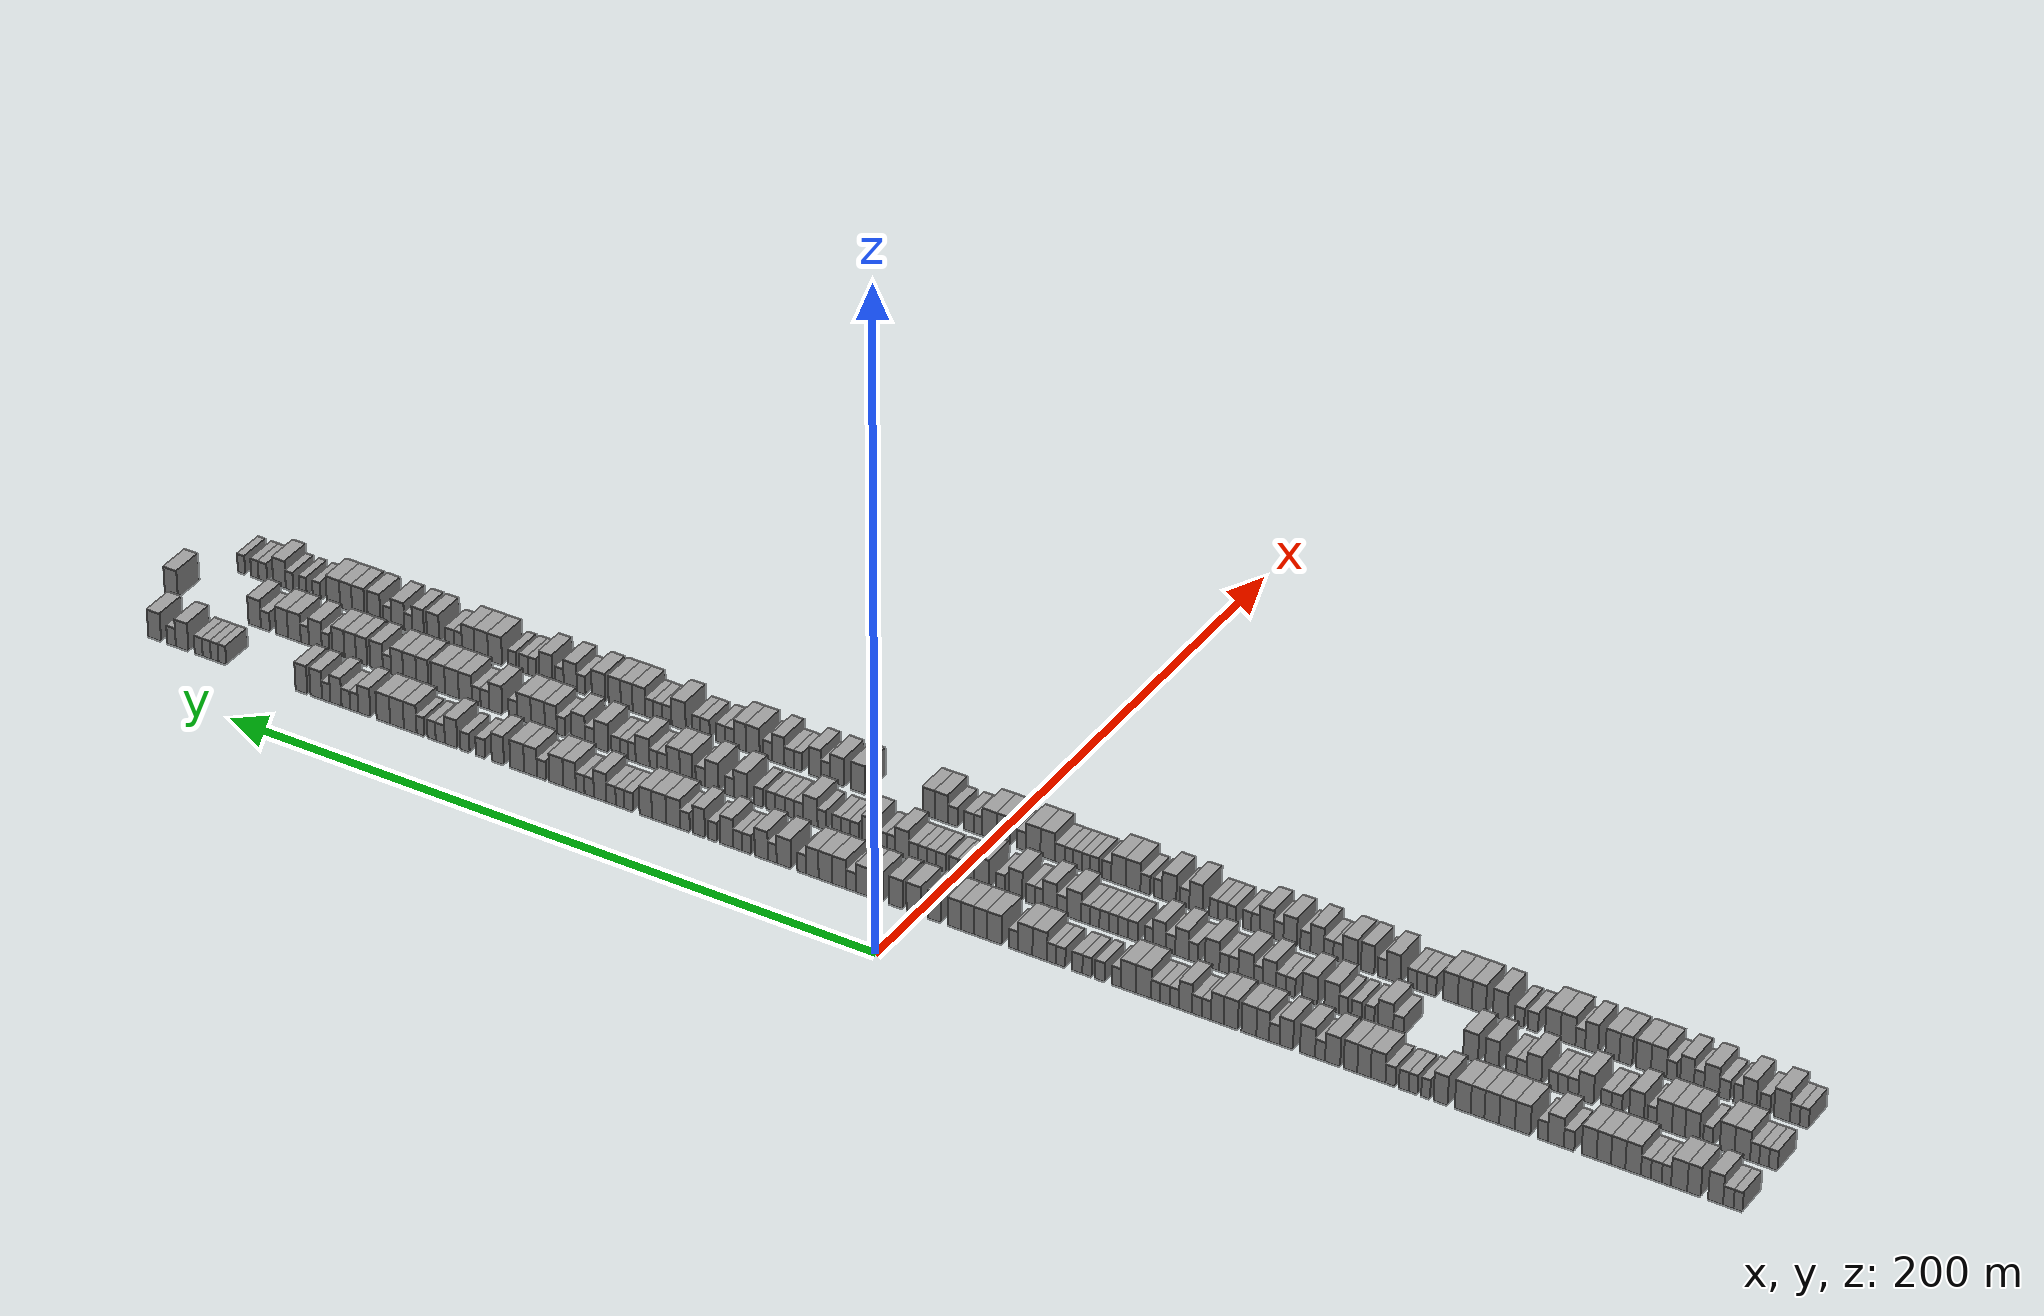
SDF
<sdf version="1.6">
 <world name="default">
  <scene>
   <sky><clouds><speed>12</speed></clouds></sky>
   <ambient>0.4 0.4 0.4 1</ambient>
   <background>0.7 0.7 0.7 1</background>
   <shadows>1</shadows>
  </scene>
  <gravity>0 0 -9.8066</gravity>
  <magnetic_field>6e-06 2.3e-05 -4.2e-05</magnetic_field>
  <physics default="0" name="default_physics" type="ode">
   <ode>
    <solver>
     <type>quick</type>
     <iters>10</iters>
     <sor>1.0</sor>
     <use_dynamic_moi_rescaling>0</use_dynamic_moi_rescaling>
    </solver>
    <constraints>
     <cfm>0</cfm>
     <erp>0.2</erp>
     <contact_max_correcting_vel>100</contact_max_correcting_vel>
     <contact_surface_layer>0.001</contact_surface_layer>
    </constraints>
   </ode>
   <max_step_size>0.004</max_step_size>
   <real_time_factor>1</real_time_factor>
   <real_time_update_rate>250</real_time_update_rate>
  </physics>
  <light name="sun" type="directional">
   <pose>0 0 10 0 0 0</pose>
   <diffuse>0.8 0.8 0.8 1</diffuse>
   <specular>0.2 0.2 0.2 1</specular>
   <attenuation>
    <range>1000</range>
    <constant>0.9</constant>
    <linear>0.01</linear>
    <quadratic>0.001</quadratic>
   </attenuation>
   <direction>-0.5 0.1 -0.9</direction>
  </light>
  <model name="building_1">
   <static>1</static>
   <pose>25.0000 -233.7699 0 0.000000 0.000000 0.000000</pose>
   <link name="link">
    <pose>0 0 3.00 0 0 0</pose>
    <collision name="collision"><geometry><box><size>10.0000 2.4602 6.0000</size></box></geometry></collision>
    <visual name="visual">
     <cast_shadows>0</cast_shadows>
     <geometry><box><size>10.0000 2.4602 6.0000</size></box></geometry>
     <material>
      <script>
       <uri>model://grey_wall/materials/scripts</uri>
       <uri>model://grey_wall/materials/textures</uri>
       <name>vrc/grey_wall</name>
      </script>
     </material>
    </visual>
   </link>
  </model>
  <model name="building_2">
   <static>1</static>
   <pose>25.0000 -231.1276 0 0.000000 0.000000 0.000000</pose>
   <link name="link">
    <pose>0 0 3.00 0 0 0</pose>
    <collision name="collision"><geometry><box><size>10.0000 2.8243 6.0000</size></box></geometry></collision>
    <visual name="visual">
     <cast_shadows>0</cast_shadows>
     <geometry><box><size>10.0000 2.8243 6.0000</size></box></geometry>
     <material>
      <script>
       <uri>model://grey_wall/materials/scripts</uri>
       <uri>model://grey_wall/materials/textures</uri>
       <name>vrc/grey_wall</name>
      </script>
     </material>
    </visual>
   </link>
  </model>
  <model name="building_3">
   <static>1</static>
   <pose>25.0000 -227.6758 0 0.000000 0.000000 0.000000</pose>
   <link name="link">
    <pose>0 0 4.50 0 0 0</pose>
    <collision name="collision"><geometry><box><size>10.0000 4.0794 9.0000</size></box></geometry></collision>
    <visual name="visual">
     <cast_shadows>0</cast_shadows>
     <geometry><box><size>10.0000 4.0794 9.0000</size></box></geometry>
     <material>
      <script>
       <uri>model://grey_wall/materials/scripts</uri>
       <uri>model://grey_wall/materials/textures</uri>
       <name>vrc/grey_wall</name>
      </script>
     </material>
    </visual>
   </link>
  </model>
  <model name="building_4">
   <static>1</static>
   <pose>25.0000 -221.7807 0 0.000000 0.000000 0.000000</pose>
   <link name="link">
    <pose>0 0 4.50 0 0 0</pose>
    <collision name="collision"><geometry><box><size>10.0000 3.7108 9.0000</size></box></geometry></collision>
    <visual name="visual">
     <cast_shadows>0</cast_shadows>
     <geometry><box><size>10.0000 3.7108 9.0000</size></box></geometry>
     <material>
      <script>
       <uri>model://grey_wall/materials/scripts</uri>
       <uri>model://grey_wall/materials/textures</uri>
       <name>vrc/grey_wall</name>
      </script>
     </material>
    </visual>
   </link>
  </model>
  <model name="building_5">
   <static>1</static>
   <pose>25.0000 -217.7213 0 0.000000 0.000000 0.000000</pose>
   <link name="link">
    <pose>0 0 4.50 0 0 0</pose>
    <collision name="collision"><geometry><box><size>10.0000 4.4080 9.0000</size></box></geometry></collision>
    <visual name="visual">
     <cast_shadows>0</cast_shadows>
     <geometry><box><size>10.0000 4.4080 9.0000</size></box></geometry>
     <material>
      <script>
       <uri>model://grey_wall/materials/scripts</uri>
       <uri>model://grey_wall/materials/textures</uri>
       <name>vrc/grey_wall</name>
      </script>
     </material>
    </visual>
   </link>
  </model>
  <model name="building_6">
   <static>1</static>
   <pose>25.0000 -214.2284 0 0.000000 0.000000 0.000000</pose>
   <link name="link">
    <pose>0 0 3.00 0 0 0</pose>
    <collision name="collision"><geometry><box><size>10.0000 2.5777 6.0000</size></box></geometry></collision>
    <visual name="visual">
     <cast_shadows>0</cast_shadows>
     <geometry><box><size>10.0000 2.5777 6.0000</size></box></geometry>
     <material>
      <script>
       <uri>model://grey_wall/materials/scripts</uri>
       <uri>model://grey_wall/materials/textures</uri>
       <name>vrc/grey_wall</name>
      </script>
     </material>
    </visual>
   </link>
  </model>
  <model name="building_7">
   <static>1</static>
   <pose>25.0000 -211.4436 0 0.000000 0.000000 0.000000</pose>
   <link name="link">
    <pose>0 0 3.00 0 0 0</pose>
    <collision name="collision"><geometry><box><size>10.0000 2.9918 6.0000</size></box></geometry></collision>
    <visual name="visual">
     <cast_shadows>0</cast_shadows>
     <geometry><box><size>10.0000 2.9918 6.0000</size></box></geometry>
     <material>
      <script>
       <uri>model://grey_wall/materials/scripts</uri>
       <uri>model://grey_wall/materials/textures</uri>
       <name>vrc/grey_wall</name>
      </script>
     </material>
    </visual>
   </link>
  </model>
  <model name="building_8">
   <static>1</static>
   <pose>25.0000 -208.5960 0 0.000000 0.000000 0.000000</pose>
   <link name="link">
    <pose>0 0 3.00 0 0 0</pose>
    <collision name="collision"><geometry><box><size>10.0000 2.7034 6.0000</size></box></geometry></collision>
    <visual name="visual">
     <cast_shadows>0</cast_shadows>
     <geometry><box><size>10.0000 2.7034 6.0000</size></box></geometry>
     <material>
      <script>
       <uri>model://grey_wall/materials/scripts</uri>
       <uri>model://grey_wall/materials/textures</uri>
       <name>vrc/grey_wall</name>
      </script>
     </material>
    </visual>
   </link>
  </model>
  <model name="building_9">
   <static>1</static>
   <pose>25.0000 -205.1038 0 0.000000 0.000000 0.000000</pose>
   <link name="link">
    <pose>0 0 4.50 0 0 0</pose>
    <collision name="collision"><geometry><box><size>10.0000 4.2810 9.0000</size></box></geometry></collision>
    <visual name="visual">
     <cast_shadows>0</cast_shadows>
     <geometry><box><size>10.0000 4.2810 9.0000</size></box></geometry>
     <material>
      <script>
       <uri>model://grey_wall/materials/scripts</uri>
       <uri>model://grey_wall/materials/textures</uri>
       <name>vrc/grey_wall</name>
      </script>
     </material>
    </visual>
   </link>
  </model>
  <model name="building_10">
   <static>1</static>
   <pose>25.0000 -200.9737 0 0.000000 0.000000 0.000000</pose>
   <link name="link">
    <pose>0 0 4.50 0 0 0</pose>
    <collision name="collision"><geometry><box><size>10.0000 3.9793 9.0000</size></box></geometry></collision>
    <visual name="visual">
     <cast_shadows>0</cast_shadows>
     <geometry><box><size>10.0000 3.9793 9.0000</size></box></geometry>
     <material>
      <script>
       <uri>model://grey_wall/materials/scripts</uri>
       <uri>model://grey_wall/materials/textures</uri>
       <name>vrc/grey_wall</name>
      </script>
     </material>
    </visual>
   </link>
  </model>
  <model name="building_11">
   <static>1</static>
   <pose>25.0000 -197.0114 0 0.000000 0.000000 0.000000</pose>
   <link name="link">
    <pose>0 0 4.50 0 0 0</pose>
    <collision name="collision"><geometry><box><size>10.0000 3.9452 9.0000</size></box></geometry></collision>
    <visual name="visual">
     <cast_shadows>0</cast_shadows>
     <geometry><box><size>10.0000 3.9452 9.0000</size></box></geometry>
     <material>
      <script>
       <uri>model://grey_wall/materials/scripts</uri>
       <uri>model://grey_wall/materials/textures</uri>
       <name>vrc/grey_wall</name>
      </script>
     </material>
    </visual>
   </link>
  </model>
  <model name="building_12">
   <static>1</static>
   <pose>25.0000 -192.9783 0 0.000000 0.000000 0.000000</pose>
   <link name="link">
    <pose>0 0 4.50 0 0 0</pose>
    <collision name="collision"><geometry><box><size>10.0000 4.1212 9.0000</size></box></geometry></collision>
    <visual name="visual">
     <cast_shadows>0</cast_shadows>
     <geometry><box><size>10.0000 4.1212 9.0000</size></box></geometry>
     <material>
      <script>
       <uri>model://grey_wall/materials/scripts</uri>
       <uri>model://grey_wall/materials/textures</uri>
       <name>vrc/grey_wall</name>
      </script>
     </material>
    </visual>
   </link>
  </model>
  <model name="building_13">
   <static>1</static>
   <pose>25.0000 -187.4523 0 0.000000 0.000000 0.000000</pose>
   <link name="link">
    <pose>0 0 3.00 0 0 0</pose>
    <collision name="collision"><geometry><box><size>10.0000 2.9307 6.0000</size></box></geometry></collision>
    <visual name="visual">
     <cast_shadows>0</cast_shadows>
     <geometry><box><size>10.0000 2.9307 6.0000</size></box></geometry>
     <material>
      <script>
       <uri>model://grey_wall/materials/scripts</uri>
       <uri>model://grey_wall/materials/textures</uri>
       <name>vrc/grey_wall</name>
      </script>
     </material>
    </visual>
   </link>
  </model>
  <model name="building_14">
   <static>1</static>
   <pose>25.0000 -183.7499 0 0.000000 0.000000 0.000000</pose>
   <link name="link">
    <pose>0 0 4.50 0 0 0</pose>
    <collision name="collision"><geometry><box><size>10.0000 4.4742 9.0000</size></box></geometry></collision>
    <visual name="visual">
     <cast_shadows>0</cast_shadows>
     <geometry><box><size>10.0000 4.4742 9.0000</size></box></geometry>
     <material>
      <script>
       <uri>model://grey_wall/materials/scripts</uri>
       <uri>model://grey_wall/materials/textures</uri>
       <name>vrc/grey_wall</name>
      </script>
     </material>
    </visual>
   </link>
  </model>
  <model name="building_15">
   <static>1</static>
   <pose>25.0000 -180.1247 0 0.000000 0.000000 0.000000</pose>
   <link name="link">
    <pose>0 0 3.00 0 0 0</pose>
    <collision name="collision"><geometry><box><size>10.0000 2.7761 6.0000</size></box></geometry></collision>
    <visual name="visual">
     <cast_shadows>0</cast_shadows>
     <geometry><box><size>10.0000 2.7761 6.0000</size></box></geometry>
     <material>
      <script>
       <uri>model://grey_wall/materials/scripts</uri>
       <uri>model://grey_wall/materials/textures</uri>
       <name>vrc/grey_wall</name>
      </script>
     </material>
    </visual>
   </link>
  </model>
  <model name="building_16">
   <static>1</static>
   <pose>25.0000 -174.5823 0 0.000000 0.000000 0.000000</pose>
   <link name="link">
    <pose>0 0 4.50 0 0 0</pose>
    <collision name="collision"><geometry><box><size>10.0000 4.3088 9.0000</size></box></geometry></collision>
    <visual name="visual">
     <cast_shadows>0</cast_shadows>
     <geometry><box><size>10.0000 4.3088 9.0000</size></box></geometry>
     <material>
      <script>
       <uri>model://grey_wall/materials/scripts</uri>
       <uri>model://grey_wall/materials/textures</uri>
       <name>vrc/grey_wall</name>
      </script>
     </material>
    </visual>
   </link>
  </model>
  <model name="building_17">
   <static>1</static>
   <pose>25.0000 -170.2294 0 0.000000 0.000000 0.000000</pose>
   <link name="link">
    <pose>0 0 4.50 0 0 0</pose>
    <collision name="collision"><geometry><box><size>10.0000 4.3968 9.0000</size></box></geometry></collision>
    <visual name="visual">
     <cast_shadows>0</cast_shadows>
     <geometry><box><size>10.0000 4.3968 9.0000</size></box></geometry>
     <material>
      <script>
       <uri>model://grey_wall/materials/scripts</uri>
       <uri>model://grey_wall/materials/textures</uri>
       <name>vrc/grey_wall</name>
      </script>
     </material>
    </visual>
   </link>
  </model>
  <model name="building_18">
   <static>1</static>
   <pose>25.0000 -165.9670 0 0.000000 0.000000 0.000000</pose>
   <link name="link">
    <pose>0 0 4.50 0 0 0</pose>
    <collision name="collision"><geometry><box><size>10.0000 4.1280 9.0000</size></box></geometry></collision>
    <visual name="visual">
     <cast_shadows>0</cast_shadows>
     <geometry><box><size>10.0000 4.1280 9.0000</size></box></geometry>
     <material>
      <script>
       <uri>model://grey_wall/materials/scripts</uri>
       <uri>model://grey_wall/materials/textures</uri>
       <name>vrc/grey_wall</name>
      </script>
     </material>
    </visual>
   </link>
  </model>
  <model name="building_19">
   <static>1</static>
   <pose>25.0000 -161.9690 0 0.000000 0.000000 0.000000</pose>
   <link name="link">
    <pose>0 0 4.50 0 0 0</pose>
    <collision name="collision"><geometry><box><size>10.0000 3.8680 9.0000</size></box></geometry></collision>
    <visual name="visual">
     <cast_shadows>0</cast_shadows>
     <geometry><box><size>10.0000 3.8680 9.0000</size></box></geometry>
     <material>
      <script>
       <uri>model://grey_wall/materials/scripts</uri>
       <uri>model://grey_wall/materials/textures</uri>
       <name>vrc/grey_wall</name>
      </script>
     </material>
    </visual>
   </link>
  </model>
  <model name="building_20">
   <static>1</static>
   <pose>25.0000 -157.8356 0 0.000000 0.000000 0.000000</pose>
   <link name="link">
    <pose>0 0 4.50 0 0 0</pose>
    <collision name="collision"><geometry><box><size>10.0000 4.3988 9.0000</size></box></geometry></collision>
    <visual name="visual">
     <cast_shadows>0</cast_shadows>
     <geometry><box><size>10.0000 4.3988 9.0000</size></box></geometry>
     <material>
      <script>
       <uri>model://grey_wall/materials/scripts</uri>
       <uri>model://grey_wall/materials/textures</uri>
       <name>vrc/grey_wall</name>
      </script>
     </material>
    </visual>
   </link>
  </model>
  <model name="building_21">
   <static>1</static>
   <pose>25.0000 -151.6563 0 0.000000 0.000000 0.000000</pose>
   <link name="link">
    <pose>0 0 4.50 0 0 0</pose>
    <collision name="collision"><geometry><box><size>10.0000 3.9599 9.0000</size></box></geometry></collision>
    <visual name="visual">
     <cast_shadows>0</cast_shadows>
     <geometry><box><size>10.0000 3.9599 9.0000</size></box></geometry>
     <material>
      <script>
       <uri>model://grey_wall/materials/scripts</uri>
       <uri>model://grey_wall/materials/textures</uri>
       <name>vrc/grey_wall</name>
      </script>
     </material>
    </visual>
   </link>
  </model>
  <model name="building_22">
   <static>1</static>
   <pose>25.0000 -147.4264 0 0.000000 0.000000 0.000000</pose>
   <link name="link">
    <pose>0 0 3.00 0 0 0</pose>
    <collision name="collision"><geometry><box><size>10.0000 2.5000 6.0000</size></box></geometry></collision>
    <visual name="visual">
     <cast_shadows>0</cast_shadows>
     <geometry><box><size>10.0000 2.5000 6.0000</size></box></geometry>
     <material>
      <script>
       <uri>model://grey_wall/materials/scripts</uri>
       <uri>model://grey_wall/materials/textures</uri>
       <name>vrc/grey_wall</name>
      </script>
     </material>
    </visual>
   </link>
  </model>
  <model name="building_23">
   <static>1</static>
   <pose>25.0000 -143.9104 0 0.000000 0.000000 0.000000</pose>
   <link name="link">
    <pose>0 0 3.00 0 0 0</pose>
    <collision name="collision"><geometry><box><size>10.0000 2.5320 6.0000</size></box></geometry></collision>
    <visual name="visual">
     <cast_shadows>0</cast_shadows>
     <geometry><box><size>10.0000 2.5320 6.0000</size></box></geometry>
     <material>
      <script>
       <uri>model://grey_wall/materials/scripts</uri>
       <uri>model://grey_wall/materials/textures</uri>
       <name>vrc/grey_wall</name>
      </script>
     </material>
    </visual>
   </link>
  </model>
  <model name="building_24">
   <static>1</static>
   <pose>25.0000 -141.2771 0 0.000000 0.000000 0.000000</pose>
   <link name="link">
    <pose>0 0 3.00 0 0 0</pose>
    <collision name="collision"><geometry><box><size>10.0000 2.7346 6.0000</size></box></geometry></collision>
    <visual name="visual">
     <cast_shadows>0</cast_shadows>
     <geometry><box><size>10.0000 2.7346 6.0000</size></box></geometry>
     <material>
      <script>
       <uri>model://grey_wall/materials/scripts</uri>
       <uri>model://grey_wall/materials/textures</uri>
       <name>vrc/grey_wall</name>
      </script>
     </material>
    </visual>
   </link>
  </model>
  <model name="building_25">
   <static>1</static>
   <pose>25.0000 -137.4993 0 0.000000 0.000000 0.000000</pose>
   <link name="link">
    <pose>0 0 3.00 0 0 0</pose>
    <collision name="collision"><geometry><box><size>10.0000 2.8210 6.0000</size></box></geometry></collision>
    <visual name="visual">
     <cast_shadows>0</cast_shadows>
     <geometry><box><size>10.0000 2.8210 6.0000</size></box></geometry>
     <material>
      <script>
       <uri>model://grey_wall/materials/scripts</uri>
       <uri>model://grey_wall/materials/textures</uri>
       <name>vrc/grey_wall</name>
      </script>
     </material>
    </visual>
   </link>
  </model>
  <model name="building_26">
   <static>1</static>
   <pose>25.0000 -133.9893 0 0.000000 0.000000 0.000000</pose>
   <link name="link">
    <pose>0 0 4.50 0 0 0</pose>
    <collision name="collision"><geometry><box><size>10.0000 4.1991 9.0000</size></box></geometry></collision>
    <visual name="visual">
     <cast_shadows>0</cast_shadows>
     <geometry><box><size>10.0000 4.1991 9.0000</size></box></geometry>
     <material>
      <script>
       <uri>model://grey_wall/materials/scripts</uri>
       <uri>model://grey_wall/materials/textures</uri>
       <name>vrc/grey_wall</name>
      </script>
     </material>
    </visual>
   </link>
  </model>
  <model name="building_27">
   <static>1</static>
   <pose>25.0000 -129.9966 0 0.000000 0.000000 0.000000</pose>
   <link name="link">
    <pose>0 0 4.50 0 0 0</pose>
    <collision name="collision"><geometry><box><size>10.0000 3.7862 9.0000</size></box></geometry></collision>
    <visual name="visual">
     <cast_shadows>0</cast_shadows>
     <geometry><box><size>10.0000 3.7862 9.0000</size></box></geometry>
     <material>
      <script>
       <uri>model://grey_wall/materials/scripts</uri>
       <uri>model://grey_wall/materials/textures</uri>
       <name>vrc/grey_wall</name>
      </script>
     </material>
    </visual>
   </link>
  </model>
  <model name="building_28">
   <static>1</static>
   <pose>25.0000 -126.1826 0 0.000000 0.000000 0.000000</pose>
   <link name="link">
    <pose>0 0 4.50 0 0 0</pose>
    <collision name="collision"><geometry><box><size>10.0000 3.8418 9.0000</size></box></geometry></collision>
    <visual name="visual">
     <cast_shadows>0</cast_shadows>
     <geometry><box><size>10.0000 3.8418 9.0000</size></box></geometry>
     <material>
      <script>
       <uri>model://grey_wall/materials/scripts</uri>
       <uri>model://grey_wall/materials/textures</uri>
       <name>vrc/grey_wall</name>
      </script>
     </material>
    </visual>
   </link>
  </model>
  <model name="building_29">
   <static>1</static>
   <pose>25.0000 -121.1121 0 0.000000 0.000000 0.000000</pose>
   <link name="link">
    <pose>0 0 4.50 0 0 0</pose>
    <collision name="collision"><geometry><box><size>10.0000 4.2991 9.0000</size></box></geometry></collision>
    <visual name="visual">
     <cast_shadows>0</cast_shadows>
     <geometry><box><size>10.0000 4.2991 9.0000</size></box></geometry>
     <material>
      <script>
       <uri>model://grey_wall/materials/scripts</uri>
       <uri>model://grey_wall/materials/textures</uri>
       <name>vrc/grey_wall</name>
      </script>
     </material>
    </visual>
   </link>
  </model>
  <model name="building_30">
   <static>1</static>
   <pose>25.0000 -117.5351 0 0.000000 0.000000 0.000000</pose>
   <link name="link">
    <pose>0 0 3.00 0 0 0</pose>
    <collision name="collision"><geometry><box><size>10.0000 2.8550 6.0000</size></box></geometry></collision>
    <visual name="visual">
     <cast_shadows>0</cast_shadows>
     <geometry><box><size>10.0000 2.8550 6.0000</size></box></geometry>
     <material>
      <script>
       <uri>model://grey_wall/materials/scripts</uri>
       <uri>model://grey_wall/materials/textures</uri>
       <name>vrc/grey_wall</name>
      </script>
     </material>
    </visual>
   </link>
  </model>
  <model name="building_31">
   <static>1</static>
   <pose>25.0000 -113.9588 0 0.000000 0.000000 0.000000</pose>
   <link name="link">
    <pose>0 0 4.50 0 0 0</pose>
    <collision name="collision"><geometry><box><size>10.0000 4.2975 9.0000</size></box></geometry></collision>
    <visual name="visual">
     <cast_shadows>0</cast_shadows>
     <geometry><box><size>10.0000 4.2975 9.0000</size></box></geometry>
     <material>
      <script>
       <uri>model://grey_wall/materials/scripts</uri>
       <uri>model://grey_wall/materials/textures</uri>
       <name>vrc/grey_wall</name>
      </script>
     </material>
    </visual>
   </link>
  </model>
  <model name="building_32">
   <static>1</static>
   <pose>25.0000 -107.8749 0 0.000000 0.000000 0.000000</pose>
   <link name="link">
    <pose>0 0 4.50 0 0 0</pose>
    <collision name="collision"><geometry><box><size>10.0000 3.8703 9.0000</size></box></geometry></collision>
    <visual name="visual">
     <cast_shadows>0</cast_shadows>
     <geometry><box><size>10.0000 3.8703 9.0000</size></box></geometry>
     <material>
      <script>
       <uri>model://grey_wall/materials/scripts</uri>
       <uri>model://grey_wall/materials/textures</uri>
       <name>vrc/grey_wall</name>
      </script>
     </material>
    </visual>
   </link>
  </model>
  <model name="building_33">
   <static>1</static>
   <pose>25.0000 -104.4467 0 0.000000 0.000000 0.000000</pose>
   <link name="link">
    <pose>0 0 3.00 0 0 0</pose>
    <collision name="collision"><geometry><box><size>10.0000 2.9861 6.0000</size></box></geometry></collision>
    <visual name="visual">
     <cast_shadows>0</cast_shadows>
     <geometry><box><size>10.0000 2.9861 6.0000</size></box></geometry>
     <material>
      <script>
       <uri>model://grey_wall/materials/scripts</uri>
       <uri>model://grey_wall/materials/textures</uri>
       <name>vrc/grey_wall</name>
      </script>
     </material>
    </visual>
   </link>
  </model>
  <model name="building_34">
   <static>1</static>
   <pose>25.0000 -101.1200 0 0.000000 0.000000 0.000000</pose>
   <link name="link">
    <pose>0 0 4.50 0 0 0</pose>
    <collision name="collision"><geometry><box><size>10.0000 3.6673 9.0000</size></box></geometry></collision>
    <visual name="visual">
     <cast_shadows>0</cast_shadows>
     <geometry><box><size>10.0000 3.6673 9.0000</size></box></geometry>
     <material>
      <script>
       <uri>model://grey_wall/materials/scripts</uri>
       <uri>model://grey_wall/materials/textures</uri>
       <name>vrc/grey_wall</name>
      </script>
     </material>
    </visual>
   </link>
  </model>
  <model name="building_35">
   <static>1</static>
   <pose>25.0000 -97.1471 0 0.000000 0.000000 0.000000</pose>
   <link name="link">
    <pose>0 0 4.50 0 0 0</pose>
    <collision name="collision"><geometry><box><size>10.0000 4.2785 9.0000</size></box></geometry></collision>
    <visual name="visual">
     <cast_shadows>0</cast_shadows>
     <geometry><box><size>10.0000 4.2785 9.0000</size></box></geometry>
     <material>
      <script>
       <uri>model://grey_wall/materials/scripts</uri>
       <uri>model://grey_wall/materials/textures</uri>
       <name>vrc/grey_wall</name>
      </script>
     </material>
    </visual>
   </link>
  </model>
  <model name="building_36">
   <static>1</static>
   <pose>25.0000 -91.9630 0 0.000000 0.000000 0.000000</pose>
   <link name="link">
    <pose>0 0 4.50 0 0 0</pose>
    <collision name="collision"><geometry><box><size>10.0000 4.0897 9.0000</size></box></geometry></collision>
    <visual name="visual">
     <cast_shadows>0</cast_shadows>
     <geometry><box><size>10.0000 4.0897 9.0000</size></box></geometry>
     <material>
      <script>
       <uri>model://grey_wall/materials/scripts</uri>
       <uri>model://grey_wall/materials/textures</uri>
       <name>vrc/grey_wall</name>
      </script>
     </material>
    </visual>
   </link>
  </model>
  <model name="building_37">
   <static>1</static>
   <pose>25.0000 -88.0747 0 0.000000 0.000000 0.000000</pose>
   <link name="link">
    <pose>0 0 4.50 0 0 0</pose>
    <collision name="collision"><geometry><box><size>10.0000 3.6870 9.0000</size></box></geometry></collision>
    <visual name="visual">
     <cast_shadows>0</cast_shadows>
     <geometry><box><size>10.0000 3.6870 9.0000</size></box></geometry>
     <material>
      <script>
       <uri>model://grey_wall/materials/scripts</uri>
       <uri>model://grey_wall/materials/textures</uri>
       <name>vrc/grey_wall</name>
      </script>
     </material>
    </visual>
   </link>
  </model>
  <model name="building_38">
   <static>1</static>
   <pose>25.0000 -84.8707 0 0.000000 0.000000 0.000000</pose>
   <link name="link">
    <pose>0 0 3.00 0 0 0</pose>
    <collision name="collision"><geometry><box><size>10.0000 2.7210 6.0000</size></box></geometry></collision>
    <visual name="visual">
     <cast_shadows>0</cast_shadows>
     <geometry><box><size>10.0000 2.7210 6.0000</size></box></geometry>
     <material>
      <script>
       <uri>model://grey_wall/materials/scripts</uri>
       <uri>model://grey_wall/materials/textures</uri>
       <name>vrc/grey_wall</name>
      </script>
     </material>
    </visual>
   </link>
  </model>
  <model name="building_39">
   <static>1</static>
   <pose>25.0000 -82.1337 0 0.000000 0.000000 0.000000</pose>
   <link name="link">
    <pose>0 0 3.00 0 0 0</pose>
    <collision name="collision"><geometry><box><size>10.0000 2.7530 6.0000</size></box></geometry></collision>
    <visual name="visual">
     <cast_shadows>0</cast_shadows>
     <geometry><box><size>10.0000 2.7530 6.0000</size></box></geometry>
     <material>
      <script>
       <uri>model://grey_wall/materials/scripts</uri>
       <uri>model://grey_wall/materials/textures</uri>
       <name>vrc/grey_wall</name>
      </script>
     </material>
    </visual>
   </link>
  </model>
  <model name="building_40">
   <static>1</static>
   <pose>25.0000 -78.8651 0 0.000000 0.000000 0.000000</pose>
   <link name="link">
    <pose>0 0 4.50 0 0 0</pose>
    <collision name="collision"><geometry><box><size>10.0000 3.7840 9.0000</size></box></geometry></collision>
    <visual name="visual">
     <cast_shadows>0</cast_shadows>
     <geometry><box><size>10.0000 3.7840 9.0000</size></box></geometry>
     <material>
      <script>
       <uri>model://grey_wall/materials/scripts</uri>
       <uri>model://grey_wall/materials/textures</uri>
       <name>vrc/grey_wall</name>
      </script>
     </material>
    </visual>
   </link>
  </model>
  <model name="building_41">
   <static>1</static>
   <pose>25.0000 -75.6244 0 0.000000 0.000000 0.000000</pose>
   <link name="link">
    <pose>0 0 3.00 0 0 0</pose>
    <collision name="collision"><geometry><box><size>10.0000 2.6975 6.0000</size></box></geometry></collision>
    <visual name="visual">
     <cast_shadows>0</cast_shadows>
     <geometry><box><size>10.0000 2.6975 6.0000</size></box></geometry>
     <material>
      <script>
       <uri>model://grey_wall/materials/scripts</uri>
       <uri>model://grey_wall/materials/textures</uri>
       <name>vrc/grey_wall</name>
      </script>
     </material>
    </visual>
   </link>
  </model>
  <model name="building_42">
   <static>1</static>
   <pose>25.0000 -72.8393 0 0.000000 0.000000 0.000000</pose>
   <link name="link">
    <pose>0 0 3.00 0 0 0</pose>
    <collision name="collision"><geometry><box><size>10.0000 2.8727 6.0000</size></box></geometry></collision>
    <visual name="visual">
     <cast_shadows>0</cast_shadows>
     <geometry><box><size>10.0000 2.8727 6.0000</size></box></geometry>
     <material>
      <script>
       <uri>model://grey_wall/materials/scripts</uri>
       <uri>model://grey_wall/materials/textures</uri>
       <name>vrc/grey_wall</name>
      </script>
     </material>
    </visual>
   </link>
  </model>
  <model name="building_43">
   <static>1</static>
   <pose>25.0000 -70.1490 0 0.000000 0.000000 0.000000</pose>
   <link name="link">
    <pose>0 0 3.00 0 0 0</pose>
    <collision name="collision"><geometry><box><size>10.0000 2.5079 6.0000</size></box></geometry></collision>
    <visual name="visual">
     <cast_shadows>0</cast_shadows>
     <geometry><box><size>10.0000 2.5079 6.0000</size></box></geometry>
     <material>
      <script>
       <uri>model://grey_wall/materials/scripts</uri>
       <uri>model://grey_wall/materials/textures</uri>
       <name>vrc/grey_wall</name>
      </script>
     </material>
    </visual>
   </link>
  </model>
  <model name="building_44">
   <static>1</static>
   <pose>25.0000 -66.6696 0 0.000000 0.000000 0.000000</pose>
   <link name="link">
    <pose>0 0 4.50 0 0 0</pose>
    <collision name="collision"><geometry><box><size>10.0000 4.4510 9.0000</size></box></geometry></collision>
    <visual name="visual">
     <cast_shadows>0</cast_shadows>
     <geometry><box><size>10.0000 4.4510 9.0000</size></box></geometry>
     <material>
      <script>
       <uri>model://grey_wall/materials/scripts</uri>
       <uri>model://grey_wall/materials/textures</uri>
       <name>vrc/grey_wall</name>
      </script>
     </material>
    </visual>
   </link>
  </model>
  <model name="building_45">
   <static>1</static>
   <pose>25.0000 -62.2535 0 0.000000 0.000000 0.000000</pose>
   <link name="link">
    <pose>0 0 4.50 0 0 0</pose>
    <collision name="collision"><geometry><box><size>10.0000 4.3812 9.0000</size></box></geometry></collision>
    <visual name="visual">
     <cast_shadows>0</cast_shadows>
     <geometry><box><size>10.0000 4.3812 9.0000</size></box></geometry>
     <material>
      <script>
       <uri>model://grey_wall/materials/scripts</uri>
       <uri>model://grey_wall/materials/textures</uri>
       <name>vrc/grey_wall</name>
      </script>
     </material>
    </visual>
   </link>
  </model>
  <model name="building_46">
   <static>1</static>
   <pose>25.0000 -58.7166 0 0.000000 0.000000 0.000000</pose>
   <link name="link">
    <pose>0 0 3.00 0 0 0</pose>
    <collision name="collision"><geometry><box><size>10.0000 2.6926 6.0000</size></box></geometry></collision>
    <visual name="visual">
     <cast_shadows>0</cast_shadows>
     <geometry><box><size>10.0000 2.6926 6.0000</size></box></geometry>
     <material>
      <script>
       <uri>model://grey_wall/materials/scripts</uri>
       <uri>model://grey_wall/materials/textures</uri>
       <name>vrc/grey_wall</name>
      </script>
     </material>
    </visual>
   </link>
  </model>
  <model name="building_47">
   <static>1</static>
   <pose>25.0000 -53.9644 0 0.000000 0.000000 0.000000</pose>
   <link name="link">
    <pose>0 0 3.00 0 0 0</pose>
    <collision name="collision"><geometry><box><size>10.0000 2.8117 6.0000</size></box></geometry></collision>
    <visual name="visual">
     <cast_shadows>0</cast_shadows>
     <geometry><box><size>10.0000 2.8117 6.0000</size></box></geometry>
     <material>
      <script>
       <uri>model://grey_wall/materials/scripts</uri>
       <uri>model://grey_wall/materials/textures</uri>
       <name>vrc/grey_wall</name>
      </script>
     </material>
    </visual>
   </link>
  </model>
  <model name="building_48">
   <static>1</static>
   <pose>25.0000 -50.1819 0 0.000000 0.000000 0.000000</pose>
   <link name="link">
    <pose>0 0 3.00 0 0 0</pose>
    <collision name="collision"><geometry><box><size>10.0000 2.7533 6.0000</size></box></geometry></collision>
    <visual name="visual">
     <cast_shadows>0</cast_shadows>
     <geometry><box><size>10.0000 2.7533 6.0000</size></box></geometry>
     <material>
      <script>
       <uri>model://grey_wall/materials/scripts</uri>
       <uri>model://grey_wall/materials/textures</uri>
       <name>vrc/grey_wall</name>
      </script>
     </material>
    </visual>
   </link>
  </model>
  <model name="building_49">
   <static>1</static>
   <pose>25.0000 -47.3075 0 0.000000 0.000000 0.000000</pose>
   <link name="link">
    <pose>0 0 3.00 0 0 0</pose>
    <collision name="collision"><geometry><box><size>10.0000 2.9956 6.0000</size></box></geometry></collision>
    <visual name="visual">
     <cast_shadows>0</cast_shadows>
     <geometry><box><size>10.0000 2.9956 6.0000</size></box></geometry>
     <material>
      <script>
       <uri>model://grey_wall/materials/scripts</uri>
       <uri>model://grey_wall/materials/textures</uri>
       <name>vrc/grey_wall</name>
      </script>
     </material>
    </visual>
   </link>
  </model>
  <model name="building_50">
   <static>1</static>
   <pose>25.0000 -42.3618 0 0.000000 0.000000 0.000000</pose>
   <link name="link">
    <pose>0 0 3.00 0 0 0</pose>
    <collision name="collision"><geometry><box><size>10.0000 2.8956 6.0000</size></box></geometry></collision>
    <visual name="visual">
     <cast_shadows>0</cast_shadows>
     <geometry><box><size>10.0000 2.8956 6.0000</size></box></geometry>
     <material>
      <script>
       <uri>model://grey_wall/materials/scripts</uri>
       <uri>model://grey_wall/materials/textures</uri>
       <name>vrc/grey_wall</name>
      </script>
     </material>
    </visual>
   </link>
  </model>
  <model name="building_51">
   <static>1</static>
   <pose>25.0000 -39.6973 0 0.000000 0.000000 0.000000</pose>
   <link name="link">
    <pose>0 0 3.00 0 0 0</pose>
    <collision name="collision"><geometry><box><size>10.0000 2.4335 6.0000</size></box></geometry></collision>
    <visual name="visual">
     <cast_shadows>0</cast_shadows>
     <geometry><box><size>10.0000 2.4335 6.0000</size></box></geometry>
     <material>
      <script>
       <uri>model://grey_wall/materials/scripts</uri>
       <uri>model://grey_wall/materials/textures</uri>
       <name>vrc/grey_wall</name>
      </script>
     </material>
    </visual>
   </link>
  </model>
  <model name="building_52">
   <static>1</static>
   <pose>25.0000 -36.2918 0 0.000000 0.000000 0.000000</pose>
   <link name="link">
    <pose>0 0 4.50 0 0 0</pose>
    <collision name="collision"><geometry><box><size>10.0000 4.3774 9.0000</size></box></geometry></collision>
    <visual name="visual">
     <cast_shadows>0</cast_shadows>
     <geometry><box><size>10.0000 4.3774 9.0000</size></box></geometry>
     <material>
      <script>
       <uri>model://grey_wall/materials/scripts</uri>
       <uri>model://grey_wall/materials/textures</uri>
       <name>vrc/grey_wall</name>
      </script>
     </material>
    </visual>
   </link>
  </model>
  <model name="building_53">
   <static>1</static>
   <pose>25.0000 -31.9116 0 0.000000 0.000000 0.000000</pose>
   <link name="link">
    <pose>0 0 4.50 0 0 0</pose>
    <collision name="collision"><geometry><box><size>10.0000 4.3831 9.0000</size></box></geometry></collision>
    <visual name="visual">
     <cast_shadows>0</cast_shadows>
     <geometry><box><size>10.0000 4.3831 9.0000</size></box></geometry>
     <material>
      <script>
       <uri>model://grey_wall/materials/scripts</uri>
       <uri>model://grey_wall/materials/textures</uri>
       <name>vrc/grey_wall</name>
      </script>
     </material>
    </visual>
   </link>
  </model>
  <model name="building_54">
   <static>1</static>
   <pose>25.0000 -28.4054 0 0.000000 0.000000 0.000000</pose>
   <link name="link">
    <pose>0 0 3.00 0 0 0</pose>
    <collision name="collision"><geometry><box><size>10.0000 2.6292 6.0000</size></box></geometry></collision>
    <visual name="visual">
     <cast_shadows>0</cast_shadows>
     <geometry><box><size>10.0000 2.6292 6.0000</size></box></geometry>
     <material>
      <script>
       <uri>model://grey_wall/materials/scripts</uri>
       <uri>model://grey_wall/materials/textures</uri>
       <name>vrc/grey_wall</name>
      </script>
     </material>
    </visual>
   </link>
  </model>
  <model name="building_55">
   <static>1</static>
   <pose>25.0000 -22.8573 0 0.000000 0.000000 0.000000</pose>
   <link name="link">
    <pose>0 0 4.50 0 0 0</pose>
    <collision name="collision"><geometry><box><size>10.0000 4.4671 9.0000</size></box></geometry></collision>
    <visual name="visual">
     <cast_shadows>0</cast_shadows>
     <geometry><box><size>10.0000 4.4671 9.0000</size></box></geometry>
     <material>
      <script>
       <uri>model://grey_wall/materials/scripts</uri>
       <uri>model://grey_wall/materials/textures</uri>
       <name>vrc/grey_wall</name>
      </script>
     </material>
    </visual>
   </link>
  </model>
  <model name="building_56">
   <static>1</static>
   <pose>25.0000 -18.6829 0 0.000000 0.000000 0.000000</pose>
   <link name="link">
    <pose>0 0 4.50 0 0 0</pose>
    <collision name="collision"><geometry><box><size>10.0000 3.8817 9.0000</size></box></geometry></collision>
    <visual name="visual">
     <cast_shadows>0</cast_shadows>
     <geometry><box><size>10.0000 3.8817 9.0000</size></box></geometry>
     <material>
      <script>
       <uri>model://grey_wall/materials/scripts</uri>
       <uri>model://grey_wall/materials/textures</uri>
       <name>vrc/grey_wall</name>
      </script>
     </material>
    </visual>
   </link>
  </model>
  <model name="building_57">
   <static>1</static>
   <pose>25.0000 -14.7864 0 0.000000 0.000000 0.000000</pose>
   <link name="link">
    <pose>0 0 4.50 0 0 0</pose>
    <collision name="collision"><geometry><box><size>10.0000 3.9114 9.0000</size></box></geometry></collision>
    <visual name="visual">
     <cast_shadows>0</cast_shadows>
     <geometry><box><size>10.0000 3.9114 9.0000</size></box></geometry>
     <material>
      <script>
       <uri>model://grey_wall/materials/scripts</uri>
       <uri>model://grey_wall/materials/textures</uri>
       <name>vrc/grey_wall</name>
      </script>
     </material>
    </visual>
   </link>
  </model>
  <model name="building_58">
   <static>1</static>
   <pose>25.0000 -10.9060 0 0.000000 0.000000 0.000000</pose>
   <link name="link">
    <pose>0 0 4.50 0 0 0</pose>
    <collision name="collision"><geometry><box><size>10.0000 3.8493 9.0000</size></box></geometry></collision>
    <visual name="visual">
     <cast_shadows>0</cast_shadows>
     <geometry><box><size>10.0000 3.8493 9.0000</size></box></geometry>
     <material>
      <script>
       <uri>model://grey_wall/materials/scripts</uri>
       <uri>model://grey_wall/materials/textures</uri>
       <name>vrc/grey_wall</name>
      </script>
     </material>
    </visual>
   </link>
  </model>
  <model name="building_59">
   <static>1</static>
   <pose>25.0000 -5.0207 0 0.000000 0.000000 0.000000</pose>
   <link name="link">
    <pose>0 0 4.50 0 0 0</pose>
    <collision name="collision"><geometry><box><size>10.0000 3.9213 9.0000</size></box></geometry></collision>
    <visual name="visual">
     <cast_shadows>0</cast_shadows>
     <geometry><box><size>10.0000 3.9213 9.0000</size></box></geometry>
     <material>
      <script>
       <uri>model://grey_wall/materials/scripts</uri>
       <uri>model://grey_wall/materials/textures</uri>
       <name>vrc/grey_wall</name>
      </script>
     </material>
    </visual>
   </link>
  </model>
  <model name="building_60">
   <static>1</static>
   <pose>25.0000 1.1351 0 0.000000 0.000000 0.000000</pose>
   <link name="link">
    <pose>0 0 4.50 0 0 0</pose>
    <collision name="collision"><geometry><box><size>10.0000 4.3903 9.0000</size></box></geometry></collision>
    <visual name="visual">
     <cast_shadows>0</cast_shadows>
     <geometry><box><size>10.0000 4.3903 9.0000</size></box></geometry>
     <material>
      <script>
       <uri>model://grey_wall/materials/scripts</uri>
       <uri>model://grey_wall/materials/textures</uri>
       <name>vrc/grey_wall</name>
      </script>
     </material>
    </visual>
   </link>
  </model>
  <model name="building_61">
   <static>1</static>
   <pose>25.0000 6.3859 0 0.000000 0.000000 0.000000</pose>
   <link name="link">
    <pose>0 0 4.50 0 0 0</pose>
    <collision name="collision"><geometry><box><size>10.0000 4.1113 9.0000</size></box></geometry></collision>
    <visual name="visual">
     <cast_shadows>0</cast_shadows>
     <geometry><box><size>10.0000 4.1113 9.0000</size></box></geometry>
     <material>
      <script>
       <uri>model://grey_wall/materials/scripts</uri>
       <uri>model://grey_wall/materials/textures</uri>
       <name>vrc/grey_wall</name>
      </script>
     </material>
    </visual>
   </link>
  </model>
  <model name="building_62">
   <static>1</static>
   <pose>25.0000 12.4364 0 0.000000 0.000000 0.000000</pose>
   <link name="link">
    <pose>0 0 4.50 0 0 0</pose>
    <collision name="collision"><geometry><box><size>10.0000 3.9896 9.0000</size></box></geometry></collision>
    <visual name="visual">
     <cast_shadows>0</cast_shadows>
     <geometry><box><size>10.0000 3.9896 9.0000</size></box></geometry>
     <material>
      <script>
       <uri>model://grey_wall/materials/scripts</uri>
       <uri>model://grey_wall/materials/textures</uri>
       <name>vrc/grey_wall</name>
      </script>
     </material>
    </visual>
   </link>
  </model>
  <model name="building_63">
   <static>1</static>
   <pose>25.0000 16.4894 0 0.000000 0.000000 0.000000</pose>
   <link name="link">
    <pose>0 0 4.50 0 0 0</pose>
    <collision name="collision"><geometry><box><size>10.0000 4.1165 9.0000</size></box></geometry></collision>
    <visual name="visual">
     <cast_shadows>0</cast_shadows>
     <geometry><box><size>10.0000 4.1165 9.0000</size></box></geometry>
     <material>
      <script>
       <uri>model://grey_wall/materials/scripts</uri>
       <uri>model://grey_wall/materials/textures</uri>
       <name>vrc/grey_wall</name>
      </script>
     </material>
    </visual>
   </link>
  </model>
  <model name="building_64">
   <static>1</static>
   <pose>25.0000 20.0148 0 0.000000 0.000000 0.000000</pose>
   <link name="link">
    <pose>0 0 3.00 0 0 0</pose>
    <collision name="collision"><geometry><box><size>10.0000 2.9342 6.0000</size></box></geometry></collision>
    <visual name="visual">
     <cast_shadows>0</cast_shadows>
     <geometry><box><size>10.0000 2.9342 6.0000</size></box></geometry>
     <material>
      <script>
       <uri>model://grey_wall/materials/scripts</uri>
       <uri>model://grey_wall/materials/textures</uri>
       <name>vrc/grey_wall</name>
      </script>
     </material>
    </visual>
   </link>
  </model>
  <model name="building_65">
   <static>1</static>
   <pose>25.0000 23.6106 0 0.000000 0.000000 0.000000</pose>
   <link name="link">
    <pose>0 0 4.50 0 0 0</pose>
    <collision name="collision"><geometry><box><size>10.0000 4.2573 9.0000</size></box></geometry></collision>
    <visual name="visual">
     <cast_shadows>0</cast_shadows>
     <geometry><box><size>10.0000 4.2573 9.0000</size></box></geometry>
     <material>
      <script>
       <uri>model://grey_wall/materials/scripts</uri>
       <uri>model://grey_wall/materials/textures</uri>
       <name>vrc/grey_wall</name>
      </script>
     </material>
    </visual>
   </link>
  </model>
  <model name="building_66">
   <static>1</static>
   <pose>25.0000 27.7748 0 0.000000 0.000000 0.000000</pose>
   <link name="link">
    <pose>0 0 4.50 0 0 0</pose>
    <collision name="collision"><geometry><box><size>10.0000 4.0713 9.0000</size></box></geometry></collision>
    <visual name="visual">
     <cast_shadows>0</cast_shadows>
     <geometry><box><size>10.0000 4.0713 9.0000</size></box></geometry>
     <material>
      <script>
       <uri>model://grey_wall/materials/scripts</uri>
       <uri>model://grey_wall/materials/textures</uri>
       <name>vrc/grey_wall</name>
      </script>
     </material>
    </visual>
   </link>
  </model>
  <model name="building_67">
   <static>1</static>
   <pose>25.0000 31.6976 0 0.000000 0.000000 0.000000</pose>
   <link name="link">
    <pose>0 0 4.50 0 0 0</pose>
    <collision name="collision"><geometry><box><size>10.0000 3.7743 9.0000</size></box></geometry></collision>
    <visual name="visual">
     <cast_shadows>0</cast_shadows>
     <geometry><box><size>10.0000 3.7743 9.0000</size></box></geometry>
     <material>
      <script>
       <uri>model://grey_wall/materials/scripts</uri>
       <uri>model://grey_wall/materials/textures</uri>
       <name>vrc/grey_wall</name>
      </script>
     </material>
    </visual>
   </link>
  </model>
  <model name="building_68">
   <static>1</static>
   <pose>25.0000 34.8935 0 0.000000 0.000000 0.000000</pose>
   <link name="link">
    <pose>0 0 3.00 0 0 0</pose>
    <collision name="collision"><geometry><box><size>10.0000 2.6174 6.0000</size></box></geometry></collision>
    <visual name="visual">
     <cast_shadows>0</cast_shadows>
     <geometry><box><size>10.0000 2.6174 6.0000</size></box></geometry>
     <material>
      <script>
       <uri>model://grey_wall/materials/scripts</uri>
       <uri>model://grey_wall/materials/textures</uri>
       <name>vrc/grey_wall</name>
      </script>
     </material>
    </visual>
   </link>
  </model>
  <model name="building_69">
   <static>1</static>
   <pose>25.0000 40.3773 0 0.000000 0.000000 0.000000</pose>
   <link name="link">
    <pose>0 0 4.50 0 0 0</pose>
    <collision name="collision"><geometry><box><size>10.0000 4.3502 9.0000</size></box></geometry></collision>
    <visual name="visual">
     <cast_shadows>0</cast_shadows>
     <geometry><box><size>10.0000 4.3502 9.0000</size></box></geometry>
     <material>
      <script>
       <uri>model://grey_wall/materials/scripts</uri>
       <uri>model://grey_wall/materials/textures</uri>
       <name>vrc/grey_wall</name>
      </script>
     </material>
    </visual>
   </link>
  </model>
  <model name="building_70">
   <static>1</static>
   <pose>25.0000 43.8943 0 0.000000 0.000000 0.000000</pose>
   <link name="link">
    <pose>0 0 3.00 0 0 0</pose>
    <collision name="collision"><geometry><box><size>10.0000 2.6839 6.0000</size></box></geometry></collision>
    <visual name="visual">
     <cast_shadows>0</cast_shadows>
     <geometry><box><size>10.0000 2.6839 6.0000</size></box></geometry>
     <material>
      <script>
       <uri>model://grey_wall/materials/scripts</uri>
       <uri>model://grey_wall/materials/textures</uri>
       <name>vrc/grey_wall</name>
      </script>
     </material>
    </visual>
   </link>
  </model>
  <model name="building_71">
   <static>1</static>
   <pose>25.0000 47.2286 0 0.000000 0.000000 0.000000</pose>
   <link name="link">
    <pose>0 0 4.50 0 0 0</pose>
    <collision name="collision"><geometry><box><size>10.0000 3.9848 9.0000</size></box></geometry></collision>
    <visual name="visual">
     <cast_shadows>0</cast_shadows>
     <geometry><box><size>10.0000 3.9848 9.0000</size></box></geometry>
     <material>
      <script>
       <uri>model://grey_wall/materials/scripts</uri>
       <uri>model://grey_wall/materials/textures</uri>
       <name>vrc/grey_wall</name>
      </script>
     </material>
    </visual>
   </link>
  </model>
  <model name="building_72">
   <static>1</static>
   <pose>25.0000 51.6965 0 0.000000 0.000000 0.000000</pose>
   <link name="link">
    <pose>0 0 3.00 0 0 0</pose>
    <collision name="collision"><geometry><box><size>10.0000 2.9509 6.0000</size></box></geometry></collision>
    <visual name="visual">
     <cast_shadows>0</cast_shadows>
     <geometry><box><size>10.0000 2.9509 6.0000</size></box></geometry>
     <material>
      <script>
       <uri>model://grey_wall/materials/scripts</uri>
       <uri>model://grey_wall/materials/textures</uri>
       <name>vrc/grey_wall</name>
      </script>
     </material>
    </visual>
   </link>
  </model>
  <model name="building_73">
   <static>1</static>
   <pose>25.0000 54.4995 0 0.000000 0.000000 0.000000</pose>
   <link name="link">
    <pose>0 0 3.00 0 0 0</pose>
    <collision name="collision"><geometry><box><size>10.0000 2.6552 6.0000</size></box></geometry></collision>
    <visual name="visual">
     <cast_shadows>0</cast_shadows>
     <geometry><box><size>10.0000 2.6552 6.0000</size></box></geometry>
     <material>
      <script>
       <uri>model://grey_wall/materials/scripts</uri>
       <uri>model://grey_wall/materials/textures</uri>
       <name>vrc/grey_wall</name>
      </script>
     </material>
    </visual>
   </link>
  </model>
  <model name="building_74">
   <static>1</static>
   <pose>25.0000 57.7731 0 0.000000 0.000000 0.000000</pose>
   <link name="link">
    <pose>0 0 4.50 0 0 0</pose>
    <collision name="collision"><geometry><box><size>10.0000 3.8920 9.0000</size></box></geometry></collision>
    <visual name="visual">
     <cast_shadows>0</cast_shadows>
     <geometry><box><size>10.0000 3.8920 9.0000</size></box></geometry>
     <material>
      <script>
       <uri>model://grey_wall/materials/scripts</uri>
       <uri>model://grey_wall/materials/textures</uri>
       <name>vrc/grey_wall</name>
      </script>
     </material>
    </visual>
   </link>
  </model>
  <model name="building_75">
   <static>1</static>
   <pose>25.0000 62.1037 0 0.000000 0.000000 0.000000</pose>
   <link name="link">
    <pose>0 0 3.00 0 0 0</pose>
    <collision name="collision"><geometry><box><size>10.0000 2.7691 6.0000</size></box></geometry></collision>
    <visual name="visual">
     <cast_shadows>0</cast_shadows>
     <geometry><box><size>10.0000 2.7691 6.0000</size></box></geometry>
     <material>
      <script>
       <uri>model://grey_wall/materials/scripts</uri>
       <uri>model://grey_wall/materials/textures</uri>
       <name>vrc/grey_wall</name>
      </script>
     </material>
    </visual>
   </link>
  </model>
  <model name="building_76">
   <static>1</static>
   <pose>25.0000 66.3098 0 0.000000 0.000000 0.000000</pose>
   <link name="link">
    <pose>0 0 4.50 0 0 0</pose>
    <collision name="collision"><geometry><box><size>10.0000 3.6431 9.0000</size></box></geometry></collision>
    <visual name="visual">
     <cast_shadows>0</cast_shadows>
     <geometry><box><size>10.0000 3.6431 9.0000</size></box></geometry>
     <material>
      <script>
       <uri>model://grey_wall/materials/scripts</uri>
       <uri>model://grey_wall/materials/textures</uri>
       <name>vrc/grey_wall</name>
      </script>
     </material>
    </visual>
   </link>
  </model>
  <model name="building_77">
   <static>1</static>
   <pose>25.0000 70.5942 0 0.000000 0.000000 0.000000</pose>
   <link name="link">
    <pose>0 0 3.00 0 0 0</pose>
    <collision name="collision"><geometry><box><size>10.0000 2.9257 6.0000</size></box></geometry></collision>
    <visual name="visual">
     <cast_shadows>0</cast_shadows>
     <geometry><box><size>10.0000 2.9257 6.0000</size></box></geometry>
     <material>
      <script>
       <uri>model://grey_wall/materials/scripts</uri>
       <uri>model://grey_wall/materials/textures</uri>
       <name>vrc/grey_wall</name>
      </script>
     </material>
    </visual>
   </link>
  </model>
  <model name="building_78">
   <static>1</static>
   <pose>25.0000 74.2457 0 0.000000 0.000000 0.000000</pose>
   <link name="link">
    <pose>0 0 4.50 0 0 0</pose>
    <collision name="collision"><geometry><box><size>10.0000 4.3774 9.0000</size></box></geometry></collision>
    <visual name="visual">
     <cast_shadows>0</cast_shadows>
     <geometry><box><size>10.0000 4.3774 9.0000</size></box></geometry>
     <material>
      <script>
       <uri>model://grey_wall/materials/scripts</uri>
       <uri>model://grey_wall/materials/textures</uri>
       <name>vrc/grey_wall</name>
      </script>
     </material>
    </visual>
   </link>
  </model>
  <model name="building_79">
   <static>1</static>
   <pose>25.0000 78.6218 0 0.000000 0.000000 0.000000</pose>
   <link name="link">
    <pose>0 0 4.50 0 0 0</pose>
    <collision name="collision"><geometry><box><size>10.0000 4.3747 9.0000</size></box></geometry></collision>
    <visual name="visual">
     <cast_shadows>0</cast_shadows>
     <geometry><box><size>10.0000 4.3747 9.0000</size></box></geometry>
     <material>
      <script>
       <uri>model://grey_wall/materials/scripts</uri>
       <uri>model://grey_wall/materials/textures</uri>
       <name>vrc/grey_wall</name>
      </script>
     </material>
    </visual>
   </link>
  </model>
  <model name="building_80">
   <static>1</static>
   <pose>25.0000 82.7082 0 0.000000 0.000000 0.000000</pose>
   <link name="link">
    <pose>0 0 4.50 0 0 0</pose>
    <collision name="collision"><geometry><box><size>10.0000 3.7982 9.0000</size></box></geometry></collision>
    <visual name="visual">
     <cast_shadows>0</cast_shadows>
     <geometry><box><size>10.0000 3.7982 9.0000</size></box></geometry>
     <material>
      <script>
       <uri>model://grey_wall/materials/scripts</uri>
       <uri>model://grey_wall/materials/textures</uri>
       <name>vrc/grey_wall</name>
      </script>
     </material>
    </visual>
   </link>
  </model>
  <model name="building_81">
   <static>1</static>
   <pose>25.0000 87.9772 0 0.000000 0.000000 0.000000</pose>
   <link name="link">
    <pose>0 0 3.00 0 0 0</pose>
    <collision name="collision"><geometry><box><size>10.0000 2.7397 6.0000</size></box></geometry></collision>
    <visual name="visual">
     <cast_shadows>0</cast_shadows>
     <geometry><box><size>10.0000 2.7397 6.0000</size></box></geometry>
     <material>
      <script>
       <uri>model://grey_wall/materials/scripts</uri>
       <uri>model://grey_wall/materials/textures</uri>
       <name>vrc/grey_wall</name>
      </script>
     </material>
    </visual>
   </link>
  </model>
  <model name="building_82">
   <static>1</static>
   <pose>25.0000 90.6677 0 0.000000 0.000000 0.000000</pose>
   <link name="link">
    <pose>0 0 3.00 0 0 0</pose>
    <collision name="collision"><geometry><box><size>10.0000 2.6412 6.0000</size></box></geometry></collision>
    <visual name="visual">
     <cast_shadows>0</cast_shadows>
     <geometry><box><size>10.0000 2.6412 6.0000</size></box></geometry>
     <material>
      <script>
       <uri>model://grey_wall/materials/scripts</uri>
       <uri>model://grey_wall/materials/textures</uri>
       <name>vrc/grey_wall</name>
      </script>
     </material>
    </visual>
   </link>
  </model>
  <model name="building_83">
   <static>1</static>
   <pose>25.0000 93.4304 0 0.000000 0.000000 0.000000</pose>
   <link name="link">
    <pose>0 0 3.00 0 0 0</pose>
    <collision name="collision"><geometry><box><size>10.0000 2.8843 6.0000</size></box></geometry></collision>
    <visual name="visual">
     <cast_shadows>0</cast_shadows>
     <geometry><box><size>10.0000 2.8843 6.0000</size></box></geometry>
     <material>
      <script>
       <uri>model://grey_wall/materials/scripts</uri>
       <uri>model://grey_wall/materials/textures</uri>
       <name>vrc/grey_wall</name>
      </script>
     </material>
    </visual>
   </link>
  </model>
  <model name="building_84">
   <static>1</static>
   <pose>25.0000 96.8308 0 0.000000 0.000000 0.000000</pose>
   <link name="link">
    <pose>0 0 4.50 0 0 0</pose>
    <collision name="collision"><geometry><box><size>10.0000 3.9165 9.0000</size></box></geometry></collision>
    <visual name="visual">
     <cast_shadows>0</cast_shadows>
     <geometry><box><size>10.0000 3.9165 9.0000</size></box></geometry>
     <material>
      <script>
       <uri>model://grey_wall/materials/scripts</uri>
       <uri>model://grey_wall/materials/textures</uri>
       <name>vrc/grey_wall</name>
      </script>
     </material>
    </visual>
   </link>
  </model>
  <model name="building_85">
   <static>1</static>
   <pose>25.0000 100.2421 0 0.000000 0.000000 0.000000</pose>
   <link name="link">
    <pose>0 0 3.00 0 0 0</pose>
    <collision name="collision"><geometry><box><size>10.0000 2.9061 6.0000</size></box></geometry></collision>
    <visual name="visual">
     <cast_shadows>0</cast_shadows>
     <geometry><box><size>10.0000 2.9061 6.0000</size></box></geometry>
     <material>
      <script>
       <uri>model://grey_wall/materials/scripts</uri>
       <uri>model://grey_wall/materials/textures</uri>
       <name>vrc/grey_wall</name>
      </script>
     </material>
    </visual>
   </link>
  </model>
  <model name="building_86">
   <static>1</static>
   <pose>25.0000 103.0500 0 0.000000 0.000000 0.000000</pose>
   <link name="link">
    <pose>0 0 3.00 0 0 0</pose>
    <collision name="collision"><geometry><box><size>10.0000 2.7096 6.0000</size></box></geometry></collision>
    <visual name="visual">
     <cast_shadows>0</cast_shadows>
     <geometry><box><size>10.0000 2.7096 6.0000</size></box></geometry>
     <material>
      <script>
       <uri>model://grey_wall/materials/scripts</uri>
       <uri>model://grey_wall/materials/textures</uri>
       <name>vrc/grey_wall</name>
      </script>
     </material>
    </visual>
   </link>
  </model>
  <model name="building_87">
   <static>1</static>
   <pose>25.0000 106.3775 0 0.000000 0.000000 0.000000</pose>
   <link name="link">
    <pose>0 0 4.50 0 0 0</pose>
    <collision name="collision"><geometry><box><size>10.0000 3.9454 9.0000</size></box></geometry></collision>
    <visual name="visual">
     <cast_shadows>0</cast_shadows>
     <geometry><box><size>10.0000 3.9454 9.0000</size></box></geometry>
     <material>
      <script>
       <uri>model://grey_wall/materials/scripts</uri>
       <uri>model://grey_wall/materials/textures</uri>
       <name>vrc/grey_wall</name>
      </script>
     </material>
    </visual>
   </link>
  </model>
  <model name="building_88">
   <static>1</static>
   <pose>25.0000 110.5230 0 0.000000 0.000000 0.000000</pose>
   <link name="link">
    <pose>0 0 4.50 0 0 0</pose>
    <collision name="collision"><geometry><box><size>10.0000 4.3455 9.0000</size></box></geometry></collision>
    <visual name="visual">
     <cast_shadows>0</cast_shadows>
     <geometry><box><size>10.0000 4.3455 9.0000</size></box></geometry>
     <material>
      <script>
       <uri>model://grey_wall/materials/scripts</uri>
       <uri>model://grey_wall/materials/textures</uri>
       <name>vrc/grey_wall</name>
      </script>
     </material>
    </visual>
   </link>
  </model>
  <model name="building_89">
   <static>1</static>
   <pose>25.0000 115.1165 0 0.000000 0.000000 0.000000</pose>
   <link name="link">
    <pose>0 0 3.00 0 0 0</pose>
    <collision name="collision"><geometry><box><size>10.0000 2.8415 6.0000</size></box></geometry></collision>
    <visual name="visual">
     <cast_shadows>0</cast_shadows>
     <geometry><box><size>10.0000 2.8415 6.0000</size></box></geometry>
     <material>
      <script>
       <uri>model://grey_wall/materials/scripts</uri>
       <uri>model://grey_wall/materials/textures</uri>
       <name>vrc/grey_wall</name>
      </script>
     </material>
    </visual>
   </link>
  </model>
  <model name="building_90">
   <static>1</static>
   <pose>25.0000 118.5710 0 0.000000 0.000000 0.000000</pose>
   <link name="link">
    <pose>0 0 4.50 0 0 0</pose>
    <collision name="collision"><geometry><box><size>10.0000 4.0676 9.0000</size></box></geometry></collision>
    <visual name="visual">
     <cast_shadows>0</cast_shadows>
     <geometry><box><size>10.0000 4.0676 9.0000</size></box></geometry>
     <material>
      <script>
       <uri>model://grey_wall/materials/scripts</uri>
       <uri>model://grey_wall/materials/textures</uri>
       <name>vrc/grey_wall</name>
      </script>
     </material>
    </visual>
   </link>
  </model>
  <model name="building_91">
   <static>1</static>
   <pose>25.0000 122.7736 0 0.000000 0.000000 0.000000</pose>
   <link name="link">
    <pose>0 0 4.50 0 0 0</pose>
    <collision name="collision"><geometry><box><size>10.0000 4.3375 9.0000</size></box></geometry></collision>
    <visual name="visual">
     <cast_shadows>0</cast_shadows>
     <geometry><box><size>10.0000 4.3375 9.0000</size></box></geometry>
     <material>
      <script>
       <uri>model://grey_wall/materials/scripts</uri>
       <uri>model://grey_wall/materials/textures</uri>
       <name>vrc/grey_wall</name>
      </script>
     </material>
    </visual>
   </link>
  </model>
  <model name="building_92">
   <static>1</static>
   <pose>25.0000 128.8661 0 0.000000 0.000000 0.000000</pose>
   <link name="link">
    <pose>0 0 4.50 0 0 0</pose>
    <collision name="collision"><geometry><box><size>10.0000 3.8475 9.0000</size></box></geometry></collision>
    <visual name="visual">
     <cast_shadows>0</cast_shadows>
     <geometry><box><size>10.0000 3.8475 9.0000</size></box></geometry>
     <material>
      <script>
       <uri>model://grey_wall/materials/scripts</uri>
       <uri>model://grey_wall/materials/textures</uri>
       <name>vrc/grey_wall</name>
      </script>
     </material>
    </visual>
   </link>
  </model>
  <model name="building_93">
   <static>1</static>
   <pose>25.0000 134.2841 0 0.000000 0.000000 0.000000</pose>
   <link name="link">
    <pose>0 0 3.00 0 0 0</pose>
    <collision name="collision"><geometry><box><size>10.0000 2.9885 6.0000</size></box></geometry></collision>
    <visual name="visual">
     <cast_shadows>0</cast_shadows>
     <geometry><box><size>10.0000 2.9885 6.0000</size></box></geometry>
     <material>
      <script>
       <uri>model://grey_wall/materials/scripts</uri>
       <uri>model://grey_wall/materials/textures</uri>
       <name>vrc/grey_wall</name>
      </script>
     </material>
    </visual>
   </link>
  </model>
  <model name="building_94">
   <static>1</static>
   <pose>25.0000 139.2223 0 0.000000 0.000000 0.000000</pose>
   <link name="link">
    <pose>0 0 3.00 0 0 0</pose>
    <collision name="collision"><geometry><box><size>10.0000 2.8879 6.0000</size></box></geometry></collision>
    <visual name="visual">
     <cast_shadows>0</cast_shadows>
     <geometry><box><size>10.0000 2.8879 6.0000</size></box></geometry>
     <material>
      <script>
       <uri>model://grey_wall/materials/scripts</uri>
       <uri>model://grey_wall/materials/textures</uri>
       <name>vrc/grey_wall</name>
      </script>
     </material>
    </visual>
   </link>
  </model>
  <model name="building_95">
   <static>1</static>
   <pose>25.0000 143.6231 0 0.000000 0.000000 0.000000</pose>
   <link name="link">
    <pose>0 0 4.50 0 0 0</pose>
    <collision name="collision"><geometry><box><size>10.0000 3.9137 9.0000</size></box></geometry></collision>
    <visual name="visual">
     <cast_shadows>0</cast_shadows>
     <geometry><box><size>10.0000 3.9137 9.0000</size></box></geometry>
     <material>
      <script>
       <uri>model://grey_wall/materials/scripts</uri>
       <uri>model://grey_wall/materials/textures</uri>
       <name>vrc/grey_wall</name>
      </script>
     </material>
    </visual>
   </link>
  </model>
  <model name="building_96">
   <static>1</static>
   <pose>25.0000 147.0490 0 0.000000 0.000000 0.000000</pose>
   <link name="link">
    <pose>0 0 3.00 0 0 0</pose>
    <collision name="collision"><geometry><box><size>10.0000 2.9381 6.0000</size></box></geometry></collision>
    <visual name="visual">
     <cast_shadows>0</cast_shadows>
     <geometry><box><size>10.0000 2.9381 6.0000</size></box></geometry>
     <material>
      <script>
       <uri>model://grey_wall/materials/scripts</uri>
       <uri>model://grey_wall/materials/textures</uri>
       <name>vrc/grey_wall</name>
      </script>
     </material>
    </visual>
   </link>
  </model>
  <model name="building_97">
   <static>1</static>
   <pose>25.0000 149.8171 0 0.000000 0.000000 0.000000</pose>
   <link name="link">
    <pose>0 0 3.00 0 0 0</pose>
    <collision name="collision"><geometry><box><size>10.0000 2.5981 6.0000</size></box></geometry></collision>
    <visual name="visual">
     <cast_shadows>0</cast_shadows>
     <geometry><box><size>10.0000 2.5981 6.0000</size></box></geometry>
     <material>
      <script>
       <uri>model://grey_wall/materials/scripts</uri>
       <uri>model://grey_wall/materials/textures</uri>
       <name>vrc/grey_wall</name>
      </script>
     </material>
    </visual>
   </link>
  </model>
  <model name="building_98">
   <static>1</static>
   <pose>25.0000 153.3529 0 0.000000 0.000000 0.000000</pose>
   <link name="link">
    <pose>0 0 3.00 0 0 0</pose>
    <collision name="collision"><geometry><box><size>10.0000 2.4735 6.0000</size></box></geometry></collision>
    <visual name="visual">
     <cast_shadows>0</cast_shadows>
     <geometry><box><size>10.0000 2.4735 6.0000</size></box></geometry>
     <material>
      <script>
       <uri>model://grey_wall/materials/scripts</uri>
       <uri>model://grey_wall/materials/textures</uri>
       <name>vrc/grey_wall</name>
      </script>
     </material>
    </visual>
   </link>
  </model>
  <model name="building_99">
   <static>1</static>
   <pose>25.0000 156.6091 0 0.000000 0.000000 0.000000</pose>
   <link name="link">
    <pose>0 0 4.50 0 0 0</pose>
    <collision name="collision"><geometry><box><size>10.0000 4.0388 9.0000</size></box></geometry></collision>
    <visual name="visual">
     <cast_shadows>0</cast_shadows>
     <geometry><box><size>10.0000 4.0388 9.0000</size></box></geometry>
     <material>
      <script>
       <uri>model://grey_wall/materials/scripts</uri>
       <uri>model://grey_wall/materials/textures</uri>
       <name>vrc/grey_wall</name>
      </script>
     </material>
    </visual>
   </link>
  </model>
  <model name="building_100">
   <static>1</static>
   <pose>25.0000 160.8219 0 0.000000 0.000000 0.000000</pose>
   <link name="link">
    <pose>0 0 4.50 0 0 0</pose>
    <collision name="collision"><geometry><box><size>10.0000 4.3868 9.0000</size></box></geometry></collision>
    <visual name="visual">
     <cast_shadows>0</cast_shadows>
     <geometry><box><size>10.0000 4.3868 9.0000</size></box></geometry>
     <material>
      <script>
       <uri>model://grey_wall/materials/scripts</uri>
       <uri>model://grey_wall/materials/textures</uri>
       <name>vrc/grey_wall</name>
      </script>
     </material>
    </visual>
   </link>
  </model>
  <model name="building_101">
   <static>1</static>
   <pose>25.0000 165.1720 0 0.000000 0.000000 0.000000</pose>
   <link name="link">
    <pose>0 0 4.50 0 0 0</pose>
    <collision name="collision"><geometry><box><size>10.0000 4.3135 9.0000</size></box></geometry></collision>
    <visual name="visual">
     <cast_shadows>0</cast_shadows>
     <geometry><box><size>10.0000 4.3135 9.0000</size></box></geometry>
     <material>
      <script>
       <uri>model://grey_wall/materials/scripts</uri>
       <uri>model://grey_wall/materials/textures</uri>
       <name>vrc/grey_wall</name>
      </script>
     </material>
    </visual>
   </link>
  </model>
  <model name="building_102">
   <static>1</static>
   <pose>25.0000 171.2678 0 0.000000 0.000000 0.000000</pose>
   <link name="link">
    <pose>0 0 4.50 0 0 0</pose>
    <collision name="collision"><geometry><box><size>10.0000 3.8781 9.0000</size></box></geometry></collision>
    <visual name="visual">
     <cast_shadows>0</cast_shadows>
     <geometry><box><size>10.0000 3.8781 9.0000</size></box></geometry>
     <material>
      <script>
       <uri>model://grey_wall/materials/scripts</uri>
       <uri>model://grey_wall/materials/textures</uri>
       <name>vrc/grey_wall</name>
      </script>
     </material>
    </visual>
   </link>
  </model>
  <model name="building_103">
   <static>1</static>
   <pose>25.0000 174.5036 0 0.000000 0.000000 0.000000</pose>
   <link name="link">
    <pose>0 0 3.00 0 0 0</pose>
    <collision name="collision"><geometry><box><size>10.0000 2.5934 6.0000</size></box></geometry></collision>
    <visual name="visual">
     <cast_shadows>0</cast_shadows>
     <geometry><box><size>10.0000 2.5934 6.0000</size></box></geometry>
     <material>
      <script>
       <uri>model://grey_wall/materials/scripts</uri>
       <uri>model://grey_wall/materials/textures</uri>
       <name>vrc/grey_wall</name>
      </script>
     </material>
    </visual>
   </link>
  </model>
  <model name="building_104">
   <static>1</static>
   <pose>25.0000 177.1857 0 0.000000 0.000000 0.000000</pose>
   <link name="link">
    <pose>0 0 3.00 0 0 0</pose>
    <collision name="collision"><geometry><box><size>10.0000 2.7708 6.0000</size></box></geometry></collision>
    <visual name="visual">
     <cast_shadows>0</cast_shadows>
     <geometry><box><size>10.0000 2.7708 6.0000</size></box></geometry>
     <material>
      <script>
       <uri>model://grey_wall/materials/scripts</uri>
       <uri>model://grey_wall/materials/textures</uri>
       <name>vrc/grey_wall</name>
      </script>
     </material>
    </visual>
   </link>
  </model>
  <model name="building_105">
   <static>1</static>
   <pose>25.0000 180.3729 0 0.000000 0.000000 0.000000</pose>
   <link name="link">
    <pose>0 0 4.50 0 0 0</pose>
    <collision name="collision"><geometry><box><size>10.0000 3.6037 9.0000</size></box></geometry></collision>
    <visual name="visual">
     <cast_shadows>0</cast_shadows>
     <geometry><box><size>10.0000 3.6037 9.0000</size></box></geometry>
     <material>
      <script>
       <uri>model://grey_wall/materials/scripts</uri>
       <uri>model://grey_wall/materials/textures</uri>
       <name>vrc/grey_wall</name>
      </script>
     </material>
    </visual>
   </link>
  </model>
  <model name="building_106">
   <static>1</static>
   <pose>25.0000 183.4995 0 0.000000 0.000000 0.000000</pose>
   <link name="link">
    <pose>0 0 3.00 0 0 0</pose>
    <collision name="collision"><geometry><box><size>10.0000 2.6494 6.0000</size></box></geometry></collision>
    <visual name="visual">
     <cast_shadows>0</cast_shadows>
     <geometry><box><size>10.0000 2.6494 6.0000</size></box></geometry>
     <material>
      <script>
       <uri>model://grey_wall/materials/scripts</uri>
       <uri>model://grey_wall/materials/textures</uri>
       <name>vrc/grey_wall</name>
      </script>
     </material>
    </visual>
   </link>
  </model>
  <model name="building_107">
   <static>1</static>
   <pose>25.0000 186.6997 0 0.000000 0.000000 0.000000</pose>
   <link name="link">
    <pose>0 0 4.50 0 0 0</pose>
    <collision name="collision"><geometry><box><size>10.0000 3.7511 9.0000</size></box></geometry></collision>
    <visual name="visual">
     <cast_shadows>0</cast_shadows>
     <geometry><box><size>10.0000 3.7511 9.0000</size></box></geometry>
     <material>
      <script>
       <uri>model://grey_wall/materials/scripts</uri>
       <uri>model://grey_wall/materials/textures</uri>
       <name>vrc/grey_wall</name>
      </script>
     </material>
    </visual>
   </link>
  </model>
  <model name="building_108">
   <static>1</static>
   <pose>25.0000 191.4714 0 0.000000 0.000000 0.000000</pose>
   <link name="link">
    <pose>0 0 4.50 0 0 0</pose>
    <collision name="collision"><geometry><box><size>10.0000 3.7923 9.0000</size></box></geometry></collision>
    <visual name="visual">
     <cast_shadows>0</cast_shadows>
     <geometry><box><size>10.0000 3.7923 9.0000</size></box></geometry>
     <material>
      <script>
       <uri>model://grey_wall/materials/scripts</uri>
       <uri>model://grey_wall/materials/textures</uri>
       <name>vrc/grey_wall</name>
      </script>
     </material>
    </visual>
   </link>
  </model>
  <model name="building_109">
   <static>1</static>
   <pose>25.0000 217.1510 0 0.000000 0.000000 0.000000</pose>
   <link name="link">
    <pose>0 0 3.00 0 0 0</pose>
    <collision name="collision"><geometry><box><size>10.0000 2.5223 6.0000</size></box></geometry></collision>
    <visual name="visual">
     <cast_shadows>0</cast_shadows>
     <geometry><box><size>10.0000 2.5223 6.0000</size></box></geometry>
     <material>
      <script>
       <uri>model://grey_wall/materials/scripts</uri>
       <uri>model://grey_wall/materials/textures</uri>
       <name>vrc/grey_wall</name>
      </script>
     </material>
    </visual>
   </link>
  </model>
  <model name="building_110">
   <static>1</static>
   <pose>25.0000 219.6556 0 0.000000 0.000000 0.000000</pose>
   <link name="link">
    <pose>0 0 3.00 0 0 0</pose>
    <collision name="collision"><geometry><box><size>10.0000 2.4870 6.0000</size></box></geometry></collision>
    <visual name="visual">
     <cast_shadows>0</cast_shadows>
     <geometry><box><size>10.0000 2.4870 6.0000</size></box></geometry>
     <material>
      <script>
       <uri>model://grey_wall/materials/scripts</uri>
       <uri>model://grey_wall/materials/textures</uri>
       <name>vrc/grey_wall</name>
      </script>
     </material>
    </visual>
   </link>
  </model>
  <model name="building_111">
   <static>1</static>
   <pose>25.0000 222.2419 0 0.000000 0.000000 0.000000</pose>
   <link name="link">
    <pose>0 0 3.00 0 0 0</pose>
    <collision name="collision"><geometry><box><size>10.0000 2.6856 6.0000</size></box></geometry></collision>
    <visual name="visual">
     <cast_shadows>0</cast_shadows>
     <geometry><box><size>10.0000 2.6856 6.0000</size></box></geometry>
     <material>
      <script>
       <uri>model://grey_wall/materials/scripts</uri>
       <uri>model://grey_wall/materials/textures</uri>
       <name>vrc/grey_wall</name>
      </script>
     </material>
    </visual>
   </link>
  </model>
  <model name="building_112">
   <static>1</static>
   <pose>25.0000 224.8906 0 0.000000 0.000000 0.000000</pose>
   <link name="link">
    <pose>0 0 3.00 0 0 0</pose>
    <collision name="collision"><geometry><box><size>10.0000 2.6119 6.0000</size></box></geometry></collision>
    <visual name="visual">
     <cast_shadows>0</cast_shadows>
     <geometry><box><size>10.0000 2.6119 6.0000</size></box></geometry>
     <material>
      <script>
       <uri>model://grey_wall/materials/scripts</uri>
       <uri>model://grey_wall/materials/textures</uri>
       <name>vrc/grey_wall</name>
      </script>
     </material>
    </visual>
   </link>
  </model>
  <model name="building_113">
   <static>1</static>
   <pose>25.0000 230.2729 0 0.000000 0.000000 0.000000</pose>
   <link name="link">
    <pose>0 0 4.50 0 0 0</pose>
    <collision name="collision"><geometry><box><size>10.0000 4.1528 9.0000</size></box></geometry></collision>
    <visual name="visual">
     <cast_shadows>0</cast_shadows>
     <geometry><box><size>10.0000 4.1528 9.0000</size></box></geometry>
     <material>
      <script>
       <uri>model://grey_wall/materials/scripts</uri>
       <uri>model://grey_wall/materials/textures</uri>
       <name>vrc/grey_wall</name>
      </script>
     </material>
    </visual>
   </link>
  </model>
  <model name="building_114">
   <static>1</static>
   <pose>25.0000 233.7670 0 0.000000 0.000000 0.000000</pose>
   <link name="link">
    <pose>0 0 3.00 0 0 0</pose>
    <collision name="collision"><geometry><box><size>10.0000 2.8354 6.0000</size></box></geometry></collision>
    <visual name="visual">
     <cast_shadows>0</cast_shadows>
     <geometry><box><size>10.0000 2.8354 6.0000</size></box></geometry>
     <material>
      <script>
       <uri>model://grey_wall/materials/scripts</uri>
       <uri>model://grey_wall/materials/textures</uri>
       <name>vrc/grey_wall</name>
      </script>
     </material>
    </visual>
   </link>
  </model>
  <model name="building_115">
   <static>1</static>
   <pose>25.0000 239.2874 0 0.000000 0.000000 0.000000</pose>
   <link name="link">
    <pose>0 0 4.50 0 0 0</pose>
    <collision name="collision"><geometry><box><size>10.0000 4.2054 9.0000</size></box></geometry></collision>
    <visual name="visual">
     <cast_shadows>0</cast_shadows>
     <geometry><box><size>10.0000 4.2054 9.0000</size></box></geometry>
     <material>
      <script>
       <uri>model://grey_wall/materials/scripts</uri>
       <uri>model://grey_wall/materials/textures</uri>
       <name>vrc/grey_wall</name>
      </script>
     </material>
    </visual>
   </link>
  </model>
  <model name="building_116">
   <static>1</static>
   <pose>44.0000 -233.7776 0 0.000000 0.000000 0.000000</pose>
   <link name="link">
    <pose>0 0 3.00 0 0 0</pose>
    <collision name="collision"><geometry><box><size>10.0000 2.4447 6.0000</size></box></geometry></collision>
    <visual name="visual">
     <cast_shadows>0</cast_shadows>
     <geometry><box><size>10.0000 2.4447 6.0000</size></box></geometry>
     <material>
      <script>
       <uri>model://grey_wall/materials/scripts</uri>
       <uri>model://grey_wall/materials/textures</uri>
       <name>vrc/grey_wall</name>
      </script>
     </material>
    </visual>
   </link>
  </model>
  <model name="building_117">
   <static>1</static>
   <pose>44.0000 -231.2473 0 0.000000 0.000000 0.000000</pose>
   <link name="link">
    <pose>0 0 3.00 0 0 0</pose>
    <collision name="collision"><geometry><box><size>10.0000 2.6159 6.0000</size></box></geometry></collision>
    <visual name="visual">
     <cast_shadows>0</cast_shadows>
     <geometry><box><size>10.0000 2.6159 6.0000</size></box></geometry>
     <material>
      <script>
       <uri>model://grey_wall/materials/scripts</uri>
       <uri>model://grey_wall/materials/textures</uri>
       <name>vrc/grey_wall</name>
      </script>
     </material>
    </visual>
   </link>
  </model>
  <model name="building_118">
   <static>1</static>
   <pose>44.0000 -228.7049 0 0.000000 0.000000 0.000000</pose>
   <link name="link">
    <pose>0 0 3.00 0 0 0</pose>
    <collision name="collision"><geometry><box><size>10.0000 2.4690 6.0000</size></box></geometry></collision>
    <visual name="visual">
     <cast_shadows>0</cast_shadows>
     <geometry><box><size>10.0000 2.4690 6.0000</size></box></geometry>
     <material>
      <script>
       <uri>model://grey_wall/materials/scripts</uri>
       <uri>model://grey_wall/materials/textures</uri>
       <name>vrc/grey_wall</name>
      </script>
     </material>
    </visual>
   </link>
  </model>
  <model name="building_119">
   <static>1</static>
   <pose>44.0000 -225.3154 0 0.000000 0.000000 0.000000</pose>
   <link name="link">
    <pose>0 0 4.50 0 0 0</pose>
    <collision name="collision"><geometry><box><size>10.0000 4.3101 9.0000</size></box></geometry></collision>
    <visual name="visual">
     <cast_shadows>0</cast_shadows>
     <geometry><box><size>10.0000 4.3101 9.0000</size></box></geometry>
     <material>
      <script>
       <uri>model://grey_wall/materials/scripts</uri>
       <uri>model://grey_wall/materials/textures</uri>
       <name>vrc/grey_wall</name>
      </script>
     </material>
    </visual>
   </link>
  </model>
  <model name="building_120">
   <static>1</static>
   <pose>44.0000 -221.1473 0 0.000000 0.000000 0.000000</pose>
   <link name="link">
    <pose>0 0 4.50 0 0 0</pose>
    <collision name="collision"><geometry><box><size>10.0000 4.0261 9.0000</size></box></geometry></collision>
    <visual name="visual">
     <cast_shadows>0</cast_shadows>
     <geometry><box><size>10.0000 4.0261 9.0000</size></box></geometry>
     <material>
      <script>
       <uri>model://grey_wall/materials/scripts</uri>
       <uri>model://grey_wall/materials/textures</uri>
       <name>vrc/grey_wall</name>
      </script>
     </material>
    </visual>
   </link>
  </model>
  <model name="building_121">
   <static>1</static>
   <pose>44.0000 -215.8307 0 0.000000 0.000000 0.000000</pose>
   <link name="link">
    <pose>0 0 3.00 0 0 0</pose>
    <collision name="collision"><geometry><box><size>10.0000 2.6070 6.0000</size></box></geometry></collision>
    <visual name="visual">
     <cast_shadows>0</cast_shadows>
     <geometry><box><size>10.0000 2.6070 6.0000</size></box></geometry>
     <material>
      <script>
       <uri>model://grey_wall/materials/scripts</uri>
       <uri>model://grey_wall/materials/textures</uri>
       <name>vrc/grey_wall</name>
      </script>
     </material>
    </visual>
   </link>
  </model>
  <model name="building_122">
   <static>1</static>
   <pose>44.0000 -211.5503 0 0.000000 0.000000 0.000000</pose>
   <link name="link">
    <pose>0 0 4.50 0 0 0</pose>
    <collision name="collision"><geometry><box><size>10.0000 3.9538 9.0000</size></box></geometry></collision>
    <visual name="visual">
     <cast_shadows>0</cast_shadows>
     <geometry><box><size>10.0000 3.9538 9.0000</size></box></geometry>
     <material>
      <script>
       <uri>model://grey_wall/materials/scripts</uri>
       <uri>model://grey_wall/materials/textures</uri>
       <name>vrc/grey_wall</name>
      </script>
     </material>
    </visual>
   </link>
  </model>
  <model name="building_123">
   <static>1</static>
   <pose>44.0000 -207.7469 0 0.000000 0.000000 0.000000</pose>
   <link name="link">
    <pose>0 0 4.50 0 0 0</pose>
    <collision name="collision"><geometry><box><size>10.0000 3.6530 9.0000</size></box></geometry></collision>
    <visual name="visual">
     <cast_shadows>0</cast_shadows>
     <geometry><box><size>10.0000 3.6530 9.0000</size></box></geometry>
     <material>
      <script>
       <uri>model://grey_wall/materials/scripts</uri>
       <uri>model://grey_wall/materials/textures</uri>
       <name>vrc/grey_wall</name>
      </script>
     </material>
    </visual>
   </link>
  </model>
  <model name="building_124">
   <static>1</static>
   <pose>44.0000 -203.7959 0 0.000000 0.000000 0.000000</pose>
   <link name="link">
    <pose>0 0 4.50 0 0 0</pose>
    <collision name="collision"><geometry><box><size>10.0000 4.2490 9.0000</size></box></geometry></collision>
    <visual name="visual">
     <cast_shadows>0</cast_shadows>
     <geometry><box><size>10.0000 4.2490 9.0000</size></box></geometry>
     <material>
      <script>
       <uri>model://grey_wall/materials/scripts</uri>
       <uri>model://grey_wall/materials/textures</uri>
       <name>vrc/grey_wall</name>
      </script>
     </material>
    </visual>
   </link>
  </model>
  <model name="building_125">
   <static>1</static>
   <pose>44.0000 -200.4332 0 0.000000 0.000000 0.000000</pose>
   <link name="link">
    <pose>0 0 3.00 0 0 0</pose>
    <collision name="collision"><geometry><box><size>10.0000 2.4765 6.0000</size></box></geometry></collision>
    <visual name="visual">
     <cast_shadows>0</cast_shadows>
     <geometry><box><size>10.0000 2.4765 6.0000</size></box></geometry>
     <material>
      <script>
       <uri>model://grey_wall/materials/scripts</uri>
       <uri>model://grey_wall/materials/textures</uri>
       <name>vrc/grey_wall</name>
      </script>
     </material>
    </visual>
   </link>
  </model>
  <model name="building_126">
   <static>1</static>
   <pose>44.0000 -196.1544 0 0.000000 0.000000 0.000000</pose>
   <link name="link">
    <pose>0 0 4.50 0 0 0</pose>
    <collision name="collision"><geometry><box><size>10.0000 4.0811 9.0000</size></box></geometry></collision>
    <visual name="visual">
     <cast_shadows>0</cast_shadows>
     <geometry><box><size>10.0000 4.0811 9.0000</size></box></geometry>
     <material>
      <script>
       <uri>model://grey_wall/materials/scripts</uri>
       <uri>model://grey_wall/materials/textures</uri>
       <name>vrc/grey_wall</name>
      </script>
     </material>
    </visual>
   </link>
  </model>
  <model name="building_127">
   <static>1</static>
   <pose>44.0000 -190.6446 0 0.000000 0.000000 0.000000</pose>
   <link name="link">
    <pose>0 0 3.00 0 0 0</pose>
    <collision name="collision"><geometry><box><size>10.0000 2.9384 6.0000</size></box></geometry></collision>
    <visual name="visual">
     <cast_shadows>0</cast_shadows>
     <geometry><box><size>10.0000 2.9384 6.0000</size></box></geometry>
     <material>
      <script>
       <uri>model://grey_wall/materials/scripts</uri>
       <uri>model://grey_wall/materials/textures</uri>
       <name>vrc/grey_wall</name>
      </script>
     </material>
    </visual>
   </link>
  </model>
  <model name="building_128">
   <static>1</static>
   <pose>44.0000 -187.7156 0 0.000000 0.000000 0.000000</pose>
   <link name="link">
    <pose>0 0 3.00 0 0 0</pose>
    <collision name="collision"><geometry><box><size>10.0000 2.9197 6.0000</size></box></geometry></collision>
    <visual name="visual">
     <cast_shadows>0</cast_shadows>
     <geometry><box><size>10.0000 2.9197 6.0000</size></box></geometry>
     <material>
      <script>
       <uri>model://grey_wall/materials/scripts</uri>
       <uri>model://grey_wall/materials/textures</uri>
       <name>vrc/grey_wall</name>
      </script>
     </material>
    </visual>
   </link>
  </model>
  <model name="building_129">
   <static>1</static>
   <pose>44.0000 -182.1388 0 0.000000 0.000000 0.000000</pose>
   <link name="link">
    <pose>0 0 4.50 0 0 0</pose>
    <collision name="collision"><geometry><box><size>10.0000 4.2337 9.0000</size></box></geometry></collision>
    <visual name="visual">
     <cast_shadows>0</cast_shadows>
     <geometry><box><size>10.0000 4.2337 9.0000</size></box></geometry>
     <material>
      <script>
       <uri>model://grey_wall/materials/scripts</uri>
       <uri>model://grey_wall/materials/textures</uri>
       <name>vrc/grey_wall</name>
      </script>
     </material>
    </visual>
   </link>
  </model>
  <model name="building_130">
   <static>1</static>
   <pose>44.0000 -178.5384 0 0.000000 0.000000 0.000000</pose>
   <link name="link">
    <pose>0 0 3.00 0 0 0</pose>
    <collision name="collision"><geometry><box><size>10.0000 2.9672 6.0000</size></box></geometry></collision>
    <visual name="visual">
     <cast_shadows>0</cast_shadows>
     <geometry><box><size>10.0000 2.9672 6.0000</size></box></geometry>
     <material>
      <script>
       <uri>model://grey_wall/materials/scripts</uri>
       <uri>model://grey_wall/materials/textures</uri>
       <name>vrc/grey_wall</name>
      </script>
     </material>
    </visual>
   </link>
  </model>
  <model name="building_131">
   <static>1</static>
   <pose>44.0000 -175.6535 0 0.000000 0.000000 0.000000</pose>
   <link name="link">
    <pose>0 0 3.00 0 0 0</pose>
    <collision name="collision"><geometry><box><size>10.0000 2.8026 6.0000</size></box></geometry></collision>
    <visual name="visual">
     <cast_shadows>0</cast_shadows>
     <geometry><box><size>10.0000 2.8026 6.0000</size></box></geometry>
     <material>
      <script>
       <uri>model://grey_wall/materials/scripts</uri>
       <uri>model://grey_wall/materials/textures</uri>
       <name>vrc/grey_wall</name>
      </script>
     </material>
    </visual>
   </link>
  </model>
  <model name="building_132">
   <static>1</static>
   <pose>44.0000 -172.9520 0 0.000000 0.000000 0.000000</pose>
   <link name="link">
    <pose>0 0 3.00 0 0 0</pose>
    <collision name="collision"><geometry><box><size>10.0000 2.6005 6.0000</size></box></geometry></collision>
    <visual name="visual">
     <cast_shadows>0</cast_shadows>
     <geometry><box><size>10.0000 2.6005 6.0000</size></box></geometry>
     <material>
      <script>
       <uri>model://grey_wall/materials/scripts</uri>
       <uri>model://grey_wall/materials/textures</uri>
       <name>vrc/grey_wall</name>
      </script>
     </material>
    </visual>
   </link>
  </model>
  <model name="building_133">
   <static>1</static>
   <pose>44.0000 -167.5758 0 0.000000 0.000000 0.000000</pose>
   <link name="link">
    <pose>0 0 4.50 0 0 0</pose>
    <collision name="collision"><geometry><box><size>10.0000 4.1518 9.0000</size></box></geometry></collision>
    <visual name="visual">
     <cast_shadows>0</cast_shadows>
     <geometry><box><size>10.0000 4.1518 9.0000</size></box></geometry>
     <material>
      <script>
       <uri>model://grey_wall/materials/scripts</uri>
       <uri>model://grey_wall/materials/textures</uri>
       <name>vrc/grey_wall</name>
      </script>
     </material>
    </visual>
   </link>
  </model>
  <model name="building_134">
   <static>1</static>
   <pose>44.0000 -164.0635 0 0.000000 0.000000 0.000000</pose>
   <link name="link">
    <pose>0 0 3.00 0 0 0</pose>
    <collision name="collision"><geometry><box><size>10.0000 2.8728 6.0000</size></box></geometry></collision>
    <visual name="visual">
     <cast_shadows>0</cast_shadows>
     <geometry><box><size>10.0000 2.8728 6.0000</size></box></geometry>
     <material>
      <script>
       <uri>model://grey_wall/materials/scripts</uri>
       <uri>model://grey_wall/materials/textures</uri>
       <name>vrc/grey_wall</name>
      </script>
     </material>
    </visual>
   </link>
  </model>
  <model name="building_135">
   <static>1</static>
   <pose>44.0000 -161.1713 0 0.000000 0.000000 0.000000</pose>
   <link name="link">
    <pose>0 0 3.00 0 0 0</pose>
    <collision name="collision"><geometry><box><size>10.0000 2.9117 6.0000</size></box></geometry></collision>
    <visual name="visual">
     <cast_shadows>0</cast_shadows>
     <geometry><box><size>10.0000 2.9117 6.0000</size></box></geometry>
     <material>
      <script>
       <uri>model://grey_wall/materials/scripts</uri>
       <uri>model://grey_wall/materials/textures</uri>
       <name>vrc/grey_wall</name>
      </script>
     </material>
    </visual>
   </link>
  </model>
  <model name="building_136">
   <static>1</static>
   <pose>44.0000 -155.7925 0 0.000000 0.000000 0.000000</pose>
   <link name="link">
    <pose>0 0 4.50 0 0 0</pose>
    <collision name="collision"><geometry><box><size>10.0000 3.8459 9.0000</size></box></geometry></collision>
    <visual name="visual">
     <cast_shadows>0</cast_shadows>
     <geometry><box><size>10.0000 3.8459 9.0000</size></box></geometry>
     <material>
      <script>
       <uri>model://grey_wall/materials/scripts</uri>
       <uri>model://grey_wall/materials/textures</uri>
       <name>vrc/grey_wall</name>
      </script>
     </material>
    </visual>
   </link>
  </model>
  <model name="building_137">
   <static>1</static>
   <pose>44.0000 -149.7716 0 0.000000 0.000000 0.000000</pose>
   <link name="link">
    <pose>0 0 4.50 0 0 0</pose>
    <collision name="collision"><geometry><box><size>10.0000 4.1959 9.0000</size></box></geometry></collision>
    <visual name="visual">
     <cast_shadows>0</cast_shadows>
     <geometry><box><size>10.0000 4.1959 9.0000</size></box></geometry>
     <material>
      <script>
       <uri>model://grey_wall/materials/scripts</uri>
       <uri>model://grey_wall/materials/textures</uri>
       <name>vrc/grey_wall</name>
      </script>
     </material>
    </visual>
   </link>
  </model>
  <model name="building_138">
   <static>1</static>
   <pose>44.0000 -129.2678 0 0.000000 0.000000 0.000000</pose>
   <link name="link">
    <pose>0 0 3.00 0 0 0</pose>
    <collision name="collision"><geometry><box><size>10.0000 2.9373 6.0000</size></box></geometry></collision>
    <visual name="visual">
     <cast_shadows>0</cast_shadows>
     <geometry><box><size>10.0000 2.9373 6.0000</size></box></geometry>
     <material>
      <script>
       <uri>model://grey_wall/materials/scripts</uri>
       <uri>model://grey_wall/materials/textures</uri>
       <name>vrc/grey_wall</name>
      </script>
     </material>
    </visual>
   </link>
  </model>
  <model name="building_139">
   <static>1</static>
   <pose>44.0000 -125.6050 0 0.000000 0.000000 0.000000</pose>
   <link name="link">
    <pose>0 0 4.50 0 0 0</pose>
    <collision name="collision"><geometry><box><size>10.0000 4.3883 9.0000</size></box></geometry></collision>
    <visual name="visual">
     <cast_shadows>0</cast_shadows>
     <geometry><box><size>10.0000 4.3883 9.0000</size></box></geometry>
     <material>
      <script>
       <uri>model://grey_wall/materials/scripts</uri>
       <uri>model://grey_wall/materials/textures</uri>
       <name>vrc/grey_wall</name>
      </script>
     </material>
    </visual>
   </link>
  </model>
  <model name="building_140">
   <static>1</static>
   <pose>44.0000 -121.0929 0 0.000000 0.000000 0.000000</pose>
   <link name="link">
    <pose>0 0 3.00 0 0 0</pose>
    <collision name="collision"><geometry><box><size>10.0000 2.6358 6.0000</size></box></geometry></collision>
    <visual name="visual">
     <cast_shadows>0</cast_shadows>
     <geometry><box><size>10.0000 2.6358 6.0000</size></box></geometry>
     <material>
      <script>
       <uri>model://grey_wall/materials/scripts</uri>
       <uri>model://grey_wall/materials/textures</uri>
       <name>vrc/grey_wall</name>
      </script>
     </material>
    </visual>
   </link>
  </model>
  <model name="building_141">
   <static>1</static>
   <pose>44.0000 -117.3289 0 0.000000 0.000000 0.000000</pose>
   <link name="link">
    <pose>0 0 3.00 0 0 0</pose>
    <collision name="collision"><geometry><box><size>10.0000 2.8922 6.0000</size></box></geometry></collision>
    <visual name="visual">
     <cast_shadows>0</cast_shadows>
     <geometry><box><size>10.0000 2.8922 6.0000</size></box></geometry>
     <material>
      <script>
       <uri>model://grey_wall/materials/scripts</uri>
       <uri>model://grey_wall/materials/textures</uri>
       <name>vrc/grey_wall</name>
      </script>
     </material>
    </visual>
   </link>
  </model>
  <model name="building_142">
   <static>1</static>
   <pose>44.0000 -113.6048 0 0.000000 0.000000 0.000000</pose>
   <link name="link">
    <pose>0 0 3.00 0 0 0</pose>
    <collision name="collision"><geometry><box><size>10.0000 2.5561 6.0000</size></box></geometry></collision>
    <visual name="visual">
     <cast_shadows>0</cast_shadows>
     <geometry><box><size>10.0000 2.5561 6.0000</size></box></geometry>
     <material>
      <script>
       <uri>model://grey_wall/materials/scripts</uri>
       <uri>model://grey_wall/materials/textures</uri>
       <name>vrc/grey_wall</name>
      </script>
     </material>
    </visual>
   </link>
  </model>
  <model name="building_143">
   <static>1</static>
   <pose>44.0000 -110.2268 0 0.000000 0.000000 0.000000</pose>
   <link name="link">
    <pose>0 0 4.50 0 0 0</pose>
    <collision name="collision"><geometry><box><size>10.0000 4.1998 9.0000</size></box></geometry></collision>
    <visual name="visual">
     <cast_shadows>0</cast_shadows>
     <geometry><box><size>10.0000 4.1998 9.0000</size></box></geometry>
     <material>
      <script>
       <uri>model://grey_wall/materials/scripts</uri>
       <uri>model://grey_wall/materials/textures</uri>
       <name>vrc/grey_wall</name>
      </script>
     </material>
    </visual>
   </link>
  </model>
  <model name="building_144">
   <static>1</static>
   <pose>44.0000 -103.9332 0 0.000000 0.000000 0.000000</pose>
   <link name="link">
    <pose>0 0 4.50 0 0 0</pose>
    <collision name="collision"><geometry><box><size>10.0000 4.3876 9.0000</size></box></geometry></collision>
    <visual name="visual">
     <cast_shadows>0</cast_shadows>
     <geometry><box><size>10.0000 4.3876 9.0000</size></box></geometry>
     <material>
      <script>
       <uri>model://grey_wall/materials/scripts</uri>
       <uri>model://grey_wall/materials/textures</uri>
       <name>vrc/grey_wall</name>
      </script>
     </material>
    </visual>
   </link>
  </model>
  <model name="building_145">
   <static>1</static>
   <pose>44.0000 -98.3554 0 0.000000 0.000000 0.000000</pose>
   <link name="link">
    <pose>0 0 3.00 0 0 0</pose>
    <collision name="collision"><geometry><box><size>10.0000 2.7679 6.0000</size></box></geometry></collision>
    <visual name="visual">
     <cast_shadows>0</cast_shadows>
     <geometry><box><size>10.0000 2.7679 6.0000</size></box></geometry>
     <material>
      <script>
       <uri>model://grey_wall/materials/scripts</uri>
       <uri>model://grey_wall/materials/textures</uri>
       <name>vrc/grey_wall</name>
      </script>
     </material>
    </visual>
   </link>
  </model>
  <model name="building_146">
   <static>1</static>
   <pose>44.0000 -95.5888 0 0.000000 0.000000 0.000000</pose>
   <link name="link">
    <pose>0 0 3.00 0 0 0</pose>
    <collision name="collision"><geometry><box><size>10.0000 2.7652 6.0000</size></box></geometry></collision>
    <visual name="visual">
     <cast_shadows>0</cast_shadows>
     <geometry><box><size>10.0000 2.7652 6.0000</size></box></geometry>
     <material>
      <script>
       <uri>model://grey_wall/materials/scripts</uri>
       <uri>model://grey_wall/materials/textures</uri>
       <name>vrc/grey_wall</name>
      </script>
     </material>
    </visual>
   </link>
  </model>
  <model name="building_147">
   <static>1</static>
   <pose>44.0000 -92.2935 0 0.000000 0.000000 0.000000</pose>
   <link name="link">
    <pose>0 0 4.50 0 0 0</pose>
    <collision name="collision"><geometry><box><size>10.0000 3.8253 9.0000</size></box></geometry></collision>
    <visual name="visual">
     <cast_shadows>0</cast_shadows>
     <geometry><box><size>10.0000 3.8253 9.0000</size></box></geometry>
     <material>
      <script>
       <uri>model://grey_wall/materials/scripts</uri>
       <uri>model://grey_wall/materials/textures</uri>
       <name>vrc/grey_wall</name>
      </script>
     </material>
    </visual>
   </link>
  </model>
  <model name="building_148">
   <static>1</static>
   <pose>44.0000 -89.0748 0 0.000000 0.000000 0.000000</pose>
   <link name="link">
    <pose>0 0 3.00 0 0 0</pose>
    <collision name="collision"><geometry><box><size>10.0000 2.6122 6.0000</size></box></geometry></collision>
    <visual name="visual">
     <cast_shadows>0</cast_shadows>
     <geometry><box><size>10.0000 2.6122 6.0000</size></box></geometry>
     <material>
      <script>
       <uri>model://grey_wall/materials/scripts</uri>
       <uri>model://grey_wall/materials/textures</uri>
       <name>vrc/grey_wall</name>
      </script>
     </material>
    </visual>
   </link>
  </model>
  <model name="building_149">
   <static>1</static>
   <pose>44.0000 -85.5253 0 0.000000 0.000000 0.000000</pose>
   <link name="link">
    <pose>0 0 4.50 0 0 0</pose>
    <collision name="collision"><geometry><box><size>10.0000 4.4867 9.0000</size></box></geometry></collision>
    <visual name="visual">
     <cast_shadows>0</cast_shadows>
     <geometry><box><size>10.0000 4.4867 9.0000</size></box></geometry>
     <material>
      <script>
       <uri>model://grey_wall/materials/scripts</uri>
       <uri>model://grey_wall/materials/textures</uri>
       <name>vrc/grey_wall</name>
      </script>
     </material>
    </visual>
   </link>
  </model>
  <model name="building_150">
   <static>1</static>
   <pose>44.0000 -81.9376 0 0.000000 0.000000 0.000000</pose>
   <link name="link">
    <pose>0 0 3.00 0 0 0</pose>
    <collision name="collision"><geometry><box><size>10.0000 2.6887 6.0000</size></box></geometry></collision>
    <visual name="visual">
     <cast_shadows>0</cast_shadows>
     <geometry><box><size>10.0000 2.6887 6.0000</size></box></geometry>
     <material>
      <script>
       <uri>model://grey_wall/materials/scripts</uri>
       <uri>model://grey_wall/materials/textures</uri>
       <name>vrc/grey_wall</name>
      </script>
     </material>
    </visual>
   </link>
  </model>
  <model name="building_151">
   <static>1</static>
   <pose>44.0000 -79.1861 0 0.000000 0.000000 0.000000</pose>
   <link name="link">
    <pose>0 0 3.00 0 0 0</pose>
    <collision name="collision"><geometry><box><size>10.0000 2.8143 6.0000</size></box></geometry></collision>
    <visual name="visual">
     <cast_shadows>0</cast_shadows>
     <geometry><box><size>10.0000 2.8143 6.0000</size></box></geometry>
     <material>
      <script>
       <uri>model://grey_wall/materials/scripts</uri>
       <uri>model://grey_wall/materials/textures</uri>
       <name>vrc/grey_wall</name>
      </script>
     </material>
    </visual>
   </link>
  </model>
  <model name="building_152">
   <static>1</static>
   <pose>44.0000 -75.6873 0 0.000000 0.000000 0.000000</pose>
   <link name="link">
    <pose>0 0 4.50 0 0 0</pose>
    <collision name="collision"><geometry><box><size>10.0000 4.1834 9.0000</size></box></geometry></collision>
    <visual name="visual">
     <cast_shadows>0</cast_shadows>
     <geometry><box><size>10.0000 4.1834 9.0000</size></box></geometry>
     <material>
      <script>
       <uri>model://grey_wall/materials/scripts</uri>
       <uri>model://grey_wall/materials/textures</uri>
       <name>vrc/grey_wall</name>
      </script>
     </material>
    </visual>
   </link>
  </model>
  <model name="building_153">
   <static>1</static>
   <pose>44.0000 -70.1980 0 0.000000 0.000000 0.000000</pose>
   <link name="link">
    <pose>0 0 3.00 0 0 0</pose>
    <collision name="collision"><geometry><box><size>10.0000 2.7953 6.0000</size></box></geometry></collision>
    <visual name="visual">
     <cast_shadows>0</cast_shadows>
     <geometry><box><size>10.0000 2.7953 6.0000</size></box></geometry>
     <material>
      <script>
       <uri>model://grey_wall/materials/scripts</uri>
       <uri>model://grey_wall/materials/textures</uri>
       <name>vrc/grey_wall</name>
      </script>
     </material>
    </visual>
   </link>
  </model>
  <model name="building_154">
   <static>1</static>
   <pose>44.0000 -66.8519 0 0.000000 0.000000 0.000000</pose>
   <link name="link">
    <pose>0 0 4.50 0 0 0</pose>
    <collision name="collision"><geometry><box><size>10.0000 3.8970 9.0000</size></box></geometry></collision>
    <visual name="visual">
     <cast_shadows>0</cast_shadows>
     <geometry><box><size>10.0000 3.8970 9.0000</size></box></geometry>
     <material>
      <script>
       <uri>model://grey_wall/materials/scripts</uri>
       <uri>model://grey_wall/materials/textures</uri>
       <name>vrc/grey_wall</name>
      </script>
     </material>
    </visual>
   </link>
  </model>
  <model name="building_155">
   <static>1</static>
   <pose>44.0000 -63.4823 0 0.000000 0.000000 0.000000</pose>
   <link name="link">
    <pose>0 0 3.00 0 0 0</pose>
    <collision name="collision"><geometry><box><size>10.0000 2.8421 6.0000</size></box></geometry></collision>
    <visual name="visual">
     <cast_shadows>0</cast_shadows>
     <geometry><box><size>10.0000 2.8421 6.0000</size></box></geometry>
     <material>
      <script>
       <uri>model://grey_wall/materials/scripts</uri>
       <uri>model://grey_wall/materials/textures</uri>
       <name>vrc/grey_wall</name>
      </script>
     </material>
    </visual>
   </link>
  </model>
  <model name="building_156">
   <static>1</static>
   <pose>44.0000 -60.1955 0 0.000000 0.000000 0.000000</pose>
   <link name="link">
    <pose>0 0 4.50 0 0 0</pose>
    <collision name="collision"><geometry><box><size>10.0000 3.7317 9.0000</size></box></geometry></collision>
    <visual name="visual">
     <cast_shadows>0</cast_shadows>
     <geometry><box><size>10.0000 3.7317 9.0000</size></box></geometry>
     <material>
      <script>
       <uri>model://grey_wall/materials/scripts</uri>
       <uri>model://grey_wall/materials/textures</uri>
       <name>vrc/grey_wall</name>
      </script>
     </material>
    </visual>
   </link>
  </model>
  <model name="building_157">
   <static>1</static>
   <pose>44.0000 -57.1191 0 0.000000 0.000000 0.000000</pose>
   <link name="link">
    <pose>0 0 3.00 0 0 0</pose>
    <collision name="collision"><geometry><box><size>10.0000 2.4211 6.0000</size></box></geometry></collision>
    <visual name="visual">
     <cast_shadows>0</cast_shadows>
     <geometry><box><size>10.0000 2.4211 6.0000</size></box></geometry>
     <material>
      <script>
       <uri>model://grey_wall/materials/scripts</uri>
       <uri>model://grey_wall/materials/textures</uri>
       <name>vrc/grey_wall</name>
      </script>
     </material>
    </visual>
   </link>
  </model>
  <model name="building_158">
   <static>1</static>
   <pose>44.0000 -52.4338 0 0.000000 0.000000 0.000000</pose>
   <link name="link">
    <pose>0 0 3.00 0 0 0</pose>
    <collision name="collision"><geometry><box><size>10.0000 2.9494 6.0000</size></box></geometry></collision>
    <visual name="visual">
     <cast_shadows>0</cast_shadows>
     <geometry><box><size>10.0000 2.9494 6.0000</size></box></geometry>
     <material>
      <script>
       <uri>model://grey_wall/materials/scripts</uri>
       <uri>model://grey_wall/materials/textures</uri>
       <name>vrc/grey_wall</name>
      </script>
     </material>
    </visual>
   </link>
  </model>
  <model name="building_159">
   <static>1</static>
   <pose>44.0000 -49.5028 0 0.000000 0.000000 0.000000</pose>
   <link name="link">
    <pose>0 0 3.00 0 0 0</pose>
    <collision name="collision"><geometry><box><size>10.0000 2.9127 6.0000</size></box></geometry></collision>
    <visual name="visual">
     <cast_shadows>0</cast_shadows>
     <geometry><box><size>10.0000 2.9127 6.0000</size></box></geometry>
     <material>
      <script>
       <uri>model://grey_wall/materials/scripts</uri>
       <uri>model://grey_wall/materials/textures</uri>
       <name>vrc/grey_wall</name>
      </script>
     </material>
    </visual>
   </link>
  </model>
  <model name="building_160">
   <static>1</static>
   <pose>44.0000 -46.7497 0 0.000000 0.000000 0.000000</pose>
   <link name="link">
    <pose>0 0 3.00 0 0 0</pose>
    <collision name="collision"><geometry><box><size>10.0000 2.5936 6.0000</size></box></geometry></collision>
    <visual name="visual">
     <cast_shadows>0</cast_shadows>
     <geometry><box><size>10.0000 2.5936 6.0000</size></box></geometry>
     <material>
      <script>
       <uri>model://grey_wall/materials/scripts</uri>
       <uri>model://grey_wall/materials/textures</uri>
       <name>vrc/grey_wall</name>
      </script>
     </material>
    </visual>
   </link>
  </model>
  <model name="building_161">
   <static>1</static>
   <pose>44.0000 -44.0382 0 0.000000 0.000000 0.000000</pose>
   <link name="link">
    <pose>0 0 3.00 0 0 0</pose>
    <collision name="collision"><geometry><box><size>10.0000 2.8294 6.0000</size></box></geometry></collision>
    <visual name="visual">
     <cast_shadows>0</cast_shadows>
     <geometry><box><size>10.0000 2.8294 6.0000</size></box></geometry>
     <material>
      <script>
       <uri>model://grey_wall/materials/scripts</uri>
       <uri>model://grey_wall/materials/textures</uri>
       <name>vrc/grey_wall</name>
      </script>
     </material>
    </visual>
   </link>
  </model>
  <model name="building_162">
   <static>1</static>
   <pose>44.0000 -41.2803 0 0.000000 0.000000 0.000000</pose>
   <link name="link">
    <pose>0 0 3.00 0 0 0</pose>
    <collision name="collision"><geometry><box><size>10.0000 2.6864 6.0000</size></box></geometry></collision>
    <visual name="visual">
     <cast_shadows>0</cast_shadows>
     <geometry><box><size>10.0000 2.6864 6.0000</size></box></geometry>
     <material>
      <script>
       <uri>model://grey_wall/materials/scripts</uri>
       <uri>model://grey_wall/materials/textures</uri>
       <name>vrc/grey_wall</name>
      </script>
     </material>
    </visual>
   </link>
  </model>
  <model name="building_163">
   <static>1</static>
   <pose>44.0000 -38.6040 0 0.000000 0.000000 0.000000</pose>
   <link name="link">
    <pose>0 0 3.00 0 0 0</pose>
    <collision name="collision"><geometry><box><size>10.0000 2.6662 6.0000</size></box></geometry></collision>
    <visual name="visual">
     <cast_shadows>0</cast_shadows>
     <geometry><box><size>10.0000 2.6662 6.0000</size></box></geometry>
     <material>
      <script>
       <uri>model://grey_wall/materials/scripts</uri>
       <uri>model://grey_wall/materials/textures</uri>
       <name>vrc/grey_wall</name>
      </script>
     </material>
    </visual>
   </link>
  </model>
  <model name="building_164">
   <static>1</static>
   <pose>44.0000 -35.1034 0 0.000000 0.000000 0.000000</pose>
   <link name="link">
    <pose>0 0 4.50 0 0 0</pose>
    <collision name="collision"><geometry><box><size>10.0000 4.3351 9.0000</size></box></geometry></collision>
    <visual name="visual">
     <cast_shadows>0</cast_shadows>
     <geometry><box><size>10.0000 4.3351 9.0000</size></box></geometry>
     <material>
      <script>
       <uri>model://grey_wall/materials/scripts</uri>
       <uri>model://grey_wall/materials/textures</uri>
       <name>vrc/grey_wall</name>
      </script>
     </material>
    </visual>
   </link>
  </model>
  <model name="building_165">
   <static>1</static>
   <pose>44.0000 -31.4518 0 0.000000 0.000000 0.000000</pose>
   <link name="link">
    <pose>0 0 3.00 0 0 0</pose>
    <collision name="collision"><geometry><box><size>10.0000 2.9680 6.0000</size></box></geometry></collision>
    <visual name="visual">
     <cast_shadows>0</cast_shadows>
     <geometry><box><size>10.0000 2.9680 6.0000</size></box></geometry>
     <material>
      <script>
       <uri>model://grey_wall/materials/scripts</uri>
       <uri>model://grey_wall/materials/textures</uri>
       <name>vrc/grey_wall</name>
      </script>
     </material>
    </visual>
   </link>
  </model>
  <model name="building_166">
   <static>1</static>
   <pose>44.0000 -27.9269 0 0.000000 0.000000 0.000000</pose>
   <link name="link">
    <pose>0 0 4.50 0 0 0</pose>
    <collision name="collision"><geometry><box><size>10.0000 4.0819 9.0000</size></box></geometry></collision>
    <visual name="visual">
     <cast_shadows>0</cast_shadows>
     <geometry><box><size>10.0000 4.0819 9.0000</size></box></geometry>
     <material>
      <script>
       <uri>model://grey_wall/materials/scripts</uri>
       <uri>model://grey_wall/materials/textures</uri>
       <name>vrc/grey_wall</name>
      </script>
     </material>
    </visual>
   </link>
  </model>
  <model name="building_167">
   <static>1</static>
   <pose>44.0000 -24.6634 0 0.000000 0.000000 0.000000</pose>
   <link name="link">
    <pose>0 0 3.00 0 0 0</pose>
    <collision name="collision"><geometry><box><size>10.0000 2.4450 6.0000</size></box></geometry></collision>
    <visual name="visual">
     <cast_shadows>0</cast_shadows>
     <geometry><box><size>10.0000 2.4450 6.0000</size></box></geometry>
     <material>
      <script>
       <uri>model://grey_wall/materials/scripts</uri>
       <uri>model://grey_wall/materials/textures</uri>
       <name>vrc/grey_wall</name>
      </script>
     </material>
    </visual>
   </link>
  </model>
  <model name="building_168">
   <static>1</static>
   <pose>44.0000 -22.1077 0 0.000000 0.000000 0.000000</pose>
   <link name="link">
    <pose>0 0 3.00 0 0 0</pose>
    <collision name="collision"><geometry><box><size>10.0000 2.6664 6.0000</size></box></geometry></collision>
    <visual name="visual">
     <cast_shadows>0</cast_shadows>
     <geometry><box><size>10.0000 2.6664 6.0000</size></box></geometry>
     <material>
      <script>
       <uri>model://grey_wall/materials/scripts</uri>
       <uri>model://grey_wall/materials/textures</uri>
       <name>vrc/grey_wall</name>
      </script>
     </material>
    </visual>
   </link>
  </model>
  <model name="building_169">
   <static>1</static>
   <pose>44.0000 -17.7062 0 0.000000 0.000000 0.000000</pose>
   <link name="link">
    <pose>0 0 4.50 0 0 0</pose>
    <collision name="collision"><geometry><box><size>10.0000 4.1365 9.0000</size></box></geometry></collision>
    <visual name="visual">
     <cast_shadows>0</cast_shadows>
     <geometry><box><size>10.0000 4.1365 9.0000</size></box></geometry>
     <material>
      <script>
       <uri>model://grey_wall/materials/scripts</uri>
       <uri>model://grey_wall/materials/textures</uri>
       <name>vrc/grey_wall</name>
      </script>
     </material>
    </visual>
   </link>
  </model>
  <model name="building_170">
   <static>1</static>
   <pose>44.0000 -13.2798 0 0.000000 0.000000 0.000000</pose>
   <link name="link">
    <pose>0 0 3.00 0 0 0</pose>
    <collision name="collision"><geometry><box><size>10.0000 2.7163 6.0000</size></box></geometry></collision>
    <visual name="visual">
     <cast_shadows>0</cast_shadows>
     <geometry><box><size>10.0000 2.7163 6.0000</size></box></geometry>
     <material>
      <script>
       <uri>model://grey_wall/materials/scripts</uri>
       <uri>model://grey_wall/materials/textures</uri>
       <name>vrc/grey_wall</name>
      </script>
     </material>
    </visual>
   </link>
  </model>
  <model name="building_171">
   <static>1</static>
   <pose>44.0000 -7.6720 0 0.000000 0.000000 0.000000</pose>
   <link name="link">
    <pose>0 0 4.50 0 0 0</pose>
    <collision name="collision"><geometry><box><size>10.0000 4.4992 9.0000</size></box></geometry></collision>
    <visual name="visual">
     <cast_shadows>0</cast_shadows>
     <geometry><box><size>10.0000 4.4992 9.0000</size></box></geometry>
     <material>
      <script>
       <uri>model://grey_wall/materials/scripts</uri>
       <uri>model://grey_wall/materials/textures</uri>
       <name>vrc/grey_wall</name>
      </script>
     </material>
    </visual>
   </link>
  </model>
  <model name="building_172">
   <static>1</static>
   <pose>44.0000 -4.2141 0 0.000000 0.000000 0.000000</pose>
   <link name="link">
    <pose>0 0 3.00 0 0 0</pose>
    <collision name="collision"><geometry><box><size>10.0000 2.4166 6.0000</size></box></geometry></collision>
    <visual name="visual">
     <cast_shadows>0</cast_shadows>
     <geometry><box><size>10.0000 2.4166 6.0000</size></box></geometry>
     <material>
      <script>
       <uri>model://grey_wall/materials/scripts</uri>
       <uri>model://grey_wall/materials/textures</uri>
       <name>vrc/grey_wall</name>
      </script>
     </material>
    </visual>
   </link>
  </model>
  <model name="building_173">
   <static>1</static>
   <pose>44.0000 -1.7904 0 0.000000 0.000000 0.000000</pose>
   <link name="link">
    <pose>0 0 3.00 0 0 0</pose>
    <collision name="collision"><geometry><box><size>10.0000 2.4309 6.0000</size></box></geometry></collision>
    <visual name="visual">
     <cast_shadows>0</cast_shadows>
     <geometry><box><size>10.0000 2.4309 6.0000</size></box></geometry>
     <material>
      <script>
       <uri>model://grey_wall/materials/scripts</uri>
       <uri>model://grey_wall/materials/textures</uri>
       <name>vrc/grey_wall</name>
      </script>
     </material>
    </visual>
   </link>
  </model>
  <model name="building_174">
   <static>1</static>
   <pose>44.0000 0.8047 0 0.000000 0.000000 0.000000</pose>
   <link name="link">
    <pose>0 0 3.00 0 0 0</pose>
    <collision name="collision"><geometry><box><size>10.0000 2.7592 6.0000</size></box></geometry></collision>
    <visual name="visual">
     <cast_shadows>0</cast_shadows>
     <geometry><box><size>10.0000 2.7592 6.0000</size></box></geometry>
     <material>
      <script>
       <uri>model://grey_wall/materials/scripts</uri>
       <uri>model://grey_wall/materials/textures</uri>
       <name>vrc/grey_wall</name>
      </script>
     </material>
    </visual>
   </link>
  </model>
  <model name="building_175">
   <static>1</static>
   <pose>44.0000 4.5854 0 0.000000 0.000000 0.000000</pose>
   <link name="link">
    <pose>0 0 3.00 0 0 0</pose>
    <collision name="collision"><geometry><box><size>10.0000 2.8022 6.0000</size></box></geometry></collision>
    <visual name="visual">
     <cast_shadows>0</cast_shadows>
     <geometry><box><size>10.0000 2.8022 6.0000</size></box></geometry>
     <material>
      <script>
       <uri>model://grey_wall/materials/scripts</uri>
       <uri>model://grey_wall/materials/textures</uri>
       <name>vrc/grey_wall</name>
      </script>
     </material>
    </visual>
   </link>
  </model>
  <model name="building_176">
   <static>1</static>
   <pose>44.0000 7.4216 0 0.000000 0.000000 0.000000</pose>
   <link name="link">
    <pose>0 0 3.00 0 0 0</pose>
    <collision name="collision"><geometry><box><size>10.0000 2.8704 6.0000</size></box></geometry></collision>
    <visual name="visual">
     <cast_shadows>0</cast_shadows>
     <geometry><box><size>10.0000 2.8704 6.0000</size></box></geometry>
     <material>
      <script>
       <uri>model://grey_wall/materials/scripts</uri>
       <uri>model://grey_wall/materials/textures</uri>
       <name>vrc/grey_wall</name>
      </script>
     </material>
    </visual>
   </link>
  </model>
  <model name="building_177">
   <static>1</static>
   <pose>44.0000 10.1140 0 0.000000 0.000000 0.000000</pose>
   <link name="link">
    <pose>0 0 3.00 0 0 0</pose>
    <collision name="collision"><geometry><box><size>10.0000 2.5143 6.0000</size></box></geometry></collision>
    <visual name="visual">
     <cast_shadows>0</cast_shadows>
     <geometry><box><size>10.0000 2.5143 6.0000</size></box></geometry>
     <material>
      <script>
       <uri>model://grey_wall/materials/scripts</uri>
       <uri>model://grey_wall/materials/textures</uri>
       <name>vrc/grey_wall</name>
      </script>
     </material>
    </visual>
   </link>
  </model>
  <model name="building_178">
   <static>1</static>
   <pose>44.0000 12.8634 0 0.000000 0.000000 0.000000</pose>
   <link name="link">
    <pose>0 0 3.00 0 0 0</pose>
    <collision name="collision"><geometry><box><size>10.0000 2.9845 6.0000</size></box></geometry></collision>
    <visual name="visual">
     <cast_shadows>0</cast_shadows>
     <geometry><box><size>10.0000 2.9845 6.0000</size></box></geometry>
     <material>
      <script>
       <uri>model://grey_wall/materials/scripts</uri>
       <uri>model://grey_wall/materials/textures</uri>
       <name>vrc/grey_wall</name>
      </script>
     </material>
    </visual>
   </link>
  </model>
  <model name="building_179">
   <static>1</static>
   <pose>44.0000 16.3853 0 0.000000 0.000000 0.000000</pose>
   <link name="link">
    <pose>0 0 4.50 0 0 0</pose>
    <collision name="collision"><geometry><box><size>10.0000 4.0593 9.0000</size></box></geometry></collision>
    <visual name="visual">
     <cast_shadows>0</cast_shadows>
     <geometry><box><size>10.0000 4.0593 9.0000</size></box></geometry>
     <material>
      <script>
       <uri>model://grey_wall/materials/scripts</uri>
       <uri>model://grey_wall/materials/textures</uri>
       <name>vrc/grey_wall</name>
      </script>
     </material>
    </visual>
   </link>
  </model>
  <model name="building_180">
   <static>1</static>
   <pose>44.0000 19.6490 0 0.000000 0.000000 0.000000</pose>
   <link name="link">
    <pose>0 0 3.00 0 0 0</pose>
    <collision name="collision"><geometry><box><size>10.0000 2.4683 6.0000</size></box></geometry></collision>
    <visual name="visual">
     <cast_shadows>0</cast_shadows>
     <geometry><box><size>10.0000 2.4683 6.0000</size></box></geometry>
     <material>
      <script>
       <uri>model://grey_wall/materials/scripts</uri>
       <uri>model://grey_wall/materials/textures</uri>
       <name>vrc/grey_wall</name>
      </script>
     </material>
    </visual>
   </link>
  </model>
  <model name="building_181">
   <static>1</static>
   <pose>44.0000 22.0967 0 0.000000 0.000000 0.000000</pose>
   <link name="link">
    <pose>0 0 3.00 0 0 0</pose>
    <collision name="collision"><geometry><box><size>10.0000 2.4271 6.0000</size></box></geometry></collision>
    <visual name="visual">
     <cast_shadows>0</cast_shadows>
     <geometry><box><size>10.0000 2.4271 6.0000</size></box></geometry>
     <material>
      <script>
       <uri>model://grey_wall/materials/scripts</uri>
       <uri>model://grey_wall/materials/textures</uri>
       <name>vrc/grey_wall</name>
      </script>
     </material>
    </visual>
   </link>
  </model>
  <model name="building_182">
   <static>1</static>
   <pose>44.0000 26.3995 0 0.000000 0.000000 0.000000</pose>
   <link name="link">
    <pose>0 0 4.50 0 0 0</pose>
    <collision name="collision"><geometry><box><size>10.0000 4.1785 9.0000</size></box></geometry></collision>
    <visual name="visual">
     <cast_shadows>0</cast_shadows>
     <geometry><box><size>10.0000 4.1785 9.0000</size></box></geometry>
     <material>
      <script>
       <uri>model://grey_wall/materials/scripts</uri>
       <uri>model://grey_wall/materials/textures</uri>
       <name>vrc/grey_wall</name>
      </script>
     </material>
    </visual>
   </link>
  </model>
  <model name="building_183">
   <static>1</static>
   <pose>44.0000 30.8239 0 0.000000 0.000000 0.000000</pose>
   <link name="link">
    <pose>0 0 3.00 0 0 0</pose>
    <collision name="collision"><geometry><box><size>10.0000 2.6702 6.0000</size></box></geometry></collision>
    <visual name="visual">
     <cast_shadows>0</cast_shadows>
     <geometry><box><size>10.0000 2.6702 6.0000</size></box></geometry>
     <material>
      <script>
       <uri>model://grey_wall/materials/scripts</uri>
       <uri>model://grey_wall/materials/textures</uri>
       <name>vrc/grey_wall</name>
      </script>
     </material>
    </visual>
   </link>
  </model>
  <model name="building_184">
   <static>1</static>
   <pose>44.0000 33.4589 0 0.000000 0.000000 0.000000</pose>
   <link name="link">
    <pose>0 0 3.00 0 0 0</pose>
    <collision name="collision"><geometry><box><size>10.0000 2.5997 6.0000</size></box></geometry></collision>
    <visual name="visual">
     <cast_shadows>0</cast_shadows>
     <geometry><box><size>10.0000 2.5997 6.0000</size></box></geometry>
     <material>
      <script>
       <uri>model://grey_wall/materials/scripts</uri>
       <uri>model://grey_wall/materials/textures</uri>
       <name>vrc/grey_wall</name>
      </script>
     </material>
    </visual>
   </link>
  </model>
  <model name="building_185">
   <static>1</static>
   <pose>44.0000 36.1044 0 0.000000 0.000000 0.000000</pose>
   <link name="link">
    <pose>0 0 3.00 0 0 0</pose>
    <collision name="collision"><geometry><box><size>10.0000 2.6914 6.0000</size></box></geometry></collision>
    <visual name="visual">
     <cast_shadows>0</cast_shadows>
     <geometry><box><size>10.0000 2.6914 6.0000</size></box></geometry>
     <material>
      <script>
       <uri>model://grey_wall/materials/scripts</uri>
       <uri>model://grey_wall/materials/textures</uri>
       <name>vrc/grey_wall</name>
      </script>
     </material>
    </visual>
   </link>
  </model>
  <model name="building_186">
   <static>1</static>
   <pose>44.0000 40.7296 0 0.000000 0.000000 0.000000</pose>
   <link name="link">
    <pose>0 0 3.00 0 0 0</pose>
    <collision name="collision"><geometry><box><size>10.0000 2.5589 6.0000</size></box></geometry></collision>
    <visual name="visual">
     <cast_shadows>0</cast_shadows>
     <geometry><box><size>10.0000 2.5589 6.0000</size></box></geometry>
     <material>
      <script>
       <uri>model://grey_wall/materials/scripts</uri>
       <uri>model://grey_wall/materials/textures</uri>
       <name>vrc/grey_wall</name>
      </script>
     </material>
    </visual>
   </link>
  </model>
  <model name="building_187">
   <static>1</static>
   <pose>44.0000 44.2156 0 0.000000 0.000000 0.000000</pose>
   <link name="link">
    <pose>0 0 4.50 0 0 0</pose>
    <collision name="collision"><geometry><box><size>10.0000 4.4131 9.0000</size></box></geometry></collision>
    <visual name="visual">
     <cast_shadows>0</cast_shadows>
     <geometry><box><size>10.0000 4.4131 9.0000</size></box></geometry>
     <material>
      <script>
       <uri>model://grey_wall/materials/scripts</uri>
       <uri>model://grey_wall/materials/textures</uri>
       <name>vrc/grey_wall</name>
      </script>
     </material>
    </visual>
   </link>
  </model>
  <model name="building_188">
   <static>1</static>
   <pose>44.0000 47.7915 0 0.000000 0.000000 0.000000</pose>
   <link name="link">
    <pose>0 0 3.00 0 0 0</pose>
    <collision name="collision"><geometry><box><size>10.0000 2.7388 6.0000</size></box></geometry></collision>
    <visual name="visual">
     <cast_shadows>0</cast_shadows>
     <geometry><box><size>10.0000 2.7388 6.0000</size></box></geometry>
     <material>
      <script>
       <uri>model://grey_wall/materials/scripts</uri>
       <uri>model://grey_wall/materials/textures</uri>
       <name>vrc/grey_wall</name>
      </script>
     </material>
    </visual>
   </link>
  </model>
  <model name="building_189">
   <static>1</static>
   <pose>44.0000 50.5681 0 0.000000 0.000000 0.000000</pose>
   <link name="link">
    <pose>0 0 3.00 0 0 0</pose>
    <collision name="collision"><geometry><box><size>10.0000 2.8144 6.0000</size></box></geometry></collision>
    <visual name="visual">
     <cast_shadows>0</cast_shadows>
     <geometry><box><size>10.0000 2.8144 6.0000</size></box></geometry>
     <material>
      <script>
       <uri>model://grey_wall/materials/scripts</uri>
       <uri>model://grey_wall/materials/textures</uri>
       <name>vrc/grey_wall</name>
      </script>
     </material>
    </visual>
   </link>
  </model>
  <model name="building_190">
   <static>1</static>
   <pose>44.0000 53.4268 0 0.000000 0.000000 0.000000</pose>
   <link name="link">
    <pose>0 0 3.00 0 0 0</pose>
    <collision name="collision"><geometry><box><size>10.0000 2.9030 6.0000</size></box></geometry></collision>
    <visual name="visual">
     <cast_shadows>0</cast_shadows>
     <geometry><box><size>10.0000 2.9030 6.0000</size></box></geometry>
     <material>
      <script>
       <uri>model://grey_wall/materials/scripts</uri>
       <uri>model://grey_wall/materials/textures</uri>
       <name>vrc/grey_wall</name>
      </script>
     </material>
    </visual>
   </link>
  </model>
  <model name="building_191">
   <static>1</static>
   <pose>44.0000 56.2660 0 0.000000 0.000000 0.000000</pose>
   <link name="link">
    <pose>0 0 3.00 0 0 0</pose>
    <collision name="collision"><geometry><box><size>10.0000 2.7755 6.0000</size></box></geometry></collision>
    <visual name="visual">
     <cast_shadows>0</cast_shadows>
     <geometry><box><size>10.0000 2.7755 6.0000</size></box></geometry>
     <material>
      <script>
       <uri>model://grey_wall/materials/scripts</uri>
       <uri>model://grey_wall/materials/textures</uri>
       <name>vrc/grey_wall</name>
      </script>
     </material>
    </visual>
   </link>
  </model>
  <model name="building_192">
   <static>1</static>
   <pose>44.0000 60.0739 0 0.000000 0.000000 0.000000</pose>
   <link name="link">
    <pose>0 0 3.00 0 0 0</pose>
    <collision name="collision"><geometry><box><size>10.0000 2.8402 6.0000</size></box></geometry></collision>
    <visual name="visual">
     <cast_shadows>0</cast_shadows>
     <geometry><box><size>10.0000 2.8402 6.0000</size></box></geometry>
     <material>
      <script>
       <uri>model://grey_wall/materials/scripts</uri>
       <uri>model://grey_wall/materials/textures</uri>
       <name>vrc/grey_wall</name>
      </script>
     </material>
    </visual>
   </link>
  </model>
  <model name="building_193">
   <static>1</static>
   <pose>44.0000 65.6037 0 0.000000 0.000000 0.000000</pose>
   <link name="link">
    <pose>0 0 4.50 0 0 0</pose>
    <collision name="collision"><geometry><box><size>10.0000 4.2195 9.0000</size></box></geometry></collision>
    <visual name="visual">
     <cast_shadows>0</cast_shadows>
     <geometry><box><size>10.0000 4.2195 9.0000</size></box></geometry>
     <material>
      <script>
       <uri>model://grey_wall/materials/scripts</uri>
       <uri>model://grey_wall/materials/textures</uri>
       <name>vrc/grey_wall</name>
      </script>
     </material>
    </visual>
   </link>
  </model>
  <model name="building_194">
   <static>1</static>
   <pose>44.0000 69.0674 0 0.000000 0.000000 0.000000</pose>
   <link name="link">
    <pose>0 0 3.00 0 0 0</pose>
    <collision name="collision"><geometry><box><size>10.0000 2.7080 6.0000</size></box></geometry></collision>
    <visual name="visual">
     <cast_shadows>0</cast_shadows>
     <geometry><box><size>10.0000 2.7080 6.0000</size></box></geometry>
     <material>
      <script>
       <uri>model://grey_wall/materials/scripts</uri>
       <uri>model://grey_wall/materials/textures</uri>
       <name>vrc/grey_wall</name>
      </script>
     </material>
    </visual>
   </link>
  </model>
  <model name="building_195">
   <static>1</static>
   <pose>44.0000 74.4796 0 0.000000 0.000000 0.000000</pose>
   <link name="link">
    <pose>0 0 4.50 0 0 0</pose>
    <collision name="collision"><geometry><box><size>10.0000 4.1163 9.0000</size></box></geometry></collision>
    <visual name="visual">
     <cast_shadows>0</cast_shadows>
     <geometry><box><size>10.0000 4.1163 9.0000</size></box></geometry>
     <material>
      <script>
       <uri>model://grey_wall/materials/scripts</uri>
       <uri>model://grey_wall/materials/textures</uri>
       <name>vrc/grey_wall</name>
      </script>
     </material>
    </visual>
   </link>
  </model>
  <model name="building_196">
   <static>1</static>
   <pose>44.0000 78.0209 0 0.000000 0.000000 0.000000</pose>
   <link name="link">
    <pose>0 0 3.00 0 0 0</pose>
    <collision name="collision"><geometry><box><size>10.0000 2.9663 6.0000</size></box></geometry></collision>
    <visual name="visual">
     <cast_shadows>0</cast_shadows>
     <geometry><box><size>10.0000 2.9663 6.0000</size></box></geometry>
     <material>
      <script>
       <uri>model://grey_wall/materials/scripts</uri>
       <uri>model://grey_wall/materials/textures</uri>
       <name>vrc/grey_wall</name>
      </script>
     </material>
    </visual>
   </link>
  </model>
  <model name="building_197">
   <static>1</static>
   <pose>44.0000 82.4602 0 0.000000 0.000000 0.000000</pose>
   <link name="link">
    <pose>0 0 4.50 0 0 0</pose>
    <collision name="collision"><geometry><box><size>10.0000 3.9125 9.0000</size></box></geometry></collision>
    <visual name="visual">
     <cast_shadows>0</cast_shadows>
     <geometry><box><size>10.0000 3.9125 9.0000</size></box></geometry>
     <material>
      <script>
       <uri>model://grey_wall/materials/scripts</uri>
       <uri>model://grey_wall/materials/textures</uri>
       <name>vrc/grey_wall</name>
      </script>
     </material>
    </visual>
   </link>
  </model>
  <model name="building_198">
   <static>1</static>
   <pose>44.0000 86.4283 0 0.000000 0.000000 0.000000</pose>
   <link name="link">
    <pose>0 0 4.50 0 0 0</pose>
    <collision name="collision"><geometry><box><size>10.0000 4.0237 9.0000</size></box></geometry></collision>
    <visual name="visual">
     <cast_shadows>0</cast_shadows>
     <geometry><box><size>10.0000 4.0237 9.0000</size></box></geometry>
     <material>
      <script>
       <uri>model://grey_wall/materials/scripts</uri>
       <uri>model://grey_wall/materials/textures</uri>
       <name>vrc/grey_wall</name>
      </script>
     </material>
    </visual>
   </link>
  </model>
  <model name="building_199">
   <static>1</static>
   <pose>44.0000 89.9081 0 0.000000 0.000000 0.000000</pose>
   <link name="link">
    <pose>0 0 3.00 0 0 0</pose>
    <collision name="collision"><geometry><box><size>10.0000 2.9359 6.0000</size></box></geometry></collision>
    <visual name="visual">
     <cast_shadows>0</cast_shadows>
     <geometry><box><size>10.0000 2.9359 6.0000</size></box></geometry>
     <material>
      <script>
       <uri>model://grey_wall/materials/scripts</uri>
       <uri>model://grey_wall/materials/textures</uri>
       <name>vrc/grey_wall</name>
      </script>
     </material>
    </visual>
   </link>
  </model>
  <model name="building_200">
   <static>1</static>
   <pose>44.0000 92.6048 0 0.000000 0.000000 0.000000</pose>
   <link name="link">
    <pose>0 0 3.00 0 0 0</pose>
    <collision name="collision"><geometry><box><size>10.0000 2.4577 6.0000</size></box></geometry></collision>
    <visual name="visual">
     <cast_shadows>0</cast_shadows>
     <geometry><box><size>10.0000 2.4577 6.0000</size></box></geometry>
     <material>
      <script>
       <uri>model://grey_wall/materials/scripts</uri>
       <uri>model://grey_wall/materials/textures</uri>
       <name>vrc/grey_wall</name>
      </script>
     </material>
    </visual>
   </link>
  </model>
  <model name="building_201">
   <static>1</static>
   <pose>44.0000 96.0098 0 0.000000 0.000000 0.000000</pose>
   <link name="link">
    <pose>0 0 4.50 0 0 0</pose>
    <collision name="collision"><geometry><box><size>10.0000 4.3522 9.0000</size></box></geometry></collision>
    <visual name="visual">
     <cast_shadows>0</cast_shadows>
     <geometry><box><size>10.0000 4.3522 9.0000</size></box></geometry>
     <material>
      <script>
       <uri>model://grey_wall/materials/scripts</uri>
       <uri>model://grey_wall/materials/textures</uri>
       <name>vrc/grey_wall</name>
      </script>
     </material>
    </visual>
   </link>
  </model>
  <model name="building_202">
   <static>1</static>
   <pose>44.0000 99.3979 0 0.000000 0.000000 0.000000</pose>
   <link name="link">
    <pose>0 0 3.00 0 0 0</pose>
    <collision name="collision"><geometry><box><size>10.0000 2.4240 6.0000</size></box></geometry></collision>
    <visual name="visual">
     <cast_shadows>0</cast_shadows>
     <geometry><box><size>10.0000 2.4240 6.0000</size></box></geometry>
     <material>
      <script>
       <uri>model://grey_wall/materials/scripts</uri>
       <uri>model://grey_wall/materials/textures</uri>
       <name>vrc/grey_wall</name>
      </script>
     </material>
    </visual>
   </link>
  </model>
  <model name="building_203">
   <static>1</static>
   <pose>44.0000 101.8478 0 0.000000 0.000000 0.000000</pose>
   <link name="link">
    <pose>0 0 3.00 0 0 0</pose>
    <collision name="collision"><geometry><box><size>10.0000 2.4759 6.0000</size></box></geometry></collision>
    <visual name="visual">
     <cast_shadows>0</cast_shadows>
     <geometry><box><size>10.0000 2.4759 6.0000</size></box></geometry>
     <material>
      <script>
       <uri>model://grey_wall/materials/scripts</uri>
       <uri>model://grey_wall/materials/textures</uri>
       <name>vrc/grey_wall</name>
      </script>
     </material>
    </visual>
   </link>
  </model>
  <model name="building_204">
   <static>1</static>
   <pose>44.0000 104.4055 0 0.000000 0.000000 0.000000</pose>
   <link name="link">
    <pose>0 0 3.00 0 0 0</pose>
    <collision name="collision"><geometry><box><size>10.0000 2.6394 6.0000</size></box></geometry></collision>
    <visual name="visual">
     <cast_shadows>0</cast_shadows>
     <geometry><box><size>10.0000 2.6394 6.0000</size></box></geometry>
     <material>
      <script>
       <uri>model://grey_wall/materials/scripts</uri>
       <uri>model://grey_wall/materials/textures</uri>
       <name>vrc/grey_wall</name>
      </script>
     </material>
    </visual>
   </link>
  </model>
  <model name="building_205">
   <static>1</static>
   <pose>44.0000 108.9088 0 0.000000 0.000000 0.000000</pose>
   <link name="link">
    <pose>0 0 4.50 0 0 0</pose>
    <collision name="collision"><geometry><box><size>10.0000 4.3673 9.0000</size></box></geometry></collision>
    <visual name="visual">
     <cast_shadows>0</cast_shadows>
     <geometry><box><size>10.0000 4.3673 9.0000</size></box></geometry>
     <material>
      <script>
       <uri>model://grey_wall/materials/scripts</uri>
       <uri>model://grey_wall/materials/textures</uri>
       <name>vrc/grey_wall</name>
      </script>
     </material>
    </visual>
   </link>
  </model>
  <model name="building_206">
   <static>1</static>
   <pose>44.0000 112.5566 0 0.000000 0.000000 0.000000</pose>
   <link name="link">
    <pose>0 0 3.00 0 0 0</pose>
    <collision name="collision"><geometry><box><size>10.0000 2.9282 6.0000</size></box></geometry></collision>
    <visual name="visual">
     <cast_shadows>0</cast_shadows>
     <geometry><box><size>10.0000 2.9282 6.0000</size></box></geometry>
     <material>
      <script>
       <uri>model://grey_wall/materials/scripts</uri>
       <uri>model://grey_wall/materials/textures</uri>
       <name>vrc/grey_wall</name>
      </script>
     </material>
    </visual>
   </link>
  </model>
  <model name="building_207">
   <static>1</static>
   <pose>44.0000 116.1484 0 0.000000 0.000000 0.000000</pose>
   <link name="link">
    <pose>0 0 4.50 0 0 0</pose>
    <collision name="collision"><geometry><box><size>10.0000 4.2554 9.0000</size></box></geometry></collision>
    <visual name="visual">
     <cast_shadows>0</cast_shadows>
     <geometry><box><size>10.0000 4.2554 9.0000</size></box></geometry>
     <material>
      <script>
       <uri>model://grey_wall/materials/scripts</uri>
       <uri>model://grey_wall/materials/textures</uri>
       <name>vrc/grey_wall</name>
      </script>
     </material>
    </visual>
   </link>
  </model>
  <model name="building_208">
   <static>1</static>
   <pose>44.0000 121.5848 0 0.000000 0.000000 0.000000</pose>
   <link name="link">
    <pose>0 0 3.00 0 0 0</pose>
    <collision name="collision"><geometry><box><size>10.0000 2.6173 6.0000</size></box></geometry></collision>
    <visual name="visual">
     <cast_shadows>0</cast_shadows>
     <geometry><box><size>10.0000 2.6173 6.0000</size></box></geometry>
     <material>
      <script>
       <uri>model://grey_wall/materials/scripts</uri>
       <uri>model://grey_wall/materials/textures</uri>
       <name>vrc/grey_wall</name>
      </script>
     </material>
    </visual>
   </link>
  </model>
  <model name="building_209">
   <static>1</static>
   <pose>44.0000 124.7767 0 0.000000 0.000000 0.000000</pose>
   <link name="link">
    <pose>0 0 4.50 0 0 0</pose>
    <collision name="collision"><geometry><box><size>10.0000 3.7666 9.0000</size></box></geometry></collision>
    <visual name="visual">
     <cast_shadows>0</cast_shadows>
     <geometry><box><size>10.0000 3.7666 9.0000</size></box></geometry>
     <material>
      <script>
       <uri>model://grey_wall/materials/scripts</uri>
       <uri>model://grey_wall/materials/textures</uri>
       <name>vrc/grey_wall</name>
      </script>
     </material>
    </visual>
   </link>
  </model>
  <model name="building_210">
   <static>1</static>
   <pose>44.0000 128.8547 0 0.000000 0.000000 0.000000</pose>
   <link name="link">
    <pose>0 0 4.50 0 0 0</pose>
    <collision name="collision"><geometry><box><size>10.0000 4.3894 9.0000</size></box></geometry></collision>
    <visual name="visual">
     <cast_shadows>0</cast_shadows>
     <geometry><box><size>10.0000 4.3894 9.0000</size></box></geometry>
     <material>
      <script>
       <uri>model://grey_wall/materials/scripts</uri>
       <uri>model://grey_wall/materials/textures</uri>
       <name>vrc/grey_wall</name>
      </script>
     </material>
    </visual>
   </link>
  </model>
  <model name="building_211">
   <static>1</static>
   <pose>44.0000 133.2409 0 0.000000 0.000000 0.000000</pose>
   <link name="link">
    <pose>0 0 4.50 0 0 0</pose>
    <collision name="collision"><geometry><box><size>10.0000 4.3830 9.0000</size></box></geometry></collision>
    <visual name="visual">
     <cast_shadows>0</cast_shadows>
     <geometry><box><size>10.0000 4.3830 9.0000</size></box></geometry>
     <material>
      <script>
       <uri>model://grey_wall/materials/scripts</uri>
       <uri>model://grey_wall/materials/textures</uri>
       <name>vrc/grey_wall</name>
      </script>
     </material>
    </visual>
   </link>
  </model>
  <model name="building_212">
   <static>1</static>
   <pose>44.0000 136.7989 0 0.000000 0.000000 0.000000</pose>
   <link name="link">
    <pose>0 0 3.00 0 0 0</pose>
    <collision name="collision"><geometry><box><size>10.0000 2.7330 6.0000</size></box></geometry></collision>
    <visual name="visual">
     <cast_shadows>0</cast_shadows>
     <geometry><box><size>10.0000 2.7330 6.0000</size></box></geometry>
     <material>
      <script>
       <uri>model://grey_wall/materials/scripts</uri>
       <uri>model://grey_wall/materials/textures</uri>
       <name>vrc/grey_wall</name>
      </script>
     </material>
    </visual>
   </link>
  </model>
  <model name="building_213">
   <static>1</static>
   <pose>44.0000 142.2242 0 0.000000 0.000000 0.000000</pose>
   <link name="link">
    <pose>0 0 4.50 0 0 0</pose>
    <collision name="collision"><geometry><box><size>10.0000 4.1176 9.0000</size></box></geometry></collision>
    <visual name="visual">
     <cast_shadows>0</cast_shadows>
     <geometry><box><size>10.0000 4.1176 9.0000</size></box></geometry>
     <material>
      <script>
       <uri>model://grey_wall/materials/scripts</uri>
       <uri>model://grey_wall/materials/textures</uri>
       <name>vrc/grey_wall</name>
      </script>
     </material>
    </visual>
   </link>
  </model>
  <model name="building_214">
   <static>1</static>
   <pose>44.0000 145.6727 0 0.000000 0.000000 0.000000</pose>
   <link name="link">
    <pose>0 0 3.00 0 0 0</pose>
    <collision name="collision"><geometry><box><size>10.0000 2.7794 6.0000</size></box></geometry></collision>
    <visual name="visual">
     <cast_shadows>0</cast_shadows>
     <geometry><box><size>10.0000 2.7794 6.0000</size></box></geometry>
     <material>
      <script>
       <uri>model://grey_wall/materials/scripts</uri>
       <uri>model://grey_wall/materials/textures</uri>
       <name>vrc/grey_wall</name>
      </script>
     </material>
    </visual>
   </link>
  </model>
  <model name="building_215">
   <static>1</static>
   <pose>44.0000 148.4263 0 0.000000 0.000000 0.000000</pose>
   <link name="link">
    <pose>0 0 3.00 0 0 0</pose>
    <collision name="collision"><geometry><box><size>10.0000 2.7279 6.0000</size></box></geometry></collision>
    <visual name="visual">
     <cast_shadows>0</cast_shadows>
     <geometry><box><size>10.0000 2.7279 6.0000</size></box></geometry>
     <material>
      <script>
       <uri>model://grey_wall/materials/scripts</uri>
       <uri>model://grey_wall/materials/textures</uri>
       <name>vrc/grey_wall</name>
      </script>
     </material>
    </visual>
   </link>
  </model>
  <model name="building_216">
   <static>1</static>
   <pose>44.0000 151.9061 0 0.000000 0.000000 0.000000</pose>
   <link name="link">
    <pose>0 0 4.50 0 0 0</pose>
    <collision name="collision"><geometry><box><size>10.0000 4.2317 9.0000</size></box></geometry></collision>
    <visual name="visual">
     <cast_shadows>0</cast_shadows>
     <geometry><box><size>10.0000 4.2317 9.0000</size></box></geometry>
     <material>
      <script>
       <uri>model://grey_wall/materials/scripts</uri>
       <uri>model://grey_wall/materials/textures</uri>
       <name>vrc/grey_wall</name>
      </script>
     </material>
    </visual>
   </link>
  </model>
  <model name="building_217">
   <static>1</static>
   <pose>44.0000 156.2125 0 0.000000 0.000000 0.000000</pose>
   <link name="link">
    <pose>0 0 4.50 0 0 0</pose>
    <collision name="collision"><geometry><box><size>10.0000 4.3810 9.0000</size></box></geometry></collision>
    <visual name="visual">
     <cast_shadows>0</cast_shadows>
     <geometry><box><size>10.0000 4.3810 9.0000</size></box></geometry>
     <material>
      <script>
       <uri>model://grey_wall/materials/scripts</uri>
       <uri>model://grey_wall/materials/textures</uri>
       <name>vrc/grey_wall</name>
      </script>
     </material>
    </visual>
   </link>
  </model>
  <model name="building_218">
   <static>1</static>
   <pose>44.0000 160.5790 0 0.000000 0.000000 0.000000</pose>
   <link name="link">
    <pose>0 0 4.50 0 0 0</pose>
    <collision name="collision"><geometry><box><size>10.0000 4.3520 9.0000</size></box></geometry></collision>
    <visual name="visual">
     <cast_shadows>0</cast_shadows>
     <geometry><box><size>10.0000 4.3520 9.0000</size></box></geometry>
     <material>
      <script>
       <uri>model://grey_wall/materials/scripts</uri>
       <uri>model://grey_wall/materials/textures</uri>
       <name>vrc/grey_wall</name>
      </script>
     </material>
    </visual>
   </link>
  </model>
  <model name="building_219">
   <static>1</static>
   <pose>44.0000 165.6683 0 0.000000 0.000000 0.000000</pose>
   <link name="link">
    <pose>0 0 4.50 0 0 0</pose>
    <collision name="collision"><geometry><box><size>10.0000 3.8267 9.0000</size></box></geometry></collision>
    <visual name="visual">
     <cast_shadows>0</cast_shadows>
     <geometry><box><size>10.0000 3.8267 9.0000</size></box></geometry>
     <material>
      <script>
       <uri>model://grey_wall/materials/scripts</uri>
       <uri>model://grey_wall/materials/textures</uri>
       <name>vrc/grey_wall</name>
      </script>
     </material>
    </visual>
   </link>
  </model>
  <model name="building_220">
   <static>1</static>
   <pose>44.0000 169.7046 0 0.000000 0.000000 0.000000</pose>
   <link name="link">
    <pose>0 0 4.50 0 0 0</pose>
    <collision name="collision"><geometry><box><size>10.0000 4.2459 9.0000</size></box></geometry></collision>
    <visual name="visual">
     <cast_shadows>0</cast_shadows>
     <geometry><box><size>10.0000 4.2459 9.0000</size></box></geometry>
     <material>
      <script>
       <uri>model://grey_wall/materials/scripts</uri>
       <uri>model://grey_wall/materials/textures</uri>
       <name>vrc/grey_wall</name>
      </script>
     </material>
    </visual>
   </link>
  </model>
  <model name="building_221">
   <static>1</static>
   <pose>44.0000 173.7586 0 0.000000 0.000000 0.000000</pose>
   <link name="link">
    <pose>0 0 4.50 0 0 0</pose>
    <collision name="collision"><geometry><box><size>10.0000 3.8621 9.0000</size></box></geometry></collision>
    <visual name="visual">
     <cast_shadows>0</cast_shadows>
     <geometry><box><size>10.0000 3.8621 9.0000</size></box></geometry>
     <material>
      <script>
       <uri>model://grey_wall/materials/scripts</uri>
       <uri>model://grey_wall/materials/textures</uri>
       <name>vrc/grey_wall</name>
      </script>
     </material>
    </visual>
   </link>
  </model>
  <model name="building_222">
   <static>1</static>
   <pose>44.0000 177.0190 0 0.000000 0.000000 0.000000</pose>
   <link name="link">
    <pose>0 0 3.00 0 0 0</pose>
    <collision name="collision"><geometry><box><size>10.0000 2.6587 6.0000</size></box></geometry></collision>
    <visual name="visual">
     <cast_shadows>0</cast_shadows>
     <geometry><box><size>10.0000 2.6587 6.0000</size></box></geometry>
     <material>
      <script>
       <uri>model://grey_wall/materials/scripts</uri>
       <uri>model://grey_wall/materials/textures</uri>
       <name>vrc/grey_wall</name>
      </script>
     </material>
    </visual>
   </link>
  </model>
  <model name="building_223">
   <static>1</static>
   <pose>44.0000 180.3792 0 0.000000 0.000000 0.000000</pose>
   <link name="link">
    <pose>0 0 4.50 0 0 0</pose>
    <collision name="collision"><geometry><box><size>10.0000 4.0618 9.0000</size></box></geometry></collision>
    <visual name="visual">
     <cast_shadows>0</cast_shadows>
     <geometry><box><size>10.0000 4.0618 9.0000</size></box></geometry>
     <material>
      <script>
       <uri>model://grey_wall/materials/scripts</uri>
       <uri>model://grey_wall/materials/textures</uri>
       <name>vrc/grey_wall</name>
      </script>
     </material>
    </visual>
   </link>
  </model>
  <model name="building_224">
   <static>1</static>
   <pose>44.0000 185.2115 0 0.000000 0.000000 0.000000</pose>
   <link name="link">
    <pose>0 0 4.50 0 0 0</pose>
    <collision name="collision"><geometry><box><size>10.0000 3.6027 9.0000</size></box></geometry></collision>
    <visual name="visual">
     <cast_shadows>0</cast_shadows>
     <geometry><box><size>10.0000 3.6027 9.0000</size></box></geometry>
     <material>
      <script>
       <uri>model://grey_wall/materials/scripts</uri>
       <uri>model://grey_wall/materials/textures</uri>
       <name>vrc/grey_wall</name>
      </script>
     </material>
    </visual>
   </link>
  </model>
  <model name="building_225">
   <static>1</static>
   <pose>44.0000 188.8813 0 0.000000 0.000000 0.000000</pose>
   <link name="link">
    <pose>0 0 4.50 0 0 0</pose>
    <collision name="collision"><geometry><box><size>10.0000 3.7370 9.0000</size></box></geometry></collision>
    <visual name="visual">
     <cast_shadows>0</cast_shadows>
     <geometry><box><size>10.0000 3.7370 9.0000</size></box></geometry>
     <material>
      <script>
       <uri>model://grey_wall/materials/scripts</uri>
       <uri>model://grey_wall/materials/textures</uri>
       <name>vrc/grey_wall</name>
      </script>
     </material>
    </visual>
   </link>
  </model>
  <model name="building_226">
   <static>1</static>
   <pose>44.0000 192.7222 0 0.000000 0.000000 0.000000</pose>
   <link name="link">
    <pose>0 0 4.50 0 0 0</pose>
    <collision name="collision"><geometry><box><size>10.0000 3.9448 9.0000</size></box></geometry></collision>
    <visual name="visual">
     <cast_shadows>0</cast_shadows>
     <geometry><box><size>10.0000 3.9448 9.0000</size></box></geometry>
     <material>
      <script>
       <uri>model://grey_wall/materials/scripts</uri>
       <uri>model://grey_wall/materials/textures</uri>
       <name>vrc/grey_wall</name>
      </script>
     </material>
    </visual>
   </link>
  </model>
  <model name="building_227">
   <static>1</static>
   <pose>44.0000 196.9129 0 0.000000 0.000000 0.000000</pose>
   <link name="link">
    <pose>0 0 3.00 0 0 0</pose>
    <collision name="collision"><geometry><box><size>10.0000 2.4365 6.0000</size></box></geometry></collision>
    <visual name="visual">
     <cast_shadows>0</cast_shadows>
     <geometry><box><size>10.0000 2.4365 6.0000</size></box></geometry>
     <material>
      <script>
       <uri>model://grey_wall/materials/scripts</uri>
       <uri>model://grey_wall/materials/textures</uri>
       <name>vrc/grey_wall</name>
      </script>
     </material>
    </visual>
   </link>
  </model>
  <model name="building_228">
   <static>1</static>
   <pose>44.0000 200.2077 0 0.000000 0.000000 0.000000</pose>
   <link name="link">
    <pose>0 0 4.50 0 0 0</pose>
    <collision name="collision"><geometry><box><size>10.0000 4.1532 9.0000</size></box></geometry></collision>
    <visual name="visual">
     <cast_shadows>0</cast_shadows>
     <geometry><box><size>10.0000 4.1532 9.0000</size></box></geometry>
     <material>
      <script>
       <uri>model://grey_wall/materials/scripts</uri>
       <uri>model://grey_wall/materials/textures</uri>
       <name>vrc/grey_wall</name>
      </script>
     </material>
    </visual>
   </link>
  </model>
  <model name="building_229">
   <static>1</static>
   <pose>44.0000 203.6355 0 0.000000 0.000000 0.000000</pose>
   <link name="link">
    <pose>0 0 3.00 0 0 0</pose>
    <collision name="collision"><geometry><box><size>10.0000 2.7024 6.0000</size></box></geometry></collision>
    <visual name="visual">
     <cast_shadows>0</cast_shadows>
     <geometry><box><size>10.0000 2.7024 6.0000</size></box></geometry>
     <material>
      <script>
       <uri>model://grey_wall/materials/scripts</uri>
       <uri>model://grey_wall/materials/textures</uri>
       <name>vrc/grey_wall</name>
      </script>
     </material>
    </visual>
   </link>
  </model>
  <model name="building_230">
   <static>1</static>
   <pose>44.0000 207.0620 0 0.000000 0.000000 0.000000</pose>
   <link name="link">
    <pose>0 0 4.50 0 0 0</pose>
    <collision name="collision"><geometry><box><size>10.0000 4.1505 9.0000</size></box></geometry></collision>
    <visual name="visual">
     <cast_shadows>0</cast_shadows>
     <geometry><box><size>10.0000 4.1505 9.0000</size></box></geometry>
     <material>
      <script>
       <uri>model://grey_wall/materials/scripts</uri>
       <uri>model://grey_wall/materials/textures</uri>
       <name>vrc/grey_wall</name>
      </script>
     </material>
    </visual>
   </link>
  </model>
  <model name="building_231">
   <static>1</static>
   <pose>44.0000 211.0865 0 0.000000 0.000000 0.000000</pose>
   <link name="link">
    <pose>0 0 4.50 0 0 0</pose>
    <collision name="collision"><geometry><box><size>10.0000 3.8985 9.0000</size></box></geometry></collision>
    <visual name="visual">
     <cast_shadows>0</cast_shadows>
     <geometry><box><size>10.0000 3.8985 9.0000</size></box></geometry>
     <material>
      <script>
       <uri>model://grey_wall/materials/scripts</uri>
       <uri>model://grey_wall/materials/textures</uri>
       <name>vrc/grey_wall</name>
      </script>
     </material>
    </visual>
   </link>
  </model>
  <model name="building_232">
   <static>1</static>
   <pose>44.0000 216.5207 0 0.000000 0.000000 0.000000</pose>
   <link name="link">
    <pose>0 0 3.00 0 0 0</pose>
    <collision name="collision"><geometry><box><size>10.0000 2.9701 6.0000</size></box></geometry></collision>
    <visual name="visual">
     <cast_shadows>0</cast_shadows>
     <geometry><box><size>10.0000 2.9701 6.0000</size></box></geometry>
     <material>
      <script>
       <uri>model://grey_wall/materials/scripts</uri>
       <uri>model://grey_wall/materials/textures</uri>
       <name>vrc/grey_wall</name>
      </script>
     </material>
    </visual>
   </link>
  </model>
  <model name="building_233">
   <static>1</static>
   <pose>44.0000 220.0233 0 0.000000 0.000000 0.000000</pose>
   <link name="link">
    <pose>0 0 4.50 0 0 0</pose>
    <collision name="collision"><geometry><box><size>10.0000 4.0351 9.0000</size></box></geometry></collision>
    <visual name="visual">
     <cast_shadows>0</cast_shadows>
     <geometry><box><size>10.0000 4.0351 9.0000</size></box></geometry>
     <material>
      <script>
       <uri>model://grey_wall/materials/scripts</uri>
       <uri>model://grey_wall/materials/textures</uri>
       <name>vrc/grey_wall</name>
      </script>
     </material>
    </visual>
   </link>
  </model>
  <model name="building_234">
   <static>1</static>
   <pose>44.0000 247.4786 0 0.000000 0.000000 0.000000</pose>
   <link name="link">
    <pose>0 0 4.50 0 0 0</pose>
    <collision name="collision"><geometry><box><size>10.0000 4.2918 9.0000</size></box></geometry></collision>
    <visual name="visual">
     <cast_shadows>0</cast_shadows>
     <geometry><box><size>10.0000 4.2918 9.0000</size></box></geometry>
     <material>
      <script>
       <uri>model://grey_wall/materials/scripts</uri>
       <uri>model://grey_wall/materials/textures</uri>
       <name>vrc/grey_wall</name>
      </script>
     </material>
    </visual>
   </link>
  </model>
  <model name="building_235">
   <static>1</static>
   <pose>63.0000 -232.7420 0 0.000000 0.000000 0.000000</pose>
   <link name="link">
    <pose>0 0 3.00 0 0 0</pose>
    <collision name="collision"><geometry><box><size>10.0000 2.5160 6.0000</size></box></geometry></collision>
    <visual name="visual">
     <cast_shadows>0</cast_shadows>
     <geometry><box><size>10.0000 2.5160 6.0000</size></box></geometry>
     <material>
      <script>
       <uri>model://grey_wall/materials/scripts</uri>
       <uri>model://grey_wall/materials/textures</uri>
       <name>vrc/grey_wall</name>
      </script>
     </material>
    </visual>
   </link>
  </model>
  <model name="building_236">
   <static>1</static>
   <pose>63.0000 -230.1716 0 0.000000 0.000000 0.000000</pose>
   <link name="link">
    <pose>0 0 3.00 0 0 0</pose>
    <collision name="collision"><geometry><box><size>10.0000 2.6248 6.0000</size></box></geometry></collision>
    <visual name="visual">
     <cast_shadows>0</cast_shadows>
     <geometry><box><size>10.0000 2.6248 6.0000</size></box></geometry>
     <material>
      <script>
       <uri>model://grey_wall/materials/scripts</uri>
       <uri>model://grey_wall/materials/textures</uri>
       <name>vrc/grey_wall</name>
      </script>
     </material>
    </visual>
   </link>
  </model>
  <model name="building_237">
   <static>1</static>
   <pose>63.0000 -226.6398 0 0.000000 0.000000 0.000000</pose>
   <link name="link">
    <pose>0 0 4.50 0 0 0</pose>
    <collision name="collision"><geometry><box><size>10.0000 4.4389 9.0000</size></box></geometry></collision>
    <visual name="visual">
     <cast_shadows>0</cast_shadows>
     <geometry><box><size>10.0000 4.4389 9.0000</size></box></geometry>
     <material>
      <script>
       <uri>model://grey_wall/materials/scripts</uri>
       <uri>model://grey_wall/materials/textures</uri>
       <name>vrc/grey_wall</name>
      </script>
     </material>
    </visual>
   </link>
  </model>
  <model name="building_238">
   <static>1</static>
   <pose>63.0000 -222.0043 0 0.000000 0.000000 0.000000</pose>
   <link name="link">
    <pose>0 0 3.00 0 0 0</pose>
    <collision name="collision"><geometry><box><size>10.0000 2.8320 6.0000</size></box></geometry></collision>
    <visual name="visual">
     <cast_shadows>0</cast_shadows>
     <geometry><box><size>10.0000 2.8320 6.0000</size></box></geometry>
     <material>
      <script>
       <uri>model://grey_wall/materials/scripts</uri>
       <uri>model://grey_wall/materials/textures</uri>
       <name>vrc/grey_wall</name>
      </script>
     </material>
    </visual>
   </link>
  </model>
  <model name="building_239">
   <static>1</static>
   <pose>63.0000 -217.6636 0 0.000000 0.000000 0.000000</pose>
   <link name="link">
    <pose>0 0 4.50 0 0 0</pose>
    <collision name="collision"><geometry><box><size>10.0000 3.8495 9.0000</size></box></geometry></collision>
    <visual name="visual">
     <cast_shadows>0</cast_shadows>
     <geometry><box><size>10.0000 3.8495 9.0000</size></box></geometry>
     <material>
      <script>
       <uri>model://grey_wall/materials/scripts</uri>
       <uri>model://grey_wall/materials/textures</uri>
       <name>vrc/grey_wall</name>
      </script>
     </material>
    </visual>
   </link>
  </model>
  <model name="building_240">
   <static>1</static>
   <pose>63.0000 -214.5272 0 0.000000 0.000000 0.000000</pose>
   <link name="link">
    <pose>0 0 3.00 0 0 0</pose>
    <collision name="collision"><geometry><box><size>10.0000 2.4234 6.0000</size></box></geometry></collision>
    <visual name="visual">
     <cast_shadows>0</cast_shadows>
     <geometry><box><size>10.0000 2.4234 6.0000</size></box></geometry>
     <material>
      <script>
       <uri>model://grey_wall/materials/scripts</uri>
       <uri>model://grey_wall/materials/textures</uri>
       <name>vrc/grey_wall</name>
      </script>
     </material>
    </visual>
   </link>
  </model>
  <model name="building_241">
   <static>1</static>
   <pose>63.0000 -210.8207 0 0.000000 0.000000 0.000000</pose>
   <link name="link">
    <pose>0 0 3.00 0 0 0</pose>
    <collision name="collision"><geometry><box><size>10.0000 2.9896 6.0000</size></box></geometry></collision>
    <visual name="visual">
     <cast_shadows>0</cast_shadows>
     <geometry><box><size>10.0000 2.9896 6.0000</size></box></geometry>
     <material>
      <script>
       <uri>model://grey_wall/materials/scripts</uri>
       <uri>model://grey_wall/materials/textures</uri>
       <name>vrc/grey_wall</name>
      </script>
     </material>
    </visual>
   </link>
  </model>
  <model name="building_242">
   <static>1</static>
   <pose>63.0000 -207.2343 0 0.000000 0.000000 0.000000</pose>
   <link name="link">
    <pose>0 0 4.50 0 0 0</pose>
    <collision name="collision"><geometry><box><size>10.0000 4.1832 9.0000</size></box></geometry></collision>
    <visual name="visual">
     <cast_shadows>0</cast_shadows>
     <geometry><box><size>10.0000 4.1832 9.0000</size></box></geometry>
     <material>
      <script>
       <uri>model://grey_wall/materials/scripts</uri>
       <uri>model://grey_wall/materials/textures</uri>
       <name>vrc/grey_wall</name>
      </script>
     </material>
    </visual>
   </link>
  </model>
  <model name="building_243">
   <static>1</static>
   <pose>63.0000 -203.7254 0 0.000000 0.000000 0.000000</pose>
   <link name="link">
    <pose>0 0 3.00 0 0 0</pose>
    <collision name="collision"><geometry><box><size>10.0000 2.8346 6.0000</size></box></geometry></collision>
    <visual name="visual">
     <cast_shadows>0</cast_shadows>
     <geometry><box><size>10.0000 2.8346 6.0000</size></box></geometry>
     <material>
      <script>
       <uri>model://grey_wall/materials/scripts</uri>
       <uri>model://grey_wall/materials/textures</uri>
       <name>vrc/grey_wall</name>
      </script>
     </material>
    </visual>
   </link>
  </model>
  <model name="building_244">
   <static>1</static>
   <pose>63.0000 -200.4076 0 0.000000 0.000000 0.000000</pose>
   <link name="link">
    <pose>0 0 4.50 0 0 0</pose>
    <collision name="collision"><geometry><box><size>10.0000 3.8011 9.0000</size></box></geometry></collision>
    <visual name="visual">
     <cast_shadows>0</cast_shadows>
     <geometry><box><size>10.0000 3.8011 9.0000</size></box></geometry>
     <material>
      <script>
       <uri>model://grey_wall/materials/scripts</uri>
       <uri>model://grey_wall/materials/textures</uri>
       <name>vrc/grey_wall</name>
      </script>
     </material>
    </visual>
   </link>
  </model>
  <model name="building_245">
   <static>1</static>
   <pose>63.0000 -196.1116 0 0.000000 0.000000 0.000000</pose>
   <link name="link">
    <pose>0 0 3.00 0 0 0</pose>
    <collision name="collision"><geometry><box><size>10.0000 2.7909 6.0000</size></box></geometry></collision>
    <visual name="visual">
     <cast_shadows>0</cast_shadows>
     <geometry><box><size>10.0000 2.7909 6.0000</size></box></geometry>
     <material>
      <script>
       <uri>model://grey_wall/materials/scripts</uri>
       <uri>model://grey_wall/materials/textures</uri>
       <name>vrc/grey_wall</name>
      </script>
     </material>
    </visual>
   </link>
  </model>
  <model name="building_246">
   <static>1</static>
   <pose>63.0000 -192.5466 0 0.000000 0.000000 0.000000</pose>
   <link name="link">
    <pose>0 0 4.50 0 0 0</pose>
    <collision name="collision"><geometry><box><size>10.0000 4.3392 9.0000</size></box></geometry></collision>
    <visual name="visual">
     <cast_shadows>0</cast_shadows>
     <geometry><box><size>10.0000 4.3392 9.0000</size></box></geometry>
     <material>
      <script>
       <uri>model://grey_wall/materials/scripts</uri>
       <uri>model://grey_wall/materials/textures</uri>
       <name>vrc/grey_wall</name>
      </script>
     </material>
    </visual>
   </link>
  </model>
  <model name="building_247">
   <static>1</static>
   <pose>63.0000 -188.2728 0 0.000000 0.000000 0.000000</pose>
   <link name="link">
    <pose>0 0 4.50 0 0 0</pose>
    <collision name="collision"><geometry><box><size>10.0000 4.2084 9.0000</size></box></geometry></collision>
    <visual name="visual">
     <cast_shadows>0</cast_shadows>
     <geometry><box><size>10.0000 4.2084 9.0000</size></box></geometry>
     <material>
      <script>
       <uri>model://grey_wall/materials/scripts</uri>
       <uri>model://grey_wall/materials/textures</uri>
       <name>vrc/grey_wall</name>
      </script>
     </material>
    </visual>
   </link>
  </model>
  <model name="building_248">
   <static>1</static>
   <pose>63.0000 -183.3543 0 0.000000 0.000000 0.000000</pose>
   <link name="link">
    <pose>0 0 4.50 0 0 0</pose>
    <collision name="collision"><geometry><box><size>10.0000 3.6286 9.0000</size></box></geometry></collision>
    <visual name="visual">
     <cast_shadows>0</cast_shadows>
     <geometry><box><size>10.0000 3.6286 9.0000</size></box></geometry>
     <material>
      <script>
       <uri>model://grey_wall/materials/scripts</uri>
       <uri>model://grey_wall/materials/textures</uri>
       <name>vrc/grey_wall</name>
      </script>
     </material>
    </visual>
   </link>
  </model>
  <model name="building_249">
   <static>1</static>
   <pose>63.0000 -179.5743 0 0.000000 0.000000 0.000000</pose>
   <link name="link">
    <pose>0 0 4.50 0 0 0</pose>
    <collision name="collision"><geometry><box><size>10.0000 3.9313 9.0000</size></box></geometry></collision>
    <visual name="visual">
     <cast_shadows>0</cast_shadows>
     <geometry><box><size>10.0000 3.9313 9.0000</size></box></geometry>
     <material>
      <script>
       <uri>model://grey_wall/materials/scripts</uri>
       <uri>model://grey_wall/materials/textures</uri>
       <name>vrc/grey_wall</name>
      </script>
     </material>
    </visual>
   </link>
  </model>
  <model name="building_250">
   <static>1</static>
   <pose>63.0000 -173.7796 0 0.000000 0.000000 0.000000</pose>
   <link name="link">
    <pose>0 0 4.50 0 0 0</pose>
    <collision name="collision"><geometry><box><size>10.0000 3.6580 9.0000</size></box></geometry></collision>
    <visual name="visual">
     <cast_shadows>0</cast_shadows>
     <geometry><box><size>10.0000 3.6580 9.0000</size></box></geometry>
     <material>
      <script>
       <uri>model://grey_wall/materials/scripts</uri>
       <uri>model://grey_wall/materials/textures</uri>
       <name>vrc/grey_wall</name>
      </script>
     </material>
    </visual>
   </link>
  </model>
  <model name="building_251">
   <static>1</static>
   <pose>63.0000 -170.6042 0 0.000000 0.000000 0.000000</pose>
   <link name="link">
    <pose>0 0 3.00 0 0 0</pose>
    <collision name="collision"><geometry><box><size>10.0000 2.6927 6.0000</size></box></geometry></collision>
    <visual name="visual">
     <cast_shadows>0</cast_shadows>
     <geometry><box><size>10.0000 2.6927 6.0000</size></box></geometry>
     <material>
      <script>
       <uri>model://grey_wall/materials/scripts</uri>
       <uri>model://grey_wall/materials/textures</uri>
       <name>vrc/grey_wall</name>
      </script>
     </material>
    </visual>
   </link>
  </model>
  <model name="building_252">
   <static>1</static>
   <pose>63.0000 -167.1231 0 0.000000 0.000000 0.000000</pose>
   <link name="link">
    <pose>0 0 4.50 0 0 0</pose>
    <collision name="collision"><geometry><box><size>10.0000 4.2695 9.0000</size></box></geometry></collision>
    <visual name="visual">
     <cast_shadows>0</cast_shadows>
     <geometry><box><size>10.0000 4.2695 9.0000</size></box></geometry>
     <material>
      <script>
       <uri>model://grey_wall/materials/scripts</uri>
       <uri>model://grey_wall/materials/textures</uri>
       <name>vrc/grey_wall</name>
      </script>
     </material>
    </visual>
   </link>
  </model>
  <model name="building_253">
   <static>1</static>
   <pose>63.0000 -162.8418 0 0.000000 0.000000 0.000000</pose>
   <link name="link">
    <pose>0 0 4.50 0 0 0</pose>
    <collision name="collision"><geometry><box><size>10.0000 4.2931 9.0000</size></box></geometry></collision>
    <visual name="visual">
     <cast_shadows>0</cast_shadows>
     <geometry><box><size>10.0000 4.2931 9.0000</size></box></geometry>
     <material>
      <script>
       <uri>model://grey_wall/materials/scripts</uri>
       <uri>model://grey_wall/materials/textures</uri>
       <name>vrc/grey_wall</name>
      </script>
     </material>
    </visual>
   </link>
  </model>
  <model name="building_254">
   <static>1</static>
   <pose>63.0000 -157.2216 0 0.000000 0.000000 0.000000</pose>
   <link name="link">
    <pose>0 0 3.00 0 0 0</pose>
    <collision name="collision"><geometry><box><size>10.0000 2.9472 6.0000</size></box></geometry></collision>
    <visual name="visual">
     <cast_shadows>0</cast_shadows>
     <geometry><box><size>10.0000 2.9472 6.0000</size></box></geometry>
     <material>
      <script>
       <uri>model://grey_wall/materials/scripts</uri>
       <uri>model://grey_wall/materials/textures</uri>
       <name>vrc/grey_wall</name>
      </script>
     </material>
    </visual>
   </link>
  </model>
  <model name="building_255">
   <static>1</static>
   <pose>63.0000 -153.3813 0 0.000000 0.000000 0.000000</pose>
   <link name="link">
    <pose>0 0 3.00 0 0 0</pose>
    <collision name="collision"><geometry><box><size>10.0000 2.7334 6.0000</size></box></geometry></collision>
    <visual name="visual">
     <cast_shadows>0</cast_shadows>
     <geometry><box><size>10.0000 2.7334 6.0000</size></box></geometry>
     <material>
      <script>
       <uri>model://grey_wall/materials/scripts</uri>
       <uri>model://grey_wall/materials/textures</uri>
       <name>vrc/grey_wall</name>
      </script>
     </material>
    </visual>
   </link>
  </model>
  <model name="building_256">
   <static>1</static>
   <pose>63.0000 -147.9571 0 0.000000 0.000000 0.000000</pose>
   <link name="link">
    <pose>0 0 4.50 0 0 0</pose>
    <collision name="collision"><geometry><box><size>10.0000 4.1149 9.0000</size></box></geometry></collision>
    <visual name="visual">
     <cast_shadows>0</cast_shadows>
     <geometry><box><size>10.0000 4.1149 9.0000</size></box></geometry>
     <material>
      <script>
       <uri>model://grey_wall/materials/scripts</uri>
       <uri>model://grey_wall/materials/textures</uri>
       <name>vrc/grey_wall</name>
      </script>
     </material>
    </visual>
   </link>
  </model>
  <model name="building_257">
   <static>1</static>
   <pose>63.0000 -141.8816 0 0.000000 0.000000 0.000000</pose>
   <link name="link">
    <pose>0 0 4.50 0 0 0</pose>
    <collision name="collision"><geometry><box><size>10.0000 4.0362 9.0000</size></box></geometry></collision>
    <visual name="visual">
     <cast_shadows>0</cast_shadows>
     <geometry><box><size>10.0000 4.0362 9.0000</size></box></geometry>
     <material>
      <script>
       <uri>model://grey_wall/materials/scripts</uri>
       <uri>model://grey_wall/materials/textures</uri>
       <name>vrc/grey_wall</name>
      </script>
     </material>
    </visual>
   </link>
  </model>
  <model name="building_258">
   <static>1</static>
   <pose>63.0000 -137.8793 0 0.000000 0.000000 0.000000</pose>
   <link name="link">
    <pose>0 0 4.50 0 0 0</pose>
    <collision name="collision"><geometry><box><size>10.0000 3.9683 9.0000</size></box></geometry></collision>
    <visual name="visual">
     <cast_shadows>0</cast_shadows>
     <geometry><box><size>10.0000 3.9683 9.0000</size></box></geometry>
     <material>
      <script>
       <uri>model://grey_wall/materials/scripts</uri>
       <uri>model://grey_wall/materials/textures</uri>
       <name>vrc/grey_wall</name>
      </script>
     </material>
    </visual>
   </link>
  </model>
  <model name="building_259">
   <static>1</static>
   <pose>63.0000 -133.8009 0 0.000000 0.000000 0.000000</pose>
   <link name="link">
    <pose>0 0 4.50 0 0 0</pose>
    <collision name="collision"><geometry><box><size>10.0000 4.1885 9.0000</size></box></geometry></collision>
    <visual name="visual">
     <cast_shadows>0</cast_shadows>
     <geometry><box><size>10.0000 4.1885 9.0000</size></box></geometry>
     <material>
      <script>
       <uri>model://grey_wall/materials/scripts</uri>
       <uri>model://grey_wall/materials/textures</uri>
       <name>vrc/grey_wall</name>
      </script>
     </material>
    </visual>
   </link>
  </model>
  <model name="building_260">
   <static>1</static>
   <pose>63.0000 -128.3763 0 0.000000 0.000000 0.000000</pose>
   <link name="link">
    <pose>0 0 3.00 0 0 0</pose>
    <collision name="collision"><geometry><box><size>10.0000 2.6608 6.0000</size></box></geometry></collision>
    <visual name="visual">
     <cast_shadows>0</cast_shadows>
     <geometry><box><size>10.0000 2.6608 6.0000</size></box></geometry>
     <material>
      <script>
       <uri>model://grey_wall/materials/scripts</uri>
       <uri>model://grey_wall/materials/textures</uri>
       <name>vrc/grey_wall</name>
      </script>
     </material>
    </visual>
   </link>
  </model>
  <model name="building_261">
   <static>1</static>
   <pose>63.0000 -125.6070 0 0.000000 0.000000 0.000000</pose>
   <link name="link">
    <pose>0 0 3.00 0 0 0</pose>
    <collision name="collision"><geometry><box><size>10.0000 2.8776 6.0000</size></box></geometry></collision>
    <visual name="visual">
     <cast_shadows>0</cast_shadows>
     <geometry><box><size>10.0000 2.8776 6.0000</size></box></geometry>
     <material>
      <script>
       <uri>model://grey_wall/materials/scripts</uri>
       <uri>model://grey_wall/materials/textures</uri>
       <name>vrc/grey_wall</name>
      </script>
     </material>
    </visual>
   </link>
  </model>
  <model name="building_262">
   <static>1</static>
   <pose>63.0000 -122.8321 0 0.000000 0.000000 0.000000</pose>
   <link name="link">
    <pose>0 0 3.00 0 0 0</pose>
    <collision name="collision"><geometry><box><size>10.0000 2.6722 6.0000</size></box></geometry></collision>
    <visual name="visual">
     <cast_shadows>0</cast_shadows>
     <geometry><box><size>10.0000 2.6722 6.0000</size></box></geometry>
     <material>
      <script>
       <uri>model://grey_wall/materials/scripts</uri>
       <uri>model://grey_wall/materials/textures</uri>
       <name>vrc/grey_wall</name>
      </script>
     </material>
    </visual>
   </link>
  </model>
  <model name="building_263">
   <static>1</static>
   <pose>63.0000 -117.4902 0 0.000000 0.000000 0.000000</pose>
   <link name="link">
    <pose>0 0 4.50 0 0 0</pose>
    <collision name="collision"><geometry><box><size>10.0000 4.0117 9.0000</size></box></geometry></collision>
    <visual name="visual">
     <cast_shadows>0</cast_shadows>
     <geometry><box><size>10.0000 4.0117 9.0000</size></box></geometry>
     <material>
      <script>
       <uri>model://grey_wall/materials/scripts</uri>
       <uri>model://grey_wall/materials/textures</uri>
       <name>vrc/grey_wall</name>
      </script>
     </material>
    </visual>
   </link>
  </model>
  <model name="building_264">
   <static>1</static>
   <pose>63.0000 -114.2353 0 0.000000 0.000000 0.000000</pose>
   <link name="link">
    <pose>0 0 3.00 0 0 0</pose>
    <collision name="collision"><geometry><box><size>10.0000 2.4981 6.0000</size></box></geometry></collision>
    <visual name="visual">
     <cast_shadows>0</cast_shadows>
     <geometry><box><size>10.0000 2.4981 6.0000</size></box></geometry>
     <material>
      <script>
       <uri>model://grey_wall/materials/scripts</uri>
       <uri>model://grey_wall/materials/textures</uri>
       <name>vrc/grey_wall</name>
      </script>
     </material>
    </visual>
   </link>
  </model>
  <model name="building_265">
   <static>1</static>
   <pose>63.0000 -110.0564 0 0.000000 0.000000 0.000000</pose>
   <link name="link">
    <pose>0 0 4.50 0 0 0</pose>
    <collision name="collision"><geometry><box><size>10.0000 3.8596 9.0000</size></box></geometry></collision>
    <visual name="visual">
     <cast_shadows>0</cast_shadows>
     <geometry><box><size>10.0000 3.8596 9.0000</size></box></geometry>
     <material>
      <script>
       <uri>model://grey_wall/materials/scripts</uri>
       <uri>model://grey_wall/materials/textures</uri>
       <name>vrc/grey_wall</name>
      </script>
     </material>
    </visual>
   </link>
  </model>
  <model name="building_266">
   <static>1</static>
   <pose>63.0000 -104.9726 0 0.000000 0.000000 0.000000</pose>
   <link name="link">
    <pose>0 0 4.50 0 0 0</pose>
    <collision name="collision"><geometry><box><size>10.0000 4.3079 9.0000</size></box></geometry></collision>
    <visual name="visual">
     <cast_shadows>0</cast_shadows>
     <geometry><box><size>10.0000 4.3079 9.0000</size></box></geometry>
     <material>
      <script>
       <uri>model://grey_wall/materials/scripts</uri>
       <uri>model://grey_wall/materials/textures</uri>
       <name>vrc/grey_wall</name>
      </script>
     </material>
    </visual>
   </link>
  </model>
  <model name="building_267">
   <static>1</static>
   <pose>63.0000 -101.4547 0 0.000000 0.000000 0.000000</pose>
   <link name="link">
    <pose>0 0 3.00 0 0 0</pose>
    <collision name="collision"><geometry><box><size>10.0000 2.7279 6.0000</size></box></geometry></collision>
    <visual name="visual">
     <cast_shadows>0</cast_shadows>
     <geometry><box><size>10.0000 2.7279 6.0000</size></box></geometry>
     <material>
      <script>
       <uri>model://grey_wall/materials/scripts</uri>
       <uri>model://grey_wall/materials/textures</uri>
       <name>vrc/grey_wall</name>
      </script>
     </material>
    </visual>
   </link>
  </model>
  <model name="building_268">
   <static>1</static>
   <pose>63.0000 -98.7459 0 0.000000 0.000000 0.000000</pose>
   <link name="link">
    <pose>0 0 3.00 0 0 0</pose>
    <collision name="collision"><geometry><box><size>10.0000 2.6897 6.0000</size></box></geometry></collision>
    <visual name="visual">
     <cast_shadows>0</cast_shadows>
     <geometry><box><size>10.0000 2.6897 6.0000</size></box></geometry>
     <material>
      <script>
       <uri>model://grey_wall/materials/scripts</uri>
       <uri>model://grey_wall/materials/textures</uri>
       <name>vrc/grey_wall</name>
      </script>
     </material>
    </visual>
   </link>
  </model>
  <model name="building_269">
   <static>1</static>
   <pose>63.0000 -95.4466 0 0.000000 0.000000 0.000000</pose>
   <link name="link">
    <pose>0 0 4.50 0 0 0</pose>
    <collision name="collision"><geometry><box><size>10.0000 3.9090 9.0000</size></box></geometry></collision>
    <visual name="visual">
     <cast_shadows>0</cast_shadows>
     <geometry><box><size>10.0000 3.9090 9.0000</size></box></geometry>
     <material>
      <script>
       <uri>model://grey_wall/materials/scripts</uri>
       <uri>model://grey_wall/materials/textures</uri>
       <name>vrc/grey_wall</name>
      </script>
     </material>
    </visual>
   </link>
  </model>
  <model name="building_270">
   <static>1</static>
   <pose>63.0000 -92.0222 0 0.000000 0.000000 0.000000</pose>
   <link name="link">
    <pose>0 0 3.00 0 0 0</pose>
    <collision name="collision"><geometry><box><size>10.0000 2.9397 6.0000</size></box></geometry></collision>
    <visual name="visual">
     <cast_shadows>0</cast_shadows>
     <geometry><box><size>10.0000 2.9397 6.0000</size></box></geometry>
     <material>
      <script>
       <uri>model://grey_wall/materials/scripts</uri>
       <uri>model://grey_wall/materials/textures</uri>
       <name>vrc/grey_wall</name>
      </script>
     </material>
    </visual>
   </link>
  </model>
  <model name="building_271">
   <static>1</static>
   <pose>63.0000 -87.5895 0 0.000000 0.000000 0.000000</pose>
   <link name="link">
    <pose>0 0 4.50 0 0 0</pose>
    <collision name="collision"><geometry><box><size>10.0000 3.9258 9.0000</size></box></geometry></collision>
    <visual name="visual">
     <cast_shadows>0</cast_shadows>
     <geometry><box><size>10.0000 3.9258 9.0000</size></box></geometry>
     <material>
      <script>
       <uri>model://grey_wall/materials/scripts</uri>
       <uri>model://grey_wall/materials/textures</uri>
       <name>vrc/grey_wall</name>
      </script>
     </material>
    </visual>
   </link>
  </model>
  <model name="building_272">
   <static>1</static>
   <pose>63.0000 -84.2457 0 0.000000 0.000000 0.000000</pose>
   <link name="link">
    <pose>0 0 3.00 0 0 0</pose>
    <collision name="collision"><geometry><box><size>10.0000 2.7617 6.0000</size></box></geometry></collision>
    <visual name="visual">
     <cast_shadows>0</cast_shadows>
     <geometry><box><size>10.0000 2.7617 6.0000</size></box></geometry>
     <material>
      <script>
       <uri>model://grey_wall/materials/scripts</uri>
       <uri>model://grey_wall/materials/textures</uri>
       <name>vrc/grey_wall</name>
      </script>
     </material>
    </visual>
   </link>
  </model>
  <model name="building_273">
   <static>1</static>
   <pose>63.0000 -80.8095 0 0.000000 0.000000 0.000000</pose>
   <link name="link">
    <pose>0 0 4.50 0 0 0</pose>
    <collision name="collision"><geometry><box><size>10.0000 4.1107 9.0000</size></box></geometry></collision>
    <visual name="visual">
     <cast_shadows>0</cast_shadows>
     <geometry><box><size>10.0000 4.1107 9.0000</size></box></geometry>
     <material>
      <script>
       <uri>model://grey_wall/materials/scripts</uri>
       <uri>model://grey_wall/materials/textures</uri>
       <name>vrc/grey_wall</name>
      </script>
     </material>
    </visual>
   </link>
  </model>
  <model name="building_274">
   <static>1</static>
   <pose>63.0000 -77.5017 0 0.000000 0.000000 0.000000</pose>
   <link name="link">
    <pose>0 0 3.00 0 0 0</pose>
    <collision name="collision"><geometry><box><size>10.0000 2.5050 6.0000</size></box></geometry></collision>
    <visual name="visual">
     <cast_shadows>0</cast_shadows>
     <geometry><box><size>10.0000 2.5050 6.0000</size></box></geometry>
     <material>
      <script>
       <uri>model://grey_wall/materials/scripts</uri>
       <uri>model://grey_wall/materials/textures</uri>
       <name>vrc/grey_wall</name>
      </script>
     </material>
    </visual>
   </link>
  </model>
  <model name="building_275">
   <static>1</static>
   <pose>63.0000 -75.0126 0 0.000000 0.000000 0.000000</pose>
   <link name="link">
    <pose>0 0 3.00 0 0 0</pose>
    <collision name="collision"><geometry><box><size>10.0000 2.4731 6.0000</size></box></geometry></collision>
    <visual name="visual">
     <cast_shadows>0</cast_shadows>
     <geometry><box><size>10.0000 2.4731 6.0000</size></box></geometry>
     <material>
      <script>
       <uri>model://grey_wall/materials/scripts</uri>
       <uri>model://grey_wall/materials/textures</uri>
       <name>vrc/grey_wall</name>
      </script>
     </material>
    </visual>
   </link>
  </model>
  <model name="building_276">
   <static>1</static>
   <pose>63.0000 -70.4809 0 0.000000 0.000000 0.000000</pose>
   <link name="link">
    <pose>0 0 3.00 0 0 0</pose>
    <collision name="collision"><geometry><box><size>10.0000 2.5903 6.0000</size></box></geometry></collision>
    <visual name="visual">
     <cast_shadows>0</cast_shadows>
     <geometry><box><size>10.0000 2.5903 6.0000</size></box></geometry>
     <material>
      <script>
       <uri>model://grey_wall/materials/scripts</uri>
       <uri>model://grey_wall/materials/textures</uri>
       <name>vrc/grey_wall</name>
      </script>
     </material>
    </visual>
   </link>
  </model>
  <model name="building_277">
   <static>1</static>
   <pose>63.0000 -67.8127 0 0.000000 0.000000 0.000000</pose>
   <link name="link">
    <pose>0 0 3.00 0 0 0</pose>
    <collision name="collision"><geometry><box><size>10.0000 2.7463 6.0000</size></box></geometry></collision>
    <visual name="visual">
     <cast_shadows>0</cast_shadows>
     <geometry><box><size>10.0000 2.7463 6.0000</size></box></geometry>
     <material>
      <script>
       <uri>model://grey_wall/materials/scripts</uri>
       <uri>model://grey_wall/materials/textures</uri>
       <name>vrc/grey_wall</name>
      </script>
     </material>
    </visual>
   </link>
  </model>
  <model name="building_278">
   <static>1</static>
   <pose>63.0000 -65.2082 0 0.000000 0.000000 0.000000</pose>
   <link name="link">
    <pose>0 0 3.00 0 0 0</pose>
    <collision name="collision"><geometry><box><size>10.0000 2.4626 6.0000</size></box></geometry></collision>
    <visual name="visual">
     <cast_shadows>0</cast_shadows>
     <geometry><box><size>10.0000 2.4626 6.0000</size></box></geometry>
     <material>
      <script>
       <uri>model://grey_wall/materials/scripts</uri>
       <uri>model://grey_wall/materials/textures</uri>
       <name>vrc/grey_wall</name>
      </script>
     </material>
    </visual>
   </link>
  </model>
  <model name="building_279">
   <static>1</static>
   <pose>63.0000 -60.0277 0 0.000000 0.000000 0.000000</pose>
   <link name="link">
    <pose>0 0 4.50 0 0 0</pose>
    <collision name="collision"><geometry><box><size>10.0000 3.8984 9.0000</size></box></geometry></collision>
    <visual name="visual">
     <cast_shadows>0</cast_shadows>
     <geometry><box><size>10.0000 3.8984 9.0000</size></box></geometry>
     <material>
      <script>
       <uri>model://grey_wall/materials/scripts</uri>
       <uri>model://grey_wall/materials/textures</uri>
       <name>vrc/grey_wall</name>
      </script>
     </material>
    </visual>
   </link>
  </model>
  <model name="building_280">
   <static>1</static>
   <pose>63.0000 -56.6649 0 0.000000 0.000000 0.000000</pose>
   <link name="link">
    <pose>0 0 3.00 0 0 0</pose>
    <collision name="collision"><geometry><box><size>10.0000 2.8273 6.0000</size></box></geometry></collision>
    <visual name="visual">
     <cast_shadows>0</cast_shadows>
     <geometry><box><size>10.0000 2.8273 6.0000</size></box></geometry>
     <material>
      <script>
       <uri>model://grey_wall/materials/scripts</uri>
       <uri>model://grey_wall/materials/textures</uri>
       <name>vrc/grey_wall</name>
      </script>
     </material>
    </visual>
   </link>
  </model>
  <model name="building_281">
   <static>1</static>
   <pose>63.0000 -52.1549 0 0.000000 0.000000 0.000000</pose>
   <link name="link">
    <pose>0 0 4.50 0 0 0</pose>
    <collision name="collision"><geometry><box><size>10.0000 4.1926 9.0000</size></box></geometry></collision>
    <visual name="visual">
     <cast_shadows>0</cast_shadows>
     <geometry><box><size>10.0000 4.1926 9.0000</size></box></geometry>
     <material>
      <script>
       <uri>model://grey_wall/materials/scripts</uri>
       <uri>model://grey_wall/materials/textures</uri>
       <name>vrc/grey_wall</name>
      </script>
     </material>
    </visual>
   </link>
  </model>
  <model name="building_282">
   <static>1</static>
   <pose>63.0000 -48.8080 0 0.000000 0.000000 0.000000</pose>
   <link name="link">
    <pose>0 0 3.00 0 0 0</pose>
    <collision name="collision"><geometry><box><size>10.0000 2.5012 6.0000</size></box></geometry></collision>
    <visual name="visual">
     <cast_shadows>0</cast_shadows>
     <geometry><box><size>10.0000 2.5012 6.0000</size></box></geometry>
     <material>
      <script>
       <uri>model://grey_wall/materials/scripts</uri>
       <uri>model://grey_wall/materials/textures</uri>
       <name>vrc/grey_wall</name>
      </script>
     </material>
    </visual>
   </link>
  </model>
  <model name="building_283">
   <static>1</static>
   <pose>63.0000 -45.1027 0 0.000000 0.000000 0.000000</pose>
   <link name="link">
    <pose>0 0 3.00 0 0 0</pose>
    <collision name="collision"><geometry><box><size>10.0000 2.9095 6.0000</size></box></geometry></collision>
    <visual name="visual">
     <cast_shadows>0</cast_shadows>
     <geometry><box><size>10.0000 2.9095 6.0000</size></box></geometry>
     <material>
      <script>
       <uri>model://grey_wall/materials/scripts</uri>
       <uri>model://grey_wall/materials/textures</uri>
       <name>vrc/grey_wall</name>
      </script>
     </material>
    </visual>
   </link>
  </model>
  <model name="building_284">
   <static>1</static>
   <pose>63.0000 -41.4632 0 0.000000 0.000000 0.000000</pose>
   <link name="link">
    <pose>0 0 4.50 0 0 0</pose>
    <collision name="collision"><geometry><box><size>10.0000 4.3694 9.0000</size></box></geometry></collision>
    <visual name="visual">
     <cast_shadows>0</cast_shadows>
     <geometry><box><size>10.0000 4.3694 9.0000</size></box></geometry>
     <material>
      <script>
       <uri>model://grey_wall/materials/scripts</uri>
       <uri>model://grey_wall/materials/textures</uri>
       <name>vrc/grey_wall</name>
      </script>
     </material>
    </visual>
   </link>
  </model>
  <model name="building_285">
   <static>1</static>
   <pose>63.0000 -37.1395 0 0.000000 0.000000 0.000000</pose>
   <link name="link">
    <pose>0 0 4.50 0 0 0</pose>
    <collision name="collision"><geometry><box><size>10.0000 4.2780 9.0000</size></box></geometry></collision>
    <visual name="visual">
     <cast_shadows>0</cast_shadows>
     <geometry><box><size>10.0000 4.2780 9.0000</size></box></geometry>
     <material>
      <script>
       <uri>model://grey_wall/materials/scripts</uri>
       <uri>model://grey_wall/materials/textures</uri>
       <name>vrc/grey_wall</name>
      </script>
     </material>
    </visual>
   </link>
  </model>
  <model name="building_286">
   <static>1</static>
   <pose>63.0000 -33.6283 0 0.000000 0.000000 0.000000</pose>
   <link name="link">
    <pose>0 0 3.00 0 0 0</pose>
    <collision name="collision"><geometry><box><size>10.0000 2.7444 6.0000</size></box></geometry></collision>
    <visual name="visual">
     <cast_shadows>0</cast_shadows>
     <geometry><box><size>10.0000 2.7444 6.0000</size></box></geometry>
     <material>
      <script>
       <uri>model://grey_wall/materials/scripts</uri>
       <uri>model://grey_wall/materials/textures</uri>
       <name>vrc/grey_wall</name>
      </script>
     </material>
    </visual>
   </link>
  </model>
  <model name="building_287">
   <static>1</static>
   <pose>63.0000 -29.9275 0 0.000000 0.000000 0.000000</pose>
   <link name="link">
    <pose>0 0 3.00 0 0 0</pose>
    <collision name="collision"><geometry><box><size>10.0000 2.6572 6.0000</size></box></geometry></collision>
    <visual name="visual">
     <cast_shadows>0</cast_shadows>
     <geometry><box><size>10.0000 2.6572 6.0000</size></box></geometry>
     <material>
      <script>
       <uri>model://grey_wall/materials/scripts</uri>
       <uri>model://grey_wall/materials/textures</uri>
       <name>vrc/grey_wall</name>
      </script>
     </material>
    </visual>
   </link>
  </model>
  <model name="building_288">
   <static>1</static>
   <pose>63.0000 -27.3825 0 0.000000 0.000000 0.000000</pose>
   <link name="link">
    <pose>0 0 3.00 0 0 0</pose>
    <collision name="collision"><geometry><box><size>10.0000 2.4329 6.0000</size></box></geometry></collision>
    <visual name="visual">
     <cast_shadows>0</cast_shadows>
     <geometry><box><size>10.0000 2.4329 6.0000</size></box></geometry>
     <material>
      <script>
       <uri>model://grey_wall/materials/scripts</uri>
       <uri>model://grey_wall/materials/textures</uri>
       <name>vrc/grey_wall</name>
      </script>
     </material>
    </visual>
   </link>
  </model>
  <model name="building_289">
   <static>1</static>
   <pose>63.0000 -24.9116 0 0.000000 0.000000 0.000000</pose>
   <link name="link">
    <pose>0 0 3.00 0 0 0</pose>
    <collision name="collision"><geometry><box><size>10.0000 2.5088 6.0000</size></box></geometry></collision>
    <visual name="visual">
     <cast_shadows>0</cast_shadows>
     <geometry><box><size>10.0000 2.5088 6.0000</size></box></geometry>
     <material>
      <script>
       <uri>model://grey_wall/materials/scripts</uri>
       <uri>model://grey_wall/materials/textures</uri>
       <name>vrc/grey_wall</name>
      </script>
     </material>
    </visual>
   </link>
  </model>
  <model name="building_290">
   <static>1</static>
   <pose>63.0000 -22.4086 0 0.000000 0.000000 0.000000</pose>
   <link name="link">
    <pose>0 0 3.00 0 0 0</pose>
    <collision name="collision"><geometry><box><size>10.0000 2.4973 6.0000</size></box></geometry></collision>
    <visual name="visual">
     <cast_shadows>0</cast_shadows>
     <geometry><box><size>10.0000 2.4973 6.0000</size></box></geometry>
     <material>
      <script>
       <uri>model://grey_wall/materials/scripts</uri>
       <uri>model://grey_wall/materials/textures</uri>
       <name>vrc/grey_wall</name>
      </script>
     </material>
    </visual>
   </link>
  </model>
  <model name="building_291">
   <static>1</static>
   <pose>63.0000 -19.7095 0 0.000000 0.000000 0.000000</pose>
   <link name="link">
    <pose>0 0 3.00 0 0 0</pose>
    <collision name="collision"><geometry><box><size>10.0000 2.9009 6.0000</size></box></geometry></collision>
    <visual name="visual">
     <cast_shadows>0</cast_shadows>
     <geometry><box><size>10.0000 2.9009 6.0000</size></box></geometry>
     <material>
      <script>
       <uri>model://grey_wall/materials/scripts</uri>
       <uri>model://grey_wall/materials/textures</uri>
       <name>vrc/grey_wall</name>
      </script>
     </material>
    </visual>
   </link>
  </model>
  <model name="building_292">
   <static>1</static>
   <pose>63.0000 -16.0478 0 0.000000 0.000000 0.000000</pose>
   <link name="link">
    <pose>0 0 4.50 0 0 0</pose>
    <collision name="collision"><geometry><box><size>10.0000 4.4224 9.0000</size></box></geometry></collision>
    <visual name="visual">
     <cast_shadows>0</cast_shadows>
     <geometry><box><size>10.0000 4.4224 9.0000</size></box></geometry>
     <material>
      <script>
       <uri>model://grey_wall/materials/scripts</uri>
       <uri>model://grey_wall/materials/textures</uri>
       <name>vrc/grey_wall</name>
      </script>
     </material>
    </visual>
   </link>
  </model>
  <model name="building_293">
   <static>1</static>
   <pose>63.0000 -11.6634 0 0.000000 0.000000 0.000000</pose>
   <link name="link">
    <pose>0 0 4.50 0 0 0</pose>
    <collision name="collision"><geometry><box><size>10.0000 4.3464 9.0000</size></box></geometry></collision>
    <visual name="visual">
     <cast_shadows>0</cast_shadows>
     <geometry><box><size>10.0000 4.3464 9.0000</size></box></geometry>
     <material>
      <script>
       <uri>model://grey_wall/materials/scripts</uri>
       <uri>model://grey_wall/materials/textures</uri>
       <name>vrc/grey_wall</name>
      </script>
     </material>
    </visual>
   </link>
  </model>
  <model name="building_294">
   <static>1</static>
   <pose>63.0000 -8.1081 0 0.000000 0.000000 0.000000</pose>
   <link name="link">
    <pose>0 0 3.00 0 0 0</pose>
    <collision name="collision"><geometry><box><size>10.0000 2.7641 6.0000</size></box></geometry></collision>
    <visual name="visual">
     <cast_shadows>0</cast_shadows>
     <geometry><box><size>10.0000 2.7641 6.0000</size></box></geometry>
     <material>
      <script>
       <uri>model://grey_wall/materials/scripts</uri>
       <uri>model://grey_wall/materials/textures</uri>
       <name>vrc/grey_wall</name>
      </script>
     </material>
    </visual>
   </link>
  </model>
  <model name="building_295">
   <static>1</static>
   <pose>63.0000 -2.7542 0 0.000000 0.000000 0.000000</pose>
   <link name="link">
    <pose>0 0 4.50 0 0 0</pose>
    <collision name="collision"><geometry><box><size>10.0000 3.9437 9.0000</size></box></geometry></collision>
    <visual name="visual">
     <cast_shadows>0</cast_shadows>
     <geometry><box><size>10.0000 3.9437 9.0000</size></box></geometry>
     <material>
      <script>
       <uri>model://grey_wall/materials/scripts</uri>
       <uri>model://grey_wall/materials/textures</uri>
       <name>vrc/grey_wall</name>
      </script>
     </material>
    </visual>
   </link>
  </model>
  <model name="building_296">
   <static>1</static>
   <pose>63.0000 1.4157 0 0.000000 0.000000 0.000000</pose>
   <link name="link">
    <pose>0 0 4.50 0 0 0</pose>
    <collision name="collision"><geometry><box><size>10.0000 4.3963 9.0000</size></box></geometry></collision>
    <visual name="visual">
     <cast_shadows>0</cast_shadows>
     <geometry><box><size>10.0000 4.3963 9.0000</size></box></geometry>
     <material>
      <script>
       <uri>model://grey_wall/materials/scripts</uri>
       <uri>model://grey_wall/materials/textures</uri>
       <name>vrc/grey_wall</name>
      </script>
     </material>
    </visual>
   </link>
  </model>
  <model name="building_297">
   <static>1</static>
   <pose>63.0000 4.8518 0 0.000000 0.000000 0.000000</pose>
   <link name="link">
    <pose>0 0 3.00 0 0 0</pose>
    <collision name="collision"><geometry><box><size>10.0000 2.4758 6.0000</size></box></geometry></collision>
    <visual name="visual">
     <cast_shadows>0</cast_shadows>
     <geometry><box><size>10.0000 2.4758 6.0000</size></box></geometry>
     <material>
      <script>
       <uri>model://grey_wall/materials/scripts</uri>
       <uri>model://grey_wall/materials/textures</uri>
       <name>vrc/grey_wall</name>
      </script>
     </material>
    </visual>
   </link>
  </model>
  <model name="building_298">
   <static>1</static>
   <pose>63.0000 7.5869 0 0.000000 0.000000 0.000000</pose>
   <link name="link">
    <pose>0 0 3.00 0 0 0</pose>
    <collision name="collision"><geometry><box><size>10.0000 2.9944 6.0000</size></box></geometry></collision>
    <visual name="visual">
     <cast_shadows>0</cast_shadows>
     <geometry><box><size>10.0000 2.9944 6.0000</size></box></geometry>
     <material>
      <script>
       <uri>model://grey_wall/materials/scripts</uri>
       <uri>model://grey_wall/materials/textures</uri>
       <name>vrc/grey_wall</name>
      </script>
     </material>
    </visual>
   </link>
  </model>
  <model name="building_299">
   <static>1</static>
   <pose>63.0000 12.5515 0 0.000000 0.000000 0.000000</pose>
   <link name="link">
    <pose>0 0 3.00 0 0 0</pose>
    <collision name="collision"><geometry><box><size>10.0000 2.9349 6.0000</size></box></geometry></collision>
    <visual name="visual">
     <cast_shadows>0</cast_shadows>
     <geometry><box><size>10.0000 2.9349 6.0000</size></box></geometry>
     <material>
      <script>
       <uri>model://grey_wall/materials/scripts</uri>
       <uri>model://grey_wall/materials/textures</uri>
       <name>vrc/grey_wall</name>
      </script>
     </material>
    </visual>
   </link>
  </model>
  <model name="building_300">
   <static>1</static>
   <pose>63.0000 16.0590 0 0.000000 0.000000 0.000000</pose>
   <link name="link">
    <pose>0 0 4.50 0 0 0</pose>
    <collision name="collision"><geometry><box><size>10.0000 4.0803 9.0000</size></box></geometry></collision>
    <visual name="visual">
     <cast_shadows>0</cast_shadows>
     <geometry><box><size>10.0000 4.0803 9.0000</size></box></geometry>
     <material>
      <script>
       <uri>model://grey_wall/materials/scripts</uri>
       <uri>model://grey_wall/materials/textures</uri>
       <name>vrc/grey_wall</name>
      </script>
     </material>
    </visual>
   </link>
  </model>
  <model name="building_301">
   <static>1</static>
   <pose>63.0000 19.9160 0 0.000000 0.000000 0.000000</pose>
   <link name="link">
    <pose>0 0 4.50 0 0 0</pose>
    <collision name="collision"><geometry><box><size>10.0000 3.6336 9.0000</size></box></geometry></collision>
    <visual name="visual">
     <cast_shadows>0</cast_shadows>
     <geometry><box><size>10.0000 3.6336 9.0000</size></box></geometry>
     <material>
      <script>
       <uri>model://grey_wall/materials/scripts</uri>
       <uri>model://grey_wall/materials/textures</uri>
       <name>vrc/grey_wall</name>
      </script>
     </material>
    </visual>
   </link>
  </model>
  <model name="building_302">
   <static>1</static>
   <pose>63.0000 41.3987 0 0.000000 0.000000 0.000000</pose>
   <link name="link">
    <pose>0 0 4.50 0 0 0</pose>
    <collision name="collision"><geometry><box><size>10.0000 4.4440 9.0000</size></box></geometry></collision>
    <visual name="visual">
     <cast_shadows>0</cast_shadows>
     <geometry><box><size>10.0000 4.4440 9.0000</size></box></geometry>
     <material>
      <script>
       <uri>model://grey_wall/materials/scripts</uri>
       <uri>model://grey_wall/materials/textures</uri>
       <name>vrc/grey_wall</name>
      </script>
     </material>
    </visual>
   </link>
  </model>
  <model name="building_303">
   <static>1</static>
   <pose>63.0000 47.7705 0 0.000000 0.000000 0.000000</pose>
   <link name="link">
    <pose>0 0 4.50 0 0 0</pose>
    <collision name="collision"><geometry><box><size>10.0000 4.2996 9.0000</size></box></geometry></collision>
    <visual name="visual">
     <cast_shadows>0</cast_shadows>
     <geometry><box><size>10.0000 4.2996 9.0000</size></box></geometry>
     <material>
      <script>
       <uri>model://grey_wall/materials/scripts</uri>
       <uri>model://grey_wall/materials/textures</uri>
       <name>vrc/grey_wall</name>
      </script>
     </material>
    </visual>
   </link>
  </model>
  <model name="building_304">
   <static>1</static>
   <pose>63.0000 51.3966 0 0.000000 0.000000 0.000000</pose>
   <link name="link">
    <pose>0 0 3.00 0 0 0</pose>
    <collision name="collision"><geometry><box><size>10.0000 2.9526 6.0000</size></box></geometry></collision>
    <visual name="visual">
     <cast_shadows>0</cast_shadows>
     <geometry><box><size>10.0000 2.9526 6.0000</size></box></geometry>
     <material>
      <script>
       <uri>model://grey_wall/materials/scripts</uri>
       <uri>model://grey_wall/materials/textures</uri>
       <name>vrc/grey_wall</name>
      </script>
     </material>
    </visual>
   </link>
  </model>
  <model name="building_305">
   <static>1</static>
   <pose>63.0000 54.7308 0 0.000000 0.000000 0.000000</pose>
   <link name="link">
    <pose>0 0 4.50 0 0 0</pose>
    <collision name="collision"><geometry><box><size>10.0000 3.7160 9.0000</size></box></geometry></collision>
    <visual name="visual">
     <cast_shadows>0</cast_shadows>
     <geometry><box><size>10.0000 3.7160 9.0000</size></box></geometry>
     <material>
      <script>
       <uri>model://grey_wall/materials/scripts</uri>
       <uri>model://grey_wall/materials/textures</uri>
       <name>vrc/grey_wall</name>
      </script>
     </material>
    </visual>
   </link>
  </model>
  <model name="building_306">
   <static>1</static>
   <pose>63.0000 59.8619 0 0.000000 0.000000 0.000000</pose>
   <link name="link">
    <pose>0 0 3.00 0 0 0</pose>
    <collision name="collision"><geometry><box><size>10.0000 2.5462 6.0000</size></box></geometry></collision>
    <visual name="visual">
     <cast_shadows>0</cast_shadows>
     <geometry><box><size>10.0000 2.5462 6.0000</size></box></geometry>
     <material>
      <script>
       <uri>model://grey_wall/materials/scripts</uri>
       <uri>model://grey_wall/materials/textures</uri>
       <name>vrc/grey_wall</name>
      </script>
     </material>
    </visual>
   </link>
  </model>
  <model name="building_307">
   <static>1</static>
   <pose>63.0000 62.6133 0 0.000000 0.000000 0.000000</pose>
   <link name="link">
    <pose>0 0 3.00 0 0 0</pose>
    <collision name="collision"><geometry><box><size>10.0000 2.9565 6.0000</size></box></geometry></collision>
    <visual name="visual">
     <cast_shadows>0</cast_shadows>
     <geometry><box><size>10.0000 2.9565 6.0000</size></box></geometry>
     <material>
      <script>
       <uri>model://grey_wall/materials/scripts</uri>
       <uri>model://grey_wall/materials/textures</uri>
       <name>vrc/grey_wall</name>
      </script>
     </material>
    </visual>
   </link>
  </model>
  <model name="building_308">
   <static>1</static>
   <pose>63.0000 65.9754 0 0.000000 0.000000 0.000000</pose>
   <link name="link">
    <pose>0 0 4.50 0 0 0</pose>
    <collision name="collision"><geometry><box><size>10.0000 3.7678 9.0000</size></box></geometry></collision>
    <visual name="visual">
     <cast_shadows>0</cast_shadows>
     <geometry><box><size>10.0000 3.7678 9.0000</size></box></geometry>
     <material>
      <script>
       <uri>model://grey_wall/materials/scripts</uri>
       <uri>model://grey_wall/materials/textures</uri>
       <name>vrc/grey_wall</name>
      </script>
     </material>
    </visual>
   </link>
  </model>
  <model name="building_309">
   <static>1</static>
   <pose>63.0000 69.3278 0 0.000000 0.000000 0.000000</pose>
   <link name="link">
    <pose>0 0 3.00 0 0 0</pose>
    <collision name="collision"><geometry><box><size>10.0000 2.9370 6.0000</size></box></geometry></collision>
    <visual name="visual">
     <cast_shadows>0</cast_shadows>
     <geometry><box><size>10.0000 2.9370 6.0000</size></box></geometry>
     <material>
      <script>
       <uri>model://grey_wall/materials/scripts</uri>
       <uri>model://grey_wall/materials/textures</uri>
       <name>vrc/grey_wall</name>
      </script>
     </material>
    </visual>
   </link>
  </model>
  <model name="building_310">
   <static>1</static>
   <pose>63.0000 73.9349 0 0.000000 0.000000 0.000000</pose>
   <link name="link">
    <pose>0 0 4.50 0 0 0</pose>
    <collision name="collision"><geometry><box><size>10.0000 4.2772 9.0000</size></box></geometry></collision>
    <visual name="visual">
     <cast_shadows>0</cast_shadows>
     <geometry><box><size>10.0000 4.2772 9.0000</size></box></geometry>
     <material>
      <script>
       <uri>model://grey_wall/materials/scripts</uri>
       <uri>model://grey_wall/materials/textures</uri>
       <name>vrc/grey_wall</name>
      </script>
     </material>
    </visual>
   </link>
  </model>
  <model name="building_311">
   <static>1</static>
   <pose>63.0000 77.9193 0 0.000000 0.000000 0.000000</pose>
   <link name="link">
    <pose>0 0 4.50 0 0 0</pose>
    <collision name="collision"><geometry><box><size>10.0000 3.6914 9.0000</size></box></geometry></collision>
    <visual name="visual">
     <cast_shadows>0</cast_shadows>
     <geometry><box><size>10.0000 3.6914 9.0000</size></box></geometry>
     <material>
      <script>
       <uri>model://grey_wall/materials/scripts</uri>
       <uri>model://grey_wall/materials/textures</uri>
       <name>vrc/grey_wall</name>
      </script>
     </material>
    </visual>
   </link>
  </model>
  <model name="building_312">
   <static>1</static>
   <pose>63.0000 81.1245 0 0.000000 0.000000 0.000000</pose>
   <link name="link">
    <pose>0 0 3.00 0 0 0</pose>
    <collision name="collision"><geometry><box><size>10.0000 2.7190 6.0000</size></box></geometry></collision>
    <visual name="visual">
     <cast_shadows>0</cast_shadows>
     <geometry><box><size>10.0000 2.7190 6.0000</size></box></geometry>
     <material>
      <script>
       <uri>model://grey_wall/materials/scripts</uri>
       <uri>model://grey_wall/materials/textures</uri>
       <name>vrc/grey_wall</name>
      </script>
     </material>
    </visual>
   </link>
  </model>
  <model name="building_313">
   <static>1</static>
   <pose>63.0000 83.9060 0 0.000000 0.000000 0.000000</pose>
   <link name="link">
    <pose>0 0 3.00 0 0 0</pose>
    <collision name="collision"><geometry><box><size>10.0000 2.8441 6.0000</size></box></geometry></collision>
    <visual name="visual">
     <cast_shadows>0</cast_shadows>
     <geometry><box><size>10.0000 2.8441 6.0000</size></box></geometry>
     <material>
      <script>
       <uri>model://grey_wall/materials/scripts</uri>
       <uri>model://grey_wall/materials/textures</uri>
       <name>vrc/grey_wall</name>
      </script>
     </material>
    </visual>
   </link>
  </model>
  <model name="building_314">
   <static>1</static>
   <pose>63.0000 88.7937 0 0.000000 0.000000 0.000000</pose>
   <link name="link">
    <pose>0 0 3.00 0 0 0</pose>
    <collision name="collision"><geometry><box><size>10.0000 2.9314 6.0000</size></box></geometry></collision>
    <visual name="visual">
     <cast_shadows>0</cast_shadows>
     <geometry><box><size>10.0000 2.9314 6.0000</size></box></geometry>
     <material>
      <script>
       <uri>model://grey_wall/materials/scripts</uri>
       <uri>model://grey_wall/materials/textures</uri>
       <name>vrc/grey_wall</name>
      </script>
     </material>
    </visual>
   </link>
  </model>
  <model name="building_315">
   <static>1</static>
   <pose>63.0000 91.5474 0 0.000000 0.000000 0.000000</pose>
   <link name="link">
    <pose>0 0 3.00 0 0 0</pose>
    <collision name="collision"><geometry><box><size>10.0000 2.5760 6.0000</size></box></geometry></collision>
    <visual name="visual">
     <cast_shadows>0</cast_shadows>
     <geometry><box><size>10.0000 2.5760 6.0000</size></box></geometry>
     <material>
      <script>
       <uri>model://grey_wall/materials/scripts</uri>
       <uri>model://grey_wall/materials/textures</uri>
       <name>vrc/grey_wall</name>
      </script>
     </material>
    </visual>
   </link>
  </model>
  <model name="building_316">
   <static>1</static>
   <pose>63.0000 97.0543 0 0.000000 0.000000 0.000000</pose>
   <link name="link">
    <pose>0 0 4.50 0 0 0</pose>
    <collision name="collision"><geometry><box><size>10.0000 4.4377 9.0000</size></box></geometry></collision>
    <visual name="visual">
     <cast_shadows>0</cast_shadows>
     <geometry><box><size>10.0000 4.4377 9.0000</size></box></geometry>
     <material>
      <script>
       <uri>model://grey_wall/materials/scripts</uri>
       <uri>model://grey_wall/materials/textures</uri>
       <name>vrc/grey_wall</name>
      </script>
     </material>
    </visual>
   </link>
  </model>
  <model name="building_317">
   <static>1</static>
   <pose>63.0000 100.7411 0 0.000000 0.000000 0.000000</pose>
   <link name="link">
    <pose>0 0 3.00 0 0 0</pose>
    <collision name="collision"><geometry><box><size>10.0000 2.9360 6.0000</size></box></geometry></collision>
    <visual name="visual">
     <cast_shadows>0</cast_shadows>
     <geometry><box><size>10.0000 2.9360 6.0000</size></box></geometry>
     <material>
      <script>
       <uri>model://grey_wall/materials/scripts</uri>
       <uri>model://grey_wall/materials/textures</uri>
       <name>vrc/grey_wall</name>
      </script>
     </material>
    </visual>
   </link>
  </model>
  <model name="building_318">
   <static>1</static>
   <pose>63.0000 103.6212 0 0.000000 0.000000 0.000000</pose>
   <link name="link">
    <pose>0 0 3.00 0 0 0</pose>
    <collision name="collision"><geometry><box><size>10.0000 2.8243 6.0000</size></box></geometry></collision>
    <visual name="visual">
     <cast_shadows>0</cast_shadows>
     <geometry><box><size>10.0000 2.8243 6.0000</size></box></geometry>
     <material>
      <script>
       <uri>model://grey_wall/materials/scripts</uri>
       <uri>model://grey_wall/materials/textures</uri>
       <name>vrc/grey_wall</name>
      </script>
     </material>
    </visual>
   </link>
  </model>
  <model name="building_319">
   <static>1</static>
   <pose>63.0000 106.2619 0 0.000000 0.000000 0.000000</pose>
   <link name="link">
    <pose>0 0 3.00 0 0 0</pose>
    <collision name="collision"><geometry><box><size>10.0000 2.4570 6.0000</size></box></geometry></collision>
    <visual name="visual">
     <cast_shadows>0</cast_shadows>
     <geometry><box><size>10.0000 2.4570 6.0000</size></box></geometry>
     <material>
      <script>
       <uri>model://grey_wall/materials/scripts</uri>
       <uri>model://grey_wall/materials/textures</uri>
       <name>vrc/grey_wall</name>
      </script>
     </material>
    </visual>
   </link>
  </model>
  <model name="building_320">
   <static>1</static>
   <pose>63.0000 109.4962 0 0.000000 0.000000 0.000000</pose>
   <link name="link">
    <pose>0 0 4.50 0 0 0</pose>
    <collision name="collision"><geometry><box><size>10.0000 4.0117 9.0000</size></box></geometry></collision>
    <visual name="visual">
     <cast_shadows>0</cast_shadows>
     <geometry><box><size>10.0000 4.0117 9.0000</size></box></geometry>
     <material>
      <script>
       <uri>model://grey_wall/materials/scripts</uri>
       <uri>model://grey_wall/materials/textures</uri>
       <name>vrc/grey_wall</name>
      </script>
     </material>
    </visual>
   </link>
  </model>
  <model name="building_321">
   <static>1</static>
   <pose>63.0000 113.3591 0 0.000000 0.000000 0.000000</pose>
   <link name="link">
    <pose>0 0 4.50 0 0 0</pose>
    <collision name="collision"><geometry><box><size>10.0000 3.7141 9.0000</size></box></geometry></collision>
    <visual name="visual">
     <cast_shadows>0</cast_shadows>
     <geometry><box><size>10.0000 3.7141 9.0000</size></box></geometry>
     <material>
      <script>
       <uri>model://grey_wall/materials/scripts</uri>
       <uri>model://grey_wall/materials/textures</uri>
       <name>vrc/grey_wall</name>
      </script>
     </material>
    </visual>
   </link>
  </model>
  <model name="building_322">
   <static>1</static>
   <pose>63.0000 117.1495 0 0.000000 0.000000 0.000000</pose>
   <link name="link">
    <pose>0 0 4.50 0 0 0</pose>
    <collision name="collision"><geometry><box><size>10.0000 3.8665 9.0000</size></box></geometry></collision>
    <visual name="visual">
     <cast_shadows>0</cast_shadows>
     <geometry><box><size>10.0000 3.8665 9.0000</size></box></geometry>
     <material>
      <script>
       <uri>model://grey_wall/materials/scripts</uri>
       <uri>model://grey_wall/materials/textures</uri>
       <name>vrc/grey_wall</name>
      </script>
     </material>
    </visual>
   </link>
  </model>
  <model name="building_323">
   <static>1</static>
   <pose>63.0000 122.2404 0 0.000000 0.000000 0.000000</pose>
   <link name="link">
    <pose>0 0 4.50 0 0 0</pose>
    <collision name="collision"><geometry><box><size>10.0000 4.3155 9.0000</size></box></geometry></collision>
    <visual name="visual">
     <cast_shadows>0</cast_shadows>
     <geometry><box><size>10.0000 4.3155 9.0000</size></box></geometry>
     <material>
      <script>
       <uri>model://grey_wall/materials/scripts</uri>
       <uri>model://grey_wall/materials/textures</uri>
       <name>vrc/grey_wall</name>
      </script>
     </material>
    </visual>
   </link>
  </model>
  <model name="building_324">
   <static>1</static>
   <pose>63.0000 127.7520 0 0.000000 0.000000 0.000000</pose>
   <link name="link">
    <pose>0 0 3.00 0 0 0</pose>
    <collision name="collision"><geometry><box><size>10.0000 2.7075 6.0000</size></box></geometry></collision>
    <visual name="visual">
     <cast_shadows>0</cast_shadows>
     <geometry><box><size>10.0000 2.7075 6.0000</size></box></geometry>
     <material>
      <script>
       <uri>model://grey_wall/materials/scripts</uri>
       <uri>model://grey_wall/materials/textures</uri>
       <name>vrc/grey_wall</name>
      </script>
     </material>
    </visual>
   </link>
  </model>
  <model name="building_325">
   <static>1</static>
   <pose>63.0000 131.1957 0 0.000000 0.000000 0.000000</pose>
   <link name="link">
    <pose>0 0 4.50 0 0 0</pose>
    <collision name="collision"><geometry><box><size>10.0000 4.1800 9.0000</size></box></geometry></collision>
    <visual name="visual">
     <cast_shadows>0</cast_shadows>
     <geometry><box><size>10.0000 4.1800 9.0000</size></box></geometry>
     <material>
      <script>
       <uri>model://grey_wall/materials/scripts</uri>
       <uri>model://grey_wall/materials/textures</uri>
       <name>vrc/grey_wall</name>
      </script>
     </material>
    </visual>
   </link>
  </model>
  <model name="building_326">
   <static>1</static>
   <pose>63.0000 134.6030 0 0.000000 0.000000 0.000000</pose>
   <link name="link">
    <pose>0 0 3.00 0 0 0</pose>
    <collision name="collision"><geometry><box><size>10.0000 2.6346 6.0000</size></box></geometry></collision>
    <visual name="visual">
     <cast_shadows>0</cast_shadows>
     <geometry><box><size>10.0000 2.6346 6.0000</size></box></geometry>
     <material>
      <script>
       <uri>model://grey_wall/materials/scripts</uri>
       <uri>model://grey_wall/materials/textures</uri>
       <name>vrc/grey_wall</name>
      </script>
     </material>
    </visual>
   </link>
  </model>
  <model name="building_327">
   <static>1</static>
   <pose>63.0000 138.9856 0 0.000000 0.000000 0.000000</pose>
   <link name="link">
    <pose>0 0 4.50 0 0 0</pose>
    <collision name="collision"><geometry><box><size>10.0000 4.1306 9.0000</size></box></geometry></collision>
    <visual name="visual">
     <cast_shadows>0</cast_shadows>
     <geometry><box><size>10.0000 4.1306 9.0000</size></box></geometry>
     <material>
      <script>
       <uri>model://grey_wall/materials/scripts</uri>
       <uri>model://grey_wall/materials/textures</uri>
       <name>vrc/grey_wall</name>
      </script>
     </material>
    </visual>
   </link>
  </model>
  <model name="building_328">
   <static>1</static>
   <pose>63.0000 143.3593 0 0.000000 0.000000 0.000000</pose>
   <link name="link">
    <pose>0 0 3.00 0 0 0</pose>
    <collision name="collision"><geometry><box><size>10.0000 2.6169 6.0000</size></box></geometry></collision>
    <visual name="visual">
     <cast_shadows>0</cast_shadows>
     <geometry><box><size>10.0000 2.6169 6.0000</size></box></geometry>
     <material>
      <script>
       <uri>model://grey_wall/materials/scripts</uri>
       <uri>model://grey_wall/materials/textures</uri>
       <name>vrc/grey_wall</name>
      </script>
     </material>
    </visual>
   </link>
  </model>
  <model name="building_329">
   <static>1</static>
   <pose>63.0000 146.0314 0 0.000000 0.000000 0.000000</pose>
   <link name="link">
    <pose>0 0 3.00 0 0 0</pose>
    <collision name="collision"><geometry><box><size>10.0000 2.7273 6.0000</size></box></geometry></collision>
    <visual name="visual">
     <cast_shadows>0</cast_shadows>
     <geometry><box><size>10.0000 2.7273 6.0000</size></box></geometry>
     <material>
      <script>
       <uri>model://grey_wall/materials/scripts</uri>
       <uri>model://grey_wall/materials/textures</uri>
       <name>vrc/grey_wall</name>
      </script>
     </material>
    </visual>
   </link>
  </model>
  <model name="building_330">
   <static>1</static>
   <pose>63.0000 149.6946 0 0.000000 0.000000 0.000000</pose>
   <link name="link">
    <pose>0 0 3.00 0 0 0</pose>
    <collision name="collision"><geometry><box><size>10.0000 2.5991 6.0000</size></box></geometry></collision>
    <visual name="visual">
     <cast_shadows>0</cast_shadows>
     <geometry><box><size>10.0000 2.5991 6.0000</size></box></geometry>
     <material>
      <script>
       <uri>model://grey_wall/materials/scripts</uri>
       <uri>model://grey_wall/materials/textures</uri>
       <name>vrc/grey_wall</name>
      </script>
     </material>
    </visual>
   </link>
  </model>
  <model name="building_331">
   <static>1</static>
   <pose>63.0000 155.2184 0 0.000000 0.000000 0.000000</pose>
   <link name="link">
    <pose>0 0 4.50 0 0 0</pose>
    <collision name="collision"><geometry><box><size>10.0000 4.4485 9.0000</size></box></geometry></collision>
    <visual name="visual">
     <cast_shadows>0</cast_shadows>
     <geometry><box><size>10.0000 4.4485 9.0000</size></box></geometry>
     <material>
      <script>
       <uri>model://grey_wall/materials/scripts</uri>
       <uri>model://grey_wall/materials/textures</uri>
       <name>vrc/grey_wall</name>
      </script>
     </material>
    </visual>
   </link>
  </model>
  <model name="building_332">
   <static>1</static>
   <pose>63.0000 159.6458 0 0.000000 0.000000 0.000000</pose>
   <link name="link">
    <pose>0 0 4.50 0 0 0</pose>
    <collision name="collision"><geometry><box><size>10.0000 4.4063 9.0000</size></box></geometry></collision>
    <visual name="visual">
     <cast_shadows>0</cast_shadows>
     <geometry><box><size>10.0000 4.4063 9.0000</size></box></geometry>
     <material>
      <script>
       <uri>model://grey_wall/materials/scripts</uri>
       <uri>model://grey_wall/materials/textures</uri>
       <name>vrc/grey_wall</name>
      </script>
     </material>
    </visual>
   </link>
  </model>
  <model name="building_333">
   <static>1</static>
   <pose>63.0000 163.8386 0 0.000000 0.000000 0.000000</pose>
   <link name="link">
    <pose>0 0 4.50 0 0 0</pose>
    <collision name="collision"><geometry><box><size>10.0000 3.9792 9.0000</size></box></geometry></collision>
    <visual name="visual">
     <cast_shadows>0</cast_shadows>
     <geometry><box><size>10.0000 3.9792 9.0000</size></box></geometry>
     <material>
      <script>
       <uri>model://grey_wall/materials/scripts</uri>
       <uri>model://grey_wall/materials/textures</uri>
       <name>vrc/grey_wall</name>
      </script>
     </material>
    </visual>
   </link>
  </model>
  <model name="building_334">
   <static>1</static>
   <pose>63.0000 167.0841 0 0.000000 0.000000 0.000000</pose>
   <link name="link">
    <pose>0 0 3.00 0 0 0</pose>
    <collision name="collision"><geometry><box><size>10.0000 2.5119 6.0000</size></box></geometry></collision>
    <visual name="visual">
     <cast_shadows>0</cast_shadows>
     <geometry><box><size>10.0000 2.5119 6.0000</size></box></geometry>
     <material>
      <script>
       <uri>model://grey_wall/materials/scripts</uri>
       <uri>model://grey_wall/materials/textures</uri>
       <name>vrc/grey_wall</name>
      </script>
     </material>
    </visual>
   </link>
  </model>
  <model name="building_335">
   <static>1</static>
   <pose>63.0000 169.7542 0 0.000000 0.000000 0.000000</pose>
   <link name="link">
    <pose>0 0 3.00 0 0 0</pose>
    <collision name="collision"><geometry><box><size>10.0000 2.8281 6.0000</size></box></geometry></collision>
    <visual name="visual">
     <cast_shadows>0</cast_shadows>
     <geometry><box><size>10.0000 2.8281 6.0000</size></box></geometry>
     <material>
      <script>
       <uri>model://grey_wall/materials/scripts</uri>
       <uri>model://grey_wall/materials/textures</uri>
       <name>vrc/grey_wall</name>
      </script>
     </material>
    </visual>
   </link>
  </model>
  <model name="building_336">
   <static>1</static>
   <pose>63.0000 175.1345 0 0.000000 0.000000 0.000000</pose>
   <link name="link">
    <pose>0 0 4.50 0 0 0</pose>
    <collision name="collision"><geometry><box><size>10.0000 3.9325 9.0000</size></box></geometry></collision>
    <visual name="visual">
     <cast_shadows>0</cast_shadows>
     <geometry><box><size>10.0000 3.9325 9.0000</size></box></geometry>
     <material>
      <script>
       <uri>model://grey_wall/materials/scripts</uri>
       <uri>model://grey_wall/materials/textures</uri>
       <name>vrc/grey_wall</name>
      </script>
     </material>
    </visual>
   </link>
  </model>
  <model name="building_337">
   <static>1</static>
   <pose>63.0000 179.9681 0 0.000000 0.000000 0.000000</pose>
   <link name="link">
    <pose>0 0 4.50 0 0 0</pose>
    <collision name="collision"><geometry><box><size>10.0000 3.7348 9.0000</size></box></geometry></collision>
    <visual name="visual">
     <cast_shadows>0</cast_shadows>
     <geometry><box><size>10.0000 3.7348 9.0000</size></box></geometry>
     <material>
      <script>
       <uri>model://grey_wall/materials/scripts</uri>
       <uri>model://grey_wall/materials/textures</uri>
       <name>vrc/grey_wall</name>
      </script>
     </material>
    </visual>
   </link>
  </model>
  <model name="building_338">
   <static>1</static>
   <pose>63.0000 183.1296 0 0.000000 0.000000 0.000000</pose>
   <link name="link">
    <pose>0 0 3.00 0 0 0</pose>
    <collision name="collision"><geometry><box><size>10.0000 2.5883 6.0000</size></box></geometry></collision>
    <visual name="visual">
     <cast_shadows>0</cast_shadows>
     <geometry><box><size>10.0000 2.5883 6.0000</size></box></geometry>
     <material>
      <script>
       <uri>model://grey_wall/materials/scripts</uri>
       <uri>model://grey_wall/materials/textures</uri>
       <name>vrc/grey_wall</name>
      </script>
     </material>
    </visual>
   </link>
  </model>
  <model name="building_339">
   <static>1</static>
   <pose>63.0000 186.5284 0 0.000000 0.000000 0.000000</pose>
   <link name="link">
    <pose>0 0 4.50 0 0 0</pose>
    <collision name="collision"><geometry><box><size>10.0000 4.2092 9.0000</size></box></geometry></collision>
    <visual name="visual">
     <cast_shadows>0</cast_shadows>
     <geometry><box><size>10.0000 4.2092 9.0000</size></box></geometry>
     <material>
      <script>
       <uri>model://grey_wall/materials/scripts</uri>
       <uri>model://grey_wall/materials/textures</uri>
       <name>vrc/grey_wall</name>
      </script>
     </material>
    </visual>
   </link>
  </model>
  <model name="building_340">
   <static>1</static>
   <pose>63.0000 189.9346 0 0.000000 0.000000 0.000000</pose>
   <link name="link">
    <pose>0 0 3.00 0 0 0</pose>
    <collision name="collision"><geometry><box><size>10.0000 2.6031 6.0000</size></box></geometry></collision>
    <visual name="visual">
     <cast_shadows>0</cast_shadows>
     <geometry><box><size>10.0000 2.6031 6.0000</size></box></geometry>
     <material>
      <script>
       <uri>model://grey_wall/materials/scripts</uri>
       <uri>model://grey_wall/materials/textures</uri>
       <name>vrc/grey_wall</name>
      </script>
     </material>
    </visual>
   </link>
  </model>
  <model name="building_341">
   <static>1</static>
   <pose>63.0000 194.3151 0 0.000000 0.000000 0.000000</pose>
   <link name="link">
    <pose>0 0 4.50 0 0 0</pose>
    <collision name="collision"><geometry><box><size>10.0000 4.1581 9.0000</size></box></geometry></collision>
    <visual name="visual">
     <cast_shadows>0</cast_shadows>
     <geometry><box><size>10.0000 4.1581 9.0000</size></box></geometry>
     <material>
      <script>
       <uri>model://grey_wall/materials/scripts</uri>
       <uri>model://grey_wall/materials/textures</uri>
       <name>vrc/grey_wall</name>
      </script>
     </material>
    </visual>
   </link>
  </model>
  <model name="building_342">
   <static>1</static>
   <pose>63.0000 199.4241 0 0.000000 0.000000 0.000000</pose>
   <link name="link">
    <pose>0 0 4.50 0 0 0</pose>
    <collision name="collision"><geometry><box><size>10.0000 4.0599 9.0000</size></box></geometry></collision>
    <visual name="visual">
     <cast_shadows>0</cast_shadows>
     <geometry><box><size>10.0000 4.0599 9.0000</size></box></geometry>
     <material>
      <script>
       <uri>model://grey_wall/materials/scripts</uri>
       <uri>model://grey_wall/materials/textures</uri>
       <name>vrc/grey_wall</name>
      </script>
     </material>
    </visual>
   </link>
  </model>
  <model name="building_343">
   <static>1</static>
   <pose>63.0000 203.4076 0 0.000000 0.000000 0.000000</pose>
   <link name="link">
    <pose>0 0 4.50 0 0 0</pose>
    <collision name="collision"><geometry><box><size>10.0000 3.9069 9.0000</size></box></geometry></collision>
    <visual name="visual">
     <cast_shadows>0</cast_shadows>
     <geometry><box><size>10.0000 3.9069 9.0000</size></box></geometry>
     <material>
      <script>
       <uri>model://grey_wall/materials/scripts</uri>
       <uri>model://grey_wall/materials/textures</uri>
       <name>vrc/grey_wall</name>
      </script>
     </material>
    </visual>
   </link>
  </model>
  <model name="building_344">
   <static>1</static>
   <pose>63.0000 207.5564 0 0.000000 0.000000 0.000000</pose>
   <link name="link">
    <pose>0 0 4.50 0 0 0</pose>
    <collision name="collision"><geometry><box><size>10.0000 4.3907 9.0000</size></box></geometry></collision>
    <visual name="visual">
     <cast_shadows>0</cast_shadows>
     <geometry><box><size>10.0000 4.3907 9.0000</size></box></geometry>
     <material>
      <script>
       <uri>model://grey_wall/materials/scripts</uri>
       <uri>model://grey_wall/materials/textures</uri>
       <name>vrc/grey_wall</name>
      </script>
     </material>
    </visual>
   </link>
  </model>
  <model name="building_345">
   <static>1</static>
   <pose>63.0000 213.0431 0 0.000000 0.000000 0.000000</pose>
   <link name="link">
    <pose>0 0 3.00 0 0 0</pose>
    <collision name="collision"><geometry><box><size>10.0000 2.5827 6.0000</size></box></geometry></collision>
    <visual name="visual">
     <cast_shadows>0</cast_shadows>
     <geometry><box><size>10.0000 2.5827 6.0000</size></box></geometry>
     <material>
      <script>
       <uri>model://grey_wall/materials/scripts</uri>
       <uri>model://grey_wall/materials/textures</uri>
       <name>vrc/grey_wall</name>
      </script>
     </material>
    </visual>
   </link>
  </model>
  <model name="building_346">
   <static>1</static>
   <pose>63.0000 217.5412 0 0.000000 0.000000 0.000000</pose>
   <link name="link">
    <pose>0 0 3.00 0 0 0</pose>
    <collision name="collision"><geometry><box><size>10.0000 2.4136 6.0000</size></box></geometry></collision>
    <visual name="visual">
     <cast_shadows>0</cast_shadows>
     <geometry><box><size>10.0000 2.4136 6.0000</size></box></geometry>
     <material>
      <script>
       <uri>model://grey_wall/materials/scripts</uri>
       <uri>model://grey_wall/materials/textures</uri>
       <name>vrc/grey_wall</name>
      </script>
     </material>
    </visual>
   </link>
  </model>
  <model name="building_347">
   <static>1</static>
   <pose>63.0000 221.9701 0 0.000000 0.000000 0.000000</pose>
   <link name="link">
    <pose>0 0 3.00 0 0 0</pose>
    <collision name="collision"><geometry><box><size>10.0000 2.4443 6.0000</size></box></geometry></collision>
    <visual name="visual">
     <cast_shadows>0</cast_shadows>
     <geometry><box><size>10.0000 2.4443 6.0000</size></box></geometry>
     <material>
      <script>
       <uri>model://grey_wall/materials/scripts</uri>
       <uri>model://grey_wall/materials/textures</uri>
       <name>vrc/grey_wall</name>
      </script>
     </material>
    </visual>
   </link>
  </model>
  <model name="building_348">
   <static>1</static>
   <pose>63.0000 225.2670 0 0.000000 0.000000 0.000000</pose>
   <link name="link">
    <pose>0 0 4.50 0 0 0</pose>
    <collision name="collision"><geometry><box><size>10.0000 4.1495 9.0000</size></box></geometry></collision>
    <visual name="visual">
     <cast_shadows>0</cast_shadows>
     <geometry><box><size>10.0000 4.1495 9.0000</size></box></geometry>
     <material>
      <script>
       <uri>model://grey_wall/materials/scripts</uri>
       <uri>model://grey_wall/materials/textures</uri>
       <name>vrc/grey_wall</name>
      </script>
     </material>
    </visual>
   </link>
  </model>
  <model name="building_349">
   <static>1</static>
   <pose>63.0000 230.7566 0 0.000000 0.000000 0.000000</pose>
   <link name="link">
    <pose>0 0 3.00 0 0 0</pose>
    <collision name="collision"><geometry><box><size>10.0000 2.8297 6.0000</size></box></geometry></collision>
    <visual name="visual">
     <cast_shadows>0</cast_shadows>
     <geometry><box><size>10.0000 2.8297 6.0000</size></box></geometry>
     <material>
      <script>
       <uri>model://grey_wall/materials/scripts</uri>
       <uri>model://grey_wall/materials/textures</uri>
       <name>vrc/grey_wall</name>
      </script>
     </material>
    </visual>
   </link>
  </model>
  <model name="building_350">
   <static>1</static>
   <pose>63.0000 233.3892 0 0.000000 0.000000 0.000000</pose>
   <link name="link">
    <pose>0 0 3.00 0 0 0</pose>
    <collision name="collision"><geometry><box><size>10.0000 2.4353 6.0000</size></box></geometry></collision>
    <visual name="visual">
     <cast_shadows>0</cast_shadows>
     <geometry><box><size>10.0000 2.4353 6.0000</size></box></geometry>
     <material>
      <script>
       <uri>model://grey_wall/materials/scripts</uri>
       <uri>model://grey_wall/materials/textures</uri>
       <name>vrc/grey_wall</name>
      </script>
     </material>
    </visual>
   </link>
  </model>
  <model name="building_351">
   <static>1</static>
   <pose>63.0000 237.8079 0 0.000000 0.000000 0.000000</pose>
   <link name="link">
    <pose>0 0 3.00 0 0 0</pose>
    <collision name="collision"><geometry><box><size>10.0000 2.4022 6.0000</size></box></geometry></collision>
    <visual name="visual">
     <cast_shadows>0</cast_shadows>
     <geometry><box><size>10.0000 2.4022 6.0000</size></box></geometry>
     <material>
      <script>
       <uri>model://grey_wall/materials/scripts</uri>
       <uri>model://grey_wall/materials/textures</uri>
       <name>vrc/grey_wall</name>
      </script>
     </material>
    </visual>
   </link>
  </model>
 </world>
</sdf>
